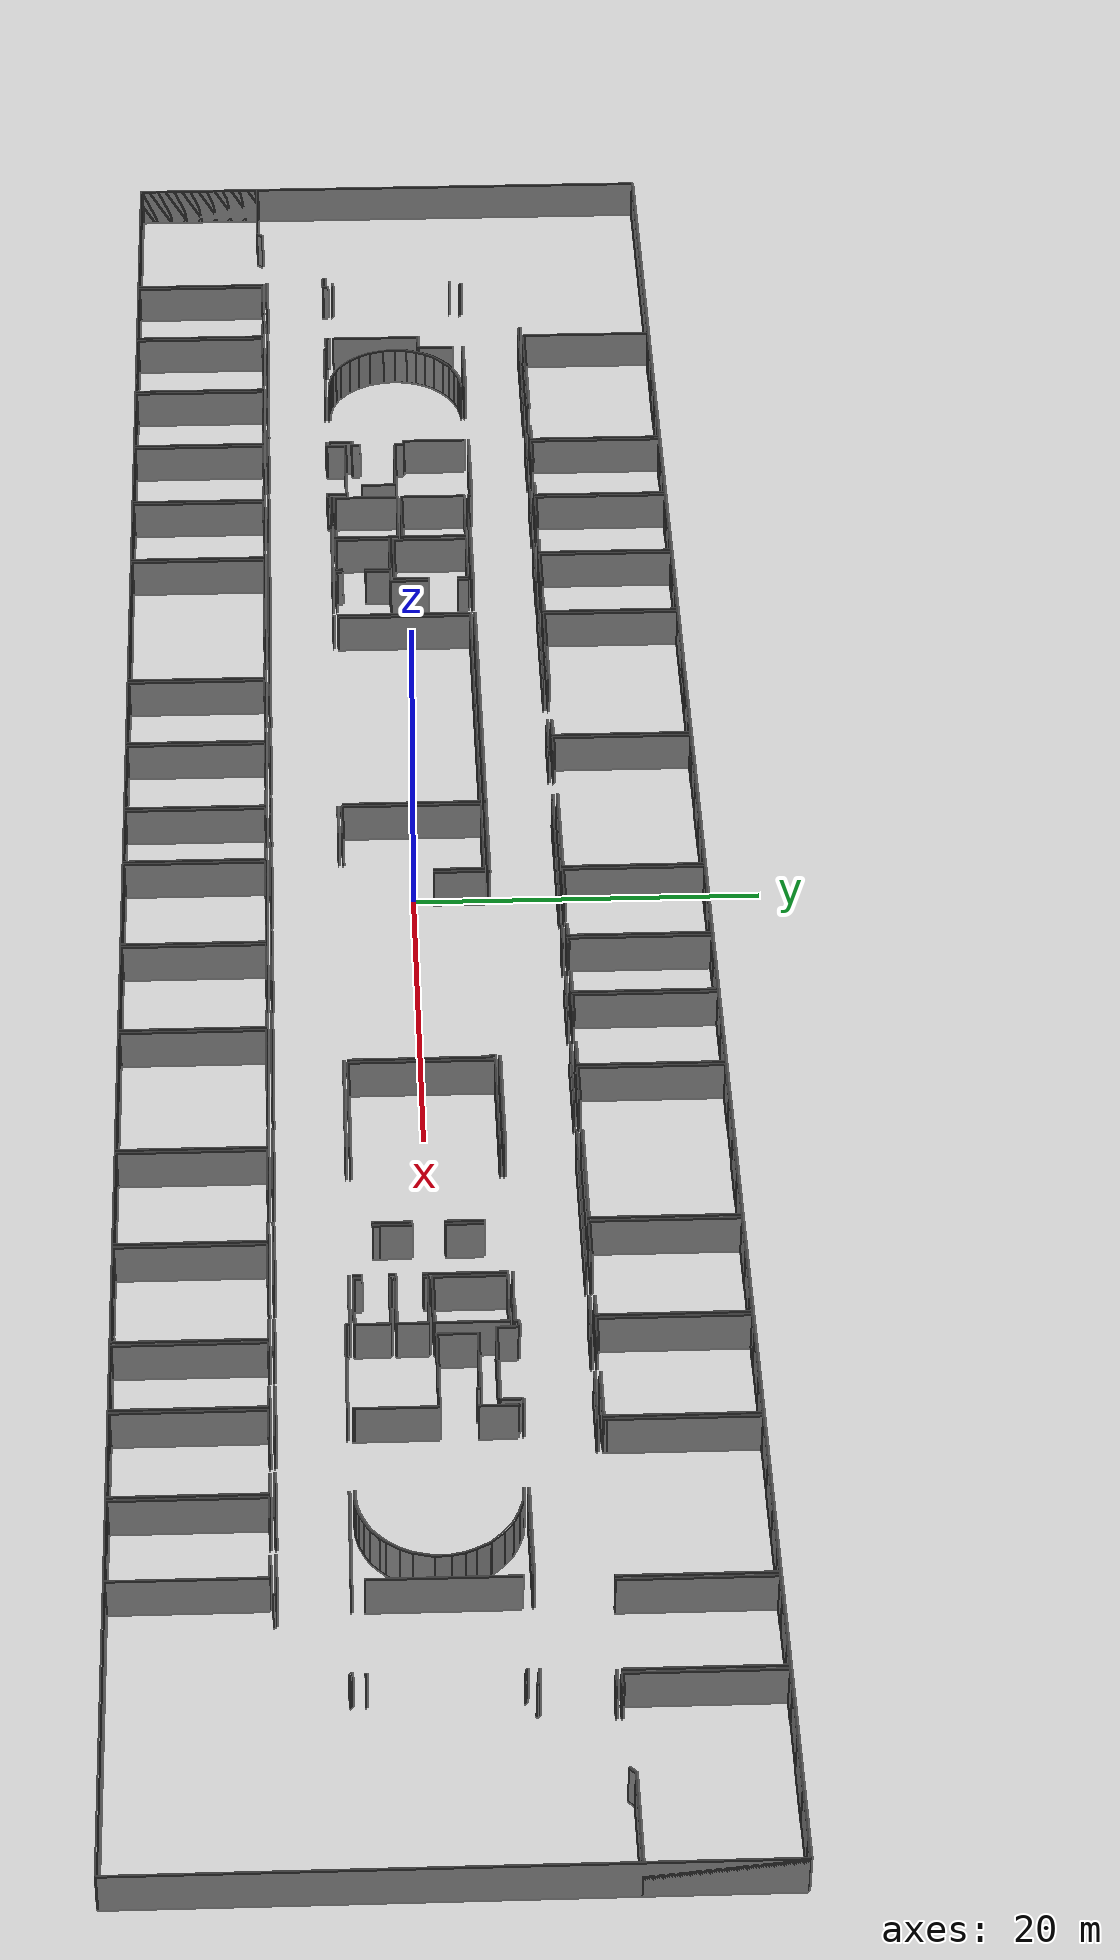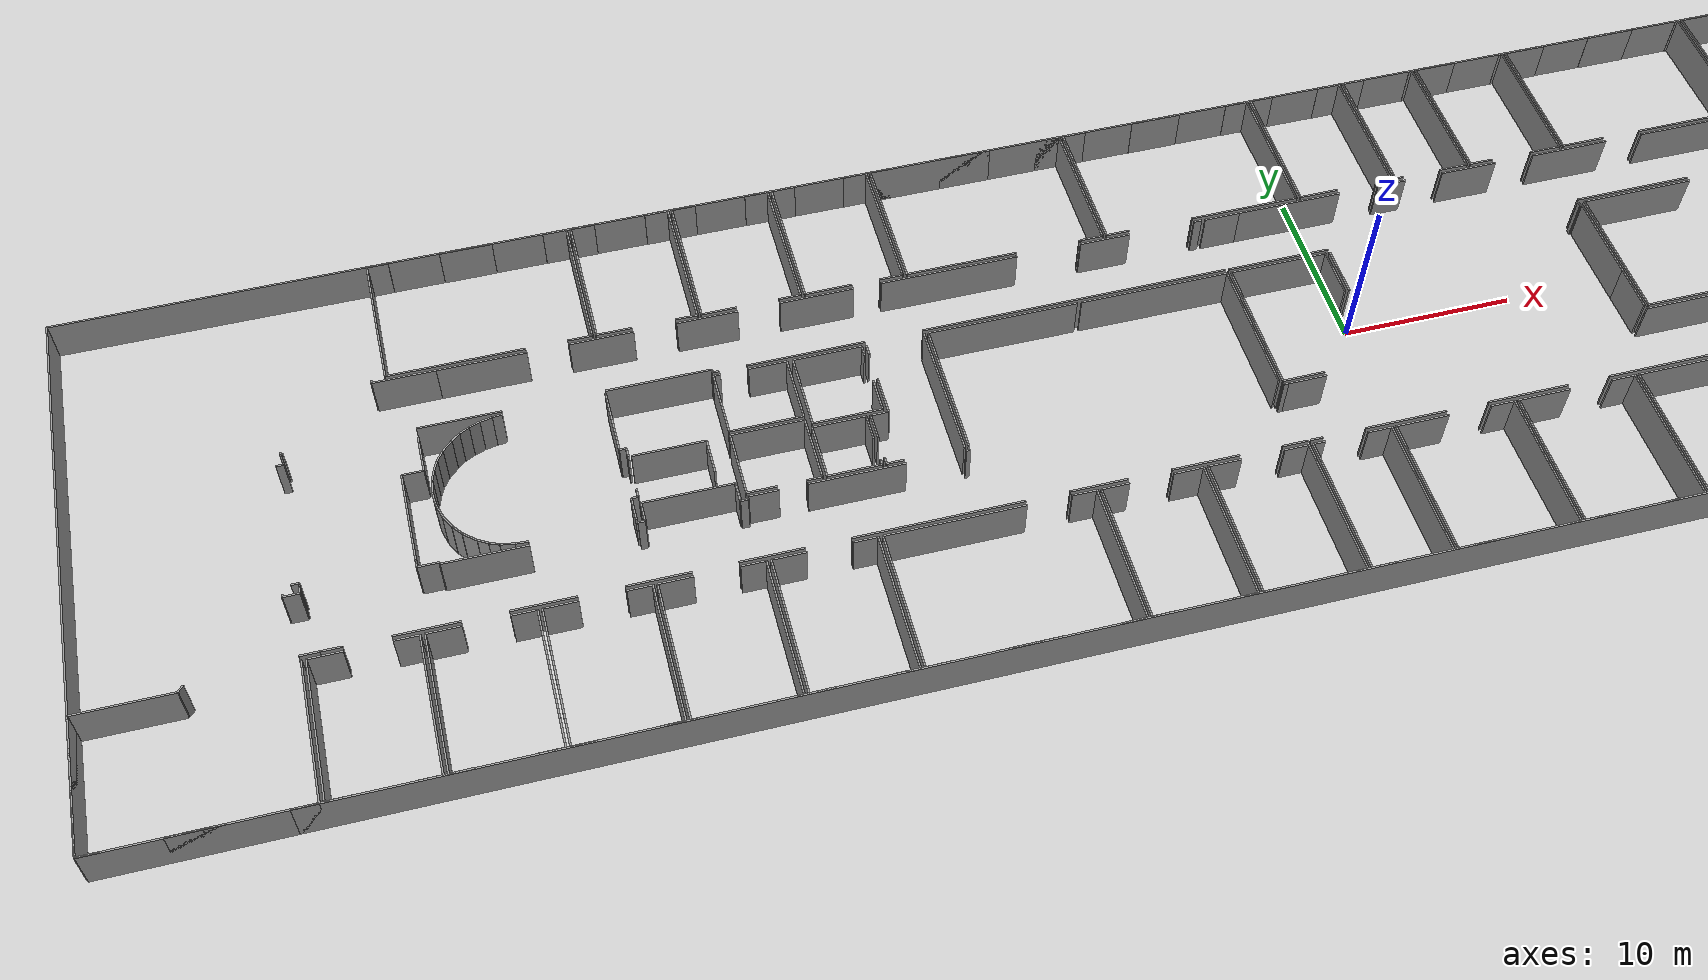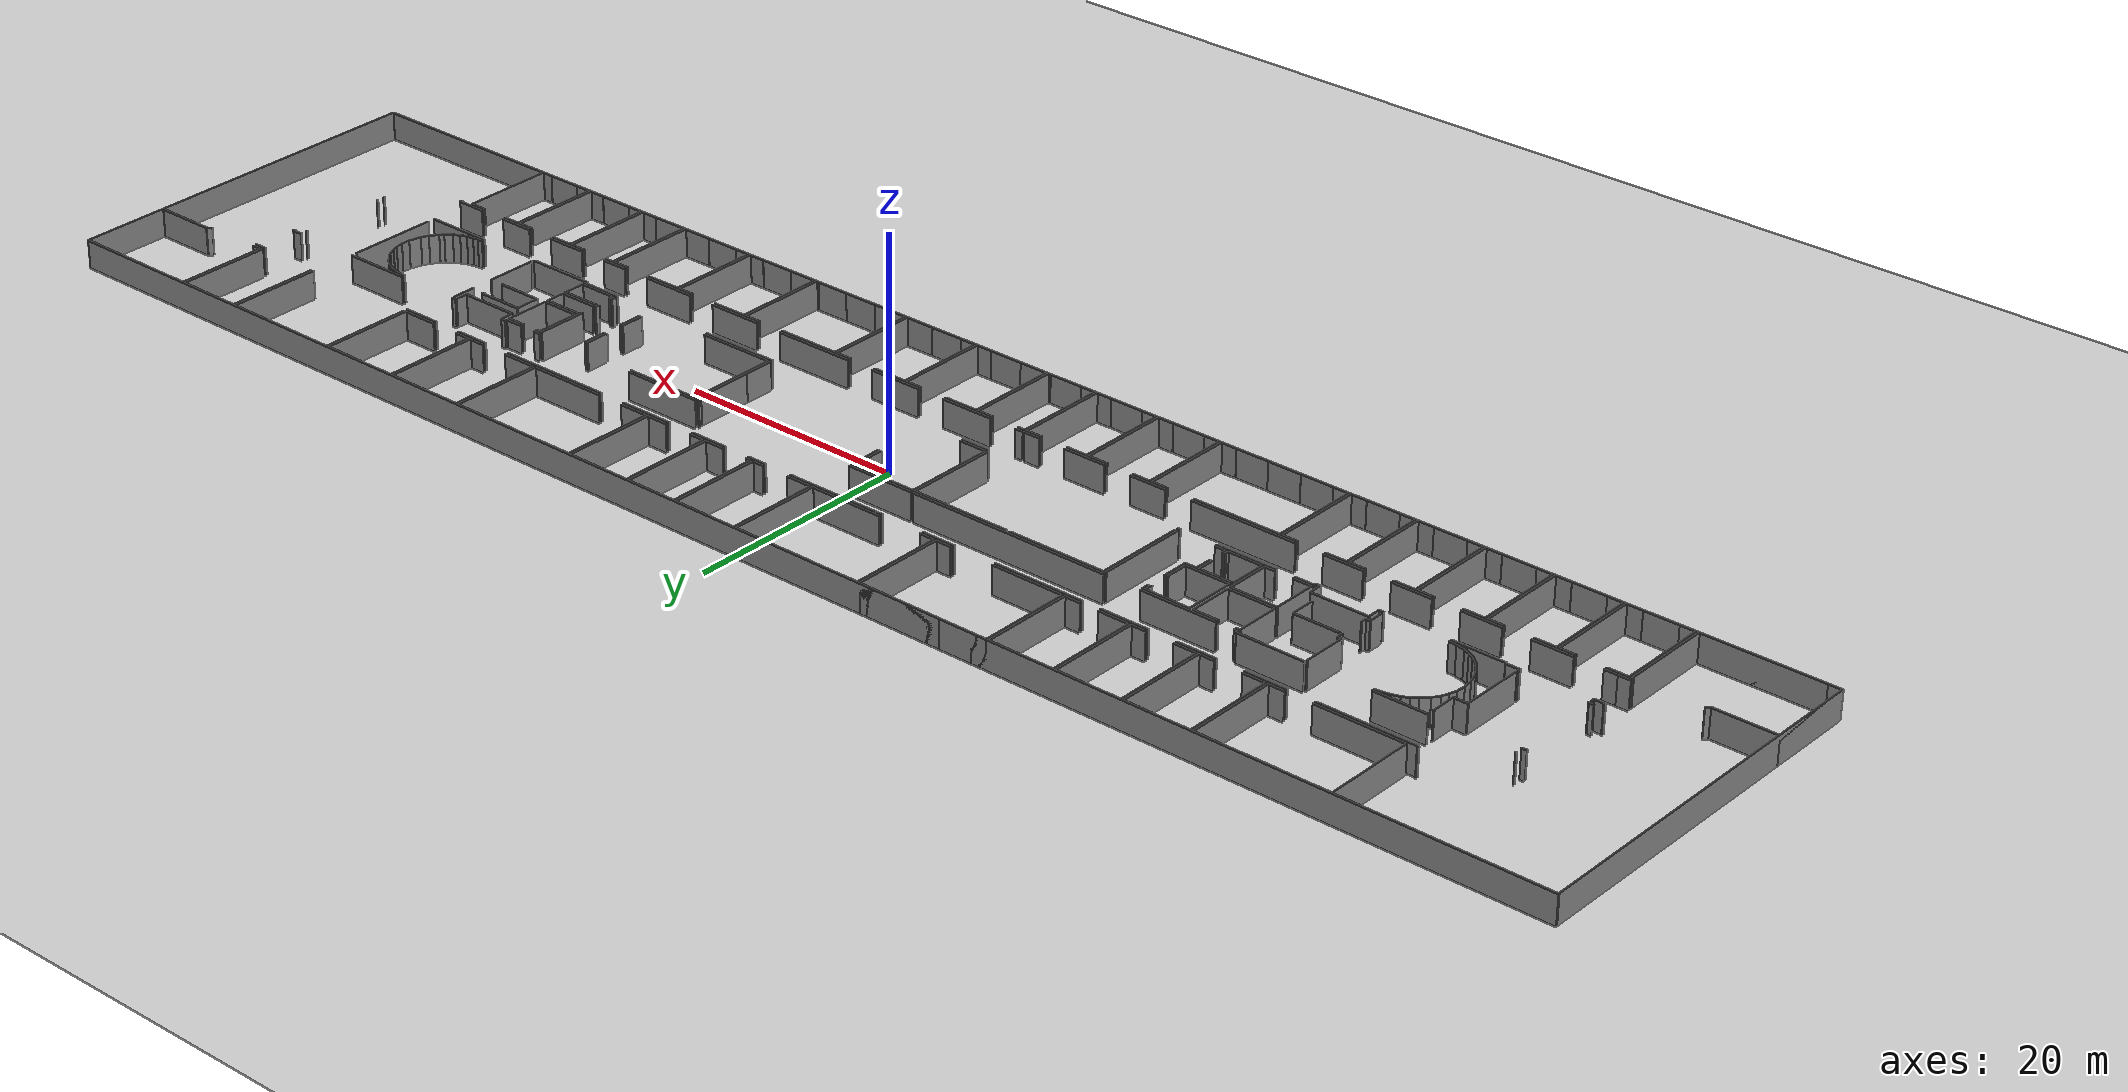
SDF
<sdf version="1.6">
  <world name="default">
    <light name="sun" type="directional">
      <cast_shadows>1</cast_shadows>
      <pose frame="">0 0 10 0 -0 0</pose>
      <diffuse>0.8 0.8 0.8 1</diffuse>
      <specular>0.1 0.1 0.1 1</specular>
      <attenuation>
        <range>1000</range>
        <constant>0.9</constant>
        <linear>0.01</linear>
        <quadratic>0.001</quadratic>
      </attenuation>
      <direction>-0.5 0.5 -1</direction>
    </light>
    <model name="ground_plane">
      <static>1</static>
      <link name="link">
        <collision name="collision">
          <geometry>
            <plane>
              <normal>0 0 1</normal>
              <size>100 100</size>
            </plane>
          </geometry>
          <surface>
            <friction>
              <ode>
                <mu>100</mu>
                <mu2>50</mu2>
              </ode>
              <torsional>
                <ode />
              </torsional>
            </friction>
            <contact>
              <ode />
            </contact>
            <bounce />
          </surface>
          <max_contacts>10</max_contacts>
        </collision>
        <visual name="visual">
          <cast_shadows>0</cast_shadows>
          <geometry>
            <plane>
              <normal>0 0 1</normal>
              <size>100 100</size>
            </plane>
          </geometry>
          <material>
            <script>
              <uri>file://media/materials/scripts/gazebo.material</uri>
              <name>Gazebo/Grey</name>
            </script>
          </material>
        </visual>
        <self_collide>0</self_collide>
        <kinematic>0</kinematic>
        <gravity>1</gravity>
      </link>
    </model>
    <gravity>0 0 -9.8</gravity>
    <magnetic_field>6e-06 2.3e-05 -4.2e-05</magnetic_field>
    <atmosphere type="adiabatic" />
    <physics default="0" name="default_physics" type="ode">
      <max_step_size>0.001</max_step_size>
      <real_time_factor>1</real_time_factor>
      <real_time_update_rate>1000</real_time_update_rate>
    </physics>
    <scene>
      <ambient>0.4 0.4 0.4 1</ambient>
      <background>0.7 0.7 0.7 1</background>
      <shadows>1</shadows>
    </scene>
    <spherical_coordinates>
      <surface_model>EARTH_WGS84</surface_model>
      <latitude_deg>0</latitude_deg>
      <longitude_deg>0</longitude_deg>
      <elevation>0</elevation>
      <heading_deg>0</heading_deg>
    </spherical_coordinates>
  <model name="50041185">
		<static>1</static>
		<link name="Wall_0">
			<collision name="Wall_0_Collision">
				<geometry>
					<box>
						<size>7.89638912543 0.1 2.5</size>
					</box>
				</geometry>
				<pose frame="">3.94819456272 0 1.25 0 0 0</pose>
			</collision>
			<visual name="Wall_0_Visual">
				<pose frame="">3.94819456272 0 1.25 0 0 0</pose>
				<geometry>
					<box>
						<size>7.89638912543 0.1 2.5</size>
					</box>
				</geometry>
				<material>
					<script>
						<uri>file://media/materials/scripts/gazebo.material</uri>
						<name>Gazebo/Grey</name>
					</script>
					<ambient>1 1 1 1</ambient>
				</material>
			</visual>
			<pose frame="">0.0 -33.5813876638 0 0 0 1.57079632679</pose>
		</link>
		<link name="Wall_1">
			<collision name="Wall_1_Collision">
				<geometry>
					<box>
						<size>5.39817486242 0.1 2.5</size>
					</box>
				</geometry>
				<pose frame="">2.69908743121 0 1.25 0 0 0</pose>
			</collision>
			<visual name="Wall_1_Visual">
				<pose frame="">2.69908743121 0 1.25 0 0 0</pose>
				<geometry>
					<box>
						<size>5.39817486242 0.1 2.5</size>
					</box>
				</geometry>
				<material>
					<script>
						<uri>file://media/materials/scripts/gazebo.material</uri>
						<name>Gazebo/Grey</name>
					</script>
					<ambient>1 1 1 1</ambient>
				</material>
			</visual>
			<pose frame="">0.0 -25.6849985384 0 0 0 0.0</pose>
		</link>
		<link name="Wall_2">
			<collision name="Wall_2_Collision">
				<geometry>
					<box>
						<size>0.445846377394 0.1 2.5</size>
					</box>
				</geometry>
				<pose frame="">0.222923188697 0 1.25 0 0 0</pose>
			</collision>
			<visual name="Wall_2_Visual">
				<pose frame="">0.222923188697 0 1.25 0 0 0</pose>
				<geometry>
					<box>
						<size>0.445846377394 0.1 2.5</size>
					</box>
				</geometry>
				<material>
					<script>
						<uri>file://media/materials/scripts/gazebo.material</uri>
						<name>Gazebo/Grey</name>
					</script>
					<ambient>1 1 1 1</ambient>
				</material>
			</visual>
			<pose frame="">5.39817486242 -25.6849985384 0 0 0 0.848533692958</pose>
		</link>
		<link name="Wall_3">
			<collision name="Wall_3_Collision">
				<geometry>
					<box>
						<size>0.0874439176909 0.1 2.5</size>
					</box>
				</geometry>
				<pose frame="">0.0437219588454 0 1.25 0 0 0</pose>
			</collision>
			<visual name="Wall_3_Visual">
				<pose frame="">0.0437219588454 0 1.25 0 0 0</pose>
				<geometry>
					<box>
						<size>0.0874439176909 0.1 2.5</size>
					</box>
				</geometry>
				<material>
					<script>
						<uri>file://media/materials/scripts/gazebo.material</uri>
						<name>Gazebo/Grey</name>
					</script>
					<ambient>1 1 1 1</ambient>
				</material>
			</visual>
			<pose frame="">11.4509970894 -25.3504747137 0 0 0 0.0</pose>
		</link>
		<link name="Wall_4">
			<collision name="Wall_4_Collision">
				<geometry>
					<box>
						<size>8.24171634108 0.1 2.5</size>
					</box>
				</geometry>
				<pose frame="">4.12085817054 0 1.25 0 0 0</pose>
			</collision>
			<visual name="Wall_4_Visual">
				<pose frame="">4.12085817054 0 1.25 0 0 0</pose>
				<geometry>
					<box>
						<size>8.24171634108 0.1 2.5</size>
					</box>
				</geometry>
				<material>
					<script>
						<uri>file://media/materials/scripts/gazebo.material</uri>
						<name>Gazebo/Grey</name>
					</script>
					<ambient>1 1 1 1</ambient>
				</material>
			</visual>
			<pose frame="">11.5384410071 -25.3504747137 0 0 0 -1.57079632679</pose>
		</link>
		<link name="Wall_5">
			<collision name="Wall_5_Collision">
				<geometry>
					<box>
						<size>1.38995157539 0.1 2.5</size>
					</box>
				</geometry>
				<pose frame="">0.694975787694 0 1.25 0 0 0</pose>
			</collision>
			<visual name="Wall_5_Visual">
				<pose frame="">0.694975787694 0 1.25 0 0 0</pose>
				<geometry>
					<box>
						<size>1.38995157539 0.1 2.5</size>
					</box>
				</geometry>
				<material>
					<script>
						<uri>file://media/materials/scripts/gazebo.material</uri>
						<name>Gazebo/Grey</name>
					</script>
					<ambient>1 1 1 1</ambient>
				</material>
			</visual>
			<pose frame="">11.5384410071 -33.5921910548 0 0 0 3.14159265359</pose>
		</link>
		<link name="Wall_6">
			<collision name="Wall_6_Collision">
				<geometry>
					<box>
						<size>3.01897583853 0.1 2.5</size>
					</box>
				</geometry>
				<pose frame="">1.50948791927 0 1.25 0 0 0</pose>
			</collision>
			<visual name="Wall_6_Visual">
				<pose frame="">1.50948791927 0 1.25 0 0 0</pose>
				<geometry>
					<box>
						<size>3.01897583853 0.1 2.5</size>
					</box>
				</geometry>
				<material>
					<script>
						<uri>file://media/materials/scripts/gazebo.material</uri>
						<name>Gazebo/Grey</name>
					</script>
					<ambient>1 1 1 1</ambient>
				</material>
			</visual>
			<pose frame="">7.1771756123 -33.5921910548 0 0 0 3.14159265359</pose>
		</link>
		<link name="Wall_7">
			<collision name="Wall_7_Collision">
				<geometry>
					<box>
						<size>1.15734779669 0.1 2.5</size>
					</box>
				</geometry>
				<pose frame="">0.578673898346 0 1.25 0 0 0</pose>
			</collision>
			<visual name="Wall_7_Visual">
				<pose frame="">0.578673898346 0 1.25 0 0 0</pose>
				<geometry>
					<box>
						<size>1.15734779669 0.1 2.5</size>
					</box>
				</geometry>
				<material>
					<script>
						<uri>file://media/materials/scripts/gazebo.material</uri>
						<name>Gazebo/Grey</name>
					</script>
					<ambient>1 1 1 1</ambient>
				</material>
			</visual>
			<pose frame="">1.15729737287 -33.5921910548 0 0 0 3.13225790744</pose>
		</link>
		<link name="Wall_8">
			<collision name="Wall_8_Collision">
				<geometry>
					<box>
						<size>8.22290573088 0.1 2.5</size>
					</box>
				</geometry>
				<pose frame="">4.11145286544 0 1.25 0 0 0</pose>
			</collision>
			<visual name="Wall_8_Visual">
				<pose frame="">4.11145286544 0 1.25 0 0 0</pose>
				<geometry>
					<box>
						<size>8.22290573088 0.1 2.5</size>
					</box>
				</geometry>
				<material>
					<script>
						<uri>file://media/materials/scripts/gazebo.material</uri>
						<name>Gazebo/Grey</name>
					</script>
					<ambient>1 1 1 1</ambient>
				</material>
			</visual>
			<pose frame="">11.7827247423 -33.578591492 0 0 0 1.57079632679</pose>
		</link>
		<link name="Wall_9">
			<collision name="Wall_9_Collision">
				<geometry>
					<box>
						<size>1.87279960345 0.1 2.5</size>
					</box>
				</geometry>
				<pose frame="">0.936399801726 0 1.25 0 0 0</pose>
			</collision>
			<visual name="Wall_9_Visual">
				<pose frame="">0.936399801726 0 1.25 0 0 0</pose>
				<geometry>
					<box>
						<size>1.87279960345 0.1 2.5</size>
					</box>
				</geometry>
				<material>
					<script>
						<uri>file://media/materials/scripts/gazebo.material</uri>
						<name>Gazebo/Grey</name>
					</script>
					<ambient>1 1 1 1</ambient>
				</material>
			</visual>
			<pose frame="">11.7827247423 -25.3556857611 0 0 0 0.0</pose>
		</link>
		<link name="Wall_10">
			<collision name="Wall_10_Collision">
				<geometry>
					<box>
						<size>1.36859899084 0.1 2.5</size>
					</box>
				</geometry>
				<pose frame="">0.684299495418 0 1.25 0 0 0</pose>
			</collision>
			<visual name="Wall_10_Visual">
				<pose frame="">0.684299495418 0 1.25 0 0 0</pose>
				<geometry>
					<box>
						<size>1.36859899084 0.1 2.5</size>
					</box>
				</geometry>
				<material>
					<script>
						<uri>file://media/materials/scripts/gazebo.material</uri>
						<name>Gazebo/Grey</name>
					</script>
					<ambient>1 1 1 1</ambient>
				</material>
			</visual>
			<pose frame="">16.1635633396 -25.3556857611 0 0 0 0.0</pose>
		</link>
		<link name="Wall_11">
			<collision name="Wall_11_Collision">
				<geometry>
					<box>
						<size>8.22900646932 0.1 2.5</size>
					</box>
				</geometry>
				<pose frame="">4.11450323466 0 1.25 0 0 0</pose>
			</collision>
			<visual name="Wall_11_Visual">
				<pose frame="">4.11450323466 0 1.25 0 0 0</pose>
				<geometry>
					<box>
						<size>8.22900646932 0.1 2.5</size>
					</box>
				</geometry>
				<material>
					<script>
						<uri>file://media/materials/scripts/gazebo.material</uri>
						<name>Gazebo/Grey</name>
					</script>
					<ambient>1 1 1 1</ambient>
				</material>
			</visual>
			<pose frame="">17.5321623305 -25.3556857611 0 0 0 -1.57079632679</pose>
		</link>
		<link name="Wall_12">
			<collision name="Wall_12_Collision">
				<geometry>
					<box>
						<size>1.36859899084 0.1 2.5</size>
					</box>
				</geometry>
				<pose frame="">0.684299495418 0 1.25 0 0 0</pose>
			</collision>
			<visual name="Wall_12_Visual">
				<pose frame="">0.684299495418 0 1.25 0 0 0</pose>
				<geometry>
					<box>
						<size>1.36859899084 0.1 2.5</size>
					</box>
				</geometry>
				<material>
					<script>
						<uri>file://media/materials/scripts/gazebo.material</uri>
						<name>Gazebo/Grey</name>
					</script>
					<ambient>1 1 1 1</ambient>
				</material>
			</visual>
			<pose frame="">17.5321623305 -33.5846922305 0 0 0 3.14159265359</pose>
		</link>
		<link name="Wall_13">
			<collision name="Wall_13_Collision">
				<geometry>
					<box>
						<size>1.35043765464 0.1 2.5</size>
					</box>
				</geometry>
				<pose frame="">0.675218827322 0 1.25 0 0 0</pose>
			</collision>
			<visual name="Wall_13_Visual">
				<pose frame="">0.675218827322 0 1.25 0 0 0</pose>
				<geometry>
					<box>
						<size>1.35043765464 0.1 2.5</size>
					</box>
				</geometry>
				<material>
					<script>
						<uri>file://media/materials/scripts/gazebo.material</uri>
						<name>Gazebo/Grey</name>
					</script>
					<ambient>1 1 1 1</ambient>
				</material>
			</visual>
			<pose frame="">13.1331486165 -33.5846922305 0 0 0 3.13707503726</pose>
		</link>
		<link name="Wall_14">
			<collision name="Wall_14_Collision">
				<geometry>
					<box>
						<size>8.23116714752 0.1 2.5</size>
					</box>
				</geometry>
				<pose frame="">4.11558357376 0 1.25 0 0 0</pose>
			</collision>
			<visual name="Wall_14_Visual">
				<pose frame="">4.11558357376 0 1.25 0 0 0</pose>
				<geometry>
					<box>
						<size>8.23116714752 0.1 2.5</size>
					</box>
				</geometry>
				<material>
					<script>
						<uri>file://media/materials/scripts/gazebo.material</uri>
						<name>Gazebo/Grey</name>
					</script>
					<ambient>1 1 1 1</ambient>
				</material>
			</visual>
			<pose frame="">17.7816571131 -33.5846922305 0 0 0 1.57079632679</pose>
		</link>
		<link name="Wall_15">
			<collision name="Wall_15_Collision">
				<geometry>
					<box>
						<size>1.89732965594 0.1 2.5</size>
					</box>
				</geometry>
				<pose frame="">0.948664827972 0 1.25 0 0 0</pose>
			</collision>
			<visual name="Wall_15_Visual">
				<pose frame="">0.948664827972 0 1.25 0 0 0</pose>
				<geometry>
					<box>
						<size>1.89732965594 0.1 2.5</size>
					</box>
				</geometry>
				<material>
					<script>
						<uri>file://media/materials/scripts/gazebo.material</uri>
						<name>Gazebo/Grey</name>
					</script>
					<ambient>1 1 1 1</ambient>
				</material>
			</visual>
			<pose frame="">17.7816571131 -25.3535250829 0 0 0 0.0</pose>
		</link>
		<link name="Wall_16">
			<collision name="Wall_16_Collision">
				<geometry>
					<box>
						<size>1.39058706898 0.1 2.5</size>
					</box>
				</geometry>
				<pose frame="">0.695293534488 0 1.25 0 0 0</pose>
			</collision>
			<visual name="Wall_16_Visual">
				<pose frame="">0.695293534488 0 1.25 0 0 0</pose>
				<geometry>
					<box>
						<size>1.39058706898 0.1 2.5</size>
					</box>
				</geometry>
				<material>
					<script>
						<uri>file://media/materials/scripts/gazebo.material</uri>
						<name>Gazebo/Grey</name>
					</script>
					<ambient>1 1 1 1</ambient>
				</material>
			</visual>
			<pose frame="">22.1651647835 -25.3535250829 0 0 0 0.0</pose>
		</link>
		<link name="Wall_17">
			<collision name="Wall_17_Collision">
				<geometry>
					<box>
						<size>8.22163474371 0.1 2.5</size>
					</box>
				</geometry>
				<pose frame="">4.11081737185 0 1.25 0 0 0</pose>
			</collision>
			<visual name="Wall_17_Visual">
				<pose frame="">4.11081737185 0 1.25 0 0 0</pose>
				<geometry>
					<box>
						<size>8.22163474371 0.1 2.5</size>
					</box>
				</geometry>
				<material>
					<script>
						<uri>file://media/materials/scripts/gazebo.material</uri>
						<name>Gazebo/Grey</name>
					</script>
					<ambient>1 1 1 1</ambient>
				</material>
			</visual>
			<pose frame="">23.5557518525 -25.3535250829 0 0 0 -1.57079632679</pose>
		</link>
		<link name="Wall_18">
			<collision name="Wall_18_Collision">
				<geometry>
					<box>
						<size>1.38753669975 0.1 2.5</size>
					</box>
				</geometry>
				<pose frame="">0.693768349877 0 1.25 0 0 0</pose>
			</collision>
			<visual name="Wall_18_Visual">
				<pose frame="">0.693768349877 0 1.25 0 0 0</pose>
				<geometry>
					<box>
						<size>1.38753669975 0.1 2.5</size>
					</box>
				</geometry>
				<material>
					<script>
						<uri>file://media/materials/scripts/gazebo.material</uri>
						<name>Gazebo/Grey</name>
					</script>
					<ambient>1 1 1 1</ambient>
				</material>
			</visual>
			<pose frame="">23.5557518525 -33.5751598266 0 0 0 3.14159265359</pose>
		</link>
		<link name="Wall_19">
			<collision name="Wall_19_Collision">
				<geometry>
					<box>
						<size>1.38210432789 0.1 2.5</size>
					</box>
				</geometry>
				<pose frame="">0.691052163944 0 1.25 0 0 0</pose>
			</collision>
			<visual name="Wall_19_Visual">
				<pose frame="">0.691052163944 0 1.25 0 0 0</pose>
				<geometry>
					<box>
						<size>1.38210432789 0.1 2.5</size>
					</box>
				</geometry>
				<material>
					<script>
						<uri>file://media/materials/scripts/gazebo.material</uri>
						<name>Gazebo/Grey</name>
					</script>
					<ambient>1 1 1 1</ambient>
				</material>
			</visual>
			<pose frame="">19.163728568 -33.5751598266 0 0 0 -3.13469557701</pose>
		</link>
		<link name="Wall_20">
			<collision name="Wall_20_Collision">
				<geometry>
					<box>
						<size>8.23383622059 0.1 2.5</size>
					</box>
				</geometry>
				<pose frame="">4.1169181103 0 1.25 0 0 0</pose>
			</collision>
			<visual name="Wall_20_Visual">
				<pose frame="">4.1169181103 0 1.25 0 0 0</pose>
				<geometry>
					<box>
						<size>8.23383622059 0.1 2.5</size>
					</box>
				</geometry>
				<material>
					<script>
						<uri>file://media/materials/scripts/gazebo.material</uri>
						<name>Gazebo/Grey</name>
					</script>
					<ambient>1 1 1 1</ambient>
				</material>
			</visual>
			<pose frame="">23.7919012697 -33.5831670458 0 0 0 1.57079632679</pose>
		</link>
		<link name="Wall_21">
			<collision name="Wall_21_Collision">
				<geometry>
					<box>
						<size>1.89288120083 0.1 2.5</size>
					</box>
				</geometry>
				<pose frame="">0.946440600414 0 1.25 0 0 0</pose>
			</collision>
			<visual name="Wall_21_Visual">
				<pose frame="">0.946440600414 0 1.25 0 0 0</pose>
				<geometry>
					<box>
						<size>1.89288120083 0.1 2.5</size>
					</box>
				</geometry>
				<material>
					<script>
						<uri>file://media/materials/scripts/gazebo.material</uri>
						<name>Gazebo/Grey</name>
					</script>
					<ambient>1 1 1 1</ambient>
				</material>
			</visual>
			<pose frame="">23.7919012697 -25.3493308253 0 0 0 0.0</pose>
		</link>
		<link name="Wall_22">
			<collision name="Wall_22_Collision">
				<geometry>
					<box>
						<size>1.37571651902 0.1 2.5</size>
					</box>
				</geometry>
				<pose frame="">0.68785825951 0 1.25 0 0 0</pose>
			</collision>
			<visual name="Wall_22_Visual">
				<pose frame="">0.68785825951 0 1.25 0 0 0</pose>
				<geometry>
					<box>
						<size>1.37571651902 0.1 2.5</size>
					</box>
				</geometry>
				<material>
					<script>
						<uri>file://media/materials/scripts/gazebo.material</uri>
						<name>Gazebo/Grey</name>
					</script>
					<ambient>1 1 1 1</ambient>
				</material>
			</visual>
			<pose frame="">28.1788406055 -25.3493308253 0 0 0 0.0</pose>
		</link>
		<link name="Wall_23">
			<collision name="Wall_23_Collision">
				<geometry>
					<box>
						<size>8.23040455522 0.1 2.5</size>
					</box>
				</geometry>
				<pose frame="">4.11520227761 0 1.25 0 0 0</pose>
			</collision>
			<visual name="Wall_23_Visual">
				<pose frame="">4.11520227761 0 1.25 0 0 0</pose>
				<geometry>
					<box>
						<size>8.23040455522 0.1 2.5</size>
					</box>
				</geometry>
				<material>
					<script>
						<uri>file://media/materials/scripts/gazebo.material</uri>
						<name>Gazebo/Grey</name>
					</script>
					<ambient>1 1 1 1</ambient>
				</material>
			</visual>
			<pose frame="">29.5545571245 -25.3493308253 0 0 0 -1.57079632679</pose>
		</link>
		<link name="Wall_24">
			<collision name="Wall_24_Collision">
				<geometry>
					<box>
						<size>1.38702830488 0.1 2.5</size>
					</box>
				</geometry>
				<pose frame="">0.693514152442 0 1.25 0 0 0</pose>
			</collision>
			<visual name="Wall_24_Visual">
				<pose frame="">0.693514152442 0 1.25 0 0 0</pose>
				<geometry>
					<box>
						<size>1.38702830488 0.1 2.5</size>
					</box>
				</geometry>
				<material>
					<script>
						<uri>file://media/materials/scripts/gazebo.material</uri>
						<name>Gazebo/Grey</name>
					</script>
					<ambient>1 1 1 1</ambient>
				</material>
			</visual>
			<pose frame="">29.5545571245 -33.5797353805 0 0 0 3.14159265359</pose>
		</link>
		<link name="Wall_25">
			<collision name="Wall_25_Collision">
				<geometry>
					<box>
						<size>1.39758171156 0.1 2.5</size>
					</box>
				</geometry>
				<pose frame="">0.698790855779 0 1.25 0 0 0</pose>
			</collision>
			<visual name="Wall_25_Visual">
				<pose frame="">0.698790855779 0 1.25 0 0 0</pose>
				<geometry>
					<box>
						<size>1.39758171156 0.1 2.5</size>
					</box>
				</geometry>
				<material>
					<script>
						<uri>file://media/materials/scripts/gazebo.material</uri>
						<name>Gazebo/Grey</name>
					</script>
					<ambient>1 1 1 1</ambient>
				</material>
			</visual>
			<pose frame="">25.1894787682 -33.5797353805 0 0 0 -3.13913722018</pose>
		</link>
		<link name="Wall_26">
			<collision name="Wall_26_Collision">
				<geometry>
					<box>
						<size>8.23307362829 0.1 2.5</size>
					</box>
				</geometry>
				<pose frame="">4.11653681414 0 1.25 0 0 0</pose>
			</collision>
			<visual name="Wall_26_Visual">
				<pose frame="">4.11653681414 0 1.25 0 0 0</pose>
				<geometry>
					<box>
						<size>8.23307362829 0.1 2.5</size>
					</box>
				</geometry>
				<material>
					<script>
						<uri>file://media/materials/scripts/gazebo.material</uri>
						<name>Gazebo/Grey</name>
					</script>
					<ambient>1 1 1 1</ambient>
				</material>
			</visual>
			<pose frame="">29.7912149366 -33.5806250715 0 0 0 1.57079632679</pose>
		</link>
		<link name="Wall_27">
			<collision name="Wall_27_Collision">
				<geometry>
					<box>
						<size>1.90050712388 0.1 2.5</size>
					</box>
				</geometry>
				<pose frame="">0.950253561942 0 1.25 0 0 0</pose>
			</collision>
			<visual name="Wall_27_Visual">
				<pose frame="">0.950253561942 0 1.25 0 0 0</pose>
				<geometry>
					<box>
						<size>1.90050712388 0.1 2.5</size>
					</box>
				</geometry>
				<material>
					<script>
						<uri>file://media/materials/scripts/gazebo.material</uri>
						<name>Gazebo/Grey</name>
					</script>
					<ambient>1 1 1 1</ambient>
				</material>
			</visual>
			<pose frame="">29.7912149366 -25.3475514432 0 0 0 0.0</pose>
		</link>
		<link name="Wall_28">
			<collision name="Wall_28_Collision">
				<geometry>
					<box>
						<size>1.38664700873 0.1 2.5</size>
					</box>
				</geometry>
				<pose frame="">0.693323504366 0 1.25 0 0 0</pose>
			</collision>
			<visual name="Wall_28_Visual">
				<pose frame="">0.693323504366 0 1.25 0 0 0</pose>
				<geometry>
					<box>
						<size>1.38664700873 0.1 2.5</size>
					</box>
				</geometry>
				<material>
					<script>
						<uri>file://media/materials/scripts/gazebo.material</uri>
						<name>Gazebo/Grey</name>
					</script>
					<ambient>1 1 1 1</ambient>
				</material>
			</visual>
			<pose frame="">34.1704012507 -25.3475514432 0 0 0 0.0</pose>
		</link>
		<link name="Wall_29">
			<collision name="Wall_29_Collision">
				<geometry>
					<box>
						<size>8.24082665006 0.1 2.5</size>
					</box>
				</geometry>
				<pose frame="">4.12041332503 0 1.25 0 0 0</pose>
			</collision>
			<visual name="Wall_29_Visual">
				<pose frame="">4.12041332503 0 1.25 0 0 0</pose>
				<geometry>
					<box>
						<size>8.24082665006 0.1 2.5</size>
					</box>
				</geometry>
				<material>
					<script>
						<uri>file://media/materials/scripts/gazebo.material</uri>
						<name>Gazebo/Grey</name>
					</script>
					<ambient>1 1 1 1</ambient>
				</material>
			</visual>
			<pose frame="">35.5570482594 -25.3475514432 0 0 0 -1.57079632679</pose>
		</link>
		<link name="Wall_30">
			<collision name="Wall_30_Collision">
				<geometry>
					<box>
						<size>1.3957981164 0.1 2.5</size>
					</box>
				</geometry>
				<pose frame="">0.697899058199 0 1.25 0 0 0</pose>
			</collision>
			<visual name="Wall_30_Visual">
				<pose frame="">0.697899058199 0 1.25 0 0 0</pose>
				<geometry>
					<box>
						<size>1.3957981164 0.1 2.5</size>
					</box>
				</geometry>
				<material>
					<script>
						<uri>file://media/materials/scripts/gazebo.material</uri>
						<name>Gazebo/Grey</name>
					</script>
					<ambient>1 1 1 1</ambient>
				</material>
			</visual>
			<pose frame="">35.5570482594 -33.5883780933 0 0 0 3.14159265359</pose>
		</link>
		<link name="Wall_31">
			<collision name="Wall_31_Collision">
				<geometry>
					<box>
						<size>1.40268287387 0.1 2.5</size>
					</box>
				</geometry>
				<pose frame="">0.701341436936 0 1.25 0 0 0</pose>
			</collision>
			<visual name="Wall_31_Visual">
				<pose frame="">0.701341436936 0 1.25 0 0 0</pose>
				<geometry>
					<box>
						<size>1.40268287387 0.1 2.5</size>
					</box>
				</geometry>
				<material>
					<script>
						<uri>file://media/materials/scripts/gazebo.material</uri>
						<name>Gazebo/Grey</name>
					</script>
					<ambient>1 1 1 1</ambient>
				</material>
			</visual>
			<pose frame="">31.1938763838 -33.5883780933 0 0 0 3.13606534489</pose>
		</link>
		<link name="Wall_32">
			<collision name="Wall_32_Collision">
				<geometry>
					<box>
						<size>8.23980986032 0.1 2.5</size>
					</box>
				</geometry>
				<pose frame="">4.11990493016 0 1.25 0 0 0</pose>
			</collision>
			<visual name="Wall_32_Visual">
				<pose frame="">4.11990493016 0 1.25 0 0 0</pose>
				<geometry>
					<box>
						<size>8.23980986032 0.1 2.5</size>
					</box>
				</geometry>
				<material>
					<script>
						<uri>file://media/materials/scripts/gazebo.material</uri>
						<name>Gazebo/Grey</name>
					</script>
					<ambient>1 1 1 1</ambient>
				</material>
			</visual>
			<pose frame="">35.8050178574 -33.5869800074 0 0 0 1.57079632679</pose>
		</link>
		<link name="Wall_33">
			<collision name="Wall_33_Collision">
				<geometry>
					<box>
						<size>1.90775175078 0.1 2.5</size>
					</box>
				</geometry>
				<pose frame="">0.953875875392 0 1.25 0 0 0</pose>
			</collision>
			<visual name="Wall_33_Visual">
				<pose frame="">0.953875875392 0 1.25 0 0 0</pose>
				<geometry>
					<box>
						<size>1.90775175078 0.1 2.5</size>
					</box>
				</geometry>
				<material>
					<script>
						<uri>file://media/materials/scripts/gazebo.material</uri>
						<name>Gazebo/Grey</name>
					</script>
					<ambient>1 1 1 1</ambient>
				</material>
			</visual>
			<pose frame="">35.8050178574 -25.3471701471 0 0 0 0.0</pose>
		</link>
		<link name="Wall_34">
			<collision name="Wall_34_Collision">
				<geometry>
					<box>
						<size>1.36745510238 0.1 2.5</size>
					</box>
				</geometry>
				<pose frame="">0.683727551189 0 1.25 0 0 0</pose>
			</collision>
			<visual name="Wall_34_Visual">
				<pose frame="">0.683727551189 0 1.25 0 0 0</pose>
				<geometry>
					<box>
						<size>1.36745510238 0.1 2.5</size>
					</box>
				</geometry>
				<material>
					<script>
						<uri>file://media/materials/scripts/gazebo.material</uri>
						<name>Gazebo/Grey</name>
					</script>
					<ambient>1 1 1 1</ambient>
				</material>
			</visual>
			<pose frame="">40.1909404034 -25.3471701471 0 0 0 0.0</pose>
		</link>
		<link name="Wall_35">
			<collision name="Wall_35_Collision">
				<geometry>
					<box>
						<size>8.23002325907 0.1 2.5</size>
					</box>
				</geometry>
				<pose frame="">4.11501162953 0 1.25 0 0 0</pose>
			</collision>
			<visual name="Wall_35_Visual">
				<pose frame="">4.11501162953 0 1.25 0 0 0</pose>
				<geometry>
					<box>
						<size>8.23002325907 0.1 2.5</size>
					</box>
				</geometry>
				<material>
					<script>
						<uri>file://media/materials/scripts/gazebo.material</uri>
						<name>Gazebo/Grey</name>
					</script>
					<ambient>1 1 1 1</ambient>
				</material>
			</visual>
			<pose frame="">41.5583955058 -25.3471701471 0 0 0 -1.57079632679</pose>
		</link>
		<link name="Wall_36">
			<collision name="Wall_36_Collision">
				<geometry>
					<box>
						<size>1.38690120617 0.1 2.5</size>
					</box>
				</geometry>
				<pose frame="">0.693450603083 0 1.25 0 0 0</pose>
			</collision>
			<visual name="Wall_36_Visual">
				<pose frame="">0.693450603083 0 1.25 0 0 0</pose>
				<geometry>
					<box>
						<size>1.38690120617 0.1 2.5</size>
					</box>
				</geometry>
				<material>
					<script>
						<uri>file://media/materials/scripts/gazebo.material</uri>
						<name>Gazebo/Grey</name>
					</script>
					<ambient>1 1 1 1</ambient>
				</material>
			</visual>
			<pose frame="">41.5583955058 -33.5771934061 0 0 0 3.14159265359</pose>
		</link>
		<link name="Wall_37">
			<collision name="Wall_37_Collision">
				<geometry>
					<box>
						<size>1.37905581189 0.1 2.5</size>
					</box>
				</geometry>
				<pose frame="">0.689527905945 0 1.25 0 0 0</pose>
			</collision>
			<visual name="Wall_37_Visual">
				<pose frame="">0.689527905945 0 1.25 0 0 0</pose>
				<geometry>
					<box>
						<size>1.37905581189 0.1 2.5</size>
					</box>
				</geometry>
				<material>
					<script>
						<uri>file://media/materials/scripts/gazebo.material</uri>
						<name>Gazebo/Grey</name>
					</script>
					<ambient>1 1 1 1</ambient>
				</material>
			</visual>
			<pose frame="">37.184038943 -33.5771934061 0 0 0 -3.13449599853</pose>
		</link>
		<link name="Wall_38">
			<collision name="Wall_38_Collision">
				<geometry>
					<box>
						<size>8.23510720777 0.1 2.5</size>
					</box>
				</geometry>
				<pose frame="">4.11755360388 0 1.25 0 0 0</pose>
			</collision>
			<visual name="Wall_38_Visual">
				<pose frame="">4.11755360388 0 1.25 0 0 0</pose>
				<geometry>
					<box>
						<size>8.23510720777 0.1 2.5</size>
					</box>
				</geometry>
				<material>
					<script>
						<uri>file://media/materials/scripts/gazebo.material</uri>
						<name>Gazebo/Grey</name>
					</script>
					<ambient>1 1 1 1</ambient>
				</material>
			</visual>
			<pose frame="">41.8078902884 -33.582658651 0 0 0 1.57079632679</pose>
		</link>
		<link name="Wall_39">
			<collision name="Wall_39_Collision">
				<geometry>
					<box>
						<size>7.88698382033 0.1 2.5</size>
					</box>
				</geometry>
				<pose frame="">3.94349191017 0 1.25 0 0 0</pose>
			</collision>
			<visual name="Wall_39_Visual">
				<pose frame="">3.94349191017 0 1.25 0 0 0</pose>
				<geometry>
					<box>
						<size>7.88698382033 0.1 2.5</size>
					</box>
				</geometry>
				<material>
					<script>
						<uri>file://media/materials/scripts/gazebo.material</uri>
						<name>Gazebo/Grey</name>
					</script>
					<ambient>1 1 1 1</ambient>
				</material>
			</visual>
			<pose frame="">41.8078902884 -25.3475514432 0 0 0 0.0</pose>
		</link>
		<link name="Wall_40">
			<collision name="Wall_40_Collision">
				<geometry>
					<box>
						<size>1.39211225359 0.1 2.5</size>
					</box>
				</geometry>
				<pose frame="">0.696056126794 0 1.25 0 0 0</pose>
			</collision>
			<visual name="Wall_40_Visual">
				<pose frame="">0.696056126794 0 1.25 0 0 0</pose>
				<geometry>
					<box>
						<size>1.39211225359 0.1 2.5</size>
					</box>
				</geometry>
				<material>
					<script>
						<uri>file://media/materials/scripts/gazebo.material</uri>
						<name>Gazebo/Grey</name>
					</script>
					<ambient>1 1 1 1</ambient>
				</material>
			</visual>
			<pose frame="">52.1875341578 -25.3475514432 0 0 0 0.0</pose>
		</link>
		<link name="Wall_41">
			<collision name="Wall_41_Collision">
				<geometry>
					<box>
						<size>8.23053165394 0.1 2.5</size>
					</box>
				</geometry>
				<pose frame="">4.11526582697 0 1.25 0 0 0</pose>
			</collision>
			<visual name="Wall_41_Visual">
				<pose frame="">4.11526582697 0 1.25 0 0 0</pose>
				<geometry>
					<box>
						<size>8.23053165394 0.1 2.5</size>
					</box>
				</geometry>
				<material>
					<script>
						<uri>file://media/materials/scripts/gazebo.material</uri>
						<name>Gazebo/Grey</name>
					</script>
					<ambient>1 1 1 1</ambient>
				</material>
			</visual>
			<pose frame="">53.5796464114 -25.3475514432 0 0 0 -1.57079632679</pose>
		</link>
		<link name="Wall_42">
			<collision name="Wall_42_Collision">
				<geometry>
					<box>
						<size>1.38728250232 0.1 2.5</size>
					</box>
				</geometry>
				<pose frame="">0.69364125116 0 1.25 0 0 0</pose>
			</collision>
			<visual name="Wall_42_Visual">
				<pose frame="">0.69364125116 0 1.25 0 0 0</pose>
				<geometry>
					<box>
						<size>1.38728250232 0.1 2.5</size>
					</box>
				</geometry>
				<material>
					<script>
						<uri>file://media/materials/scripts/gazebo.material</uri>
						<name>Gazebo/Grey</name>
					</script>
					<ambient>1 1 1 1</ambient>
				</material>
			</visual>
			<pose frame="">53.5796464114 -33.5780830971 0 0 0 3.14159265359</pose>
		</link>
		<link name="Wall_43">
			<collision name="Wall_43_Collision">
				<geometry>
					<box>
						<size>3.01681516034 0.1 2.5</size>
					</box>
				</geometry>
				<pose frame="">1.50840758017 0 1.25 0 0 0</pose>
			</collision>
			<visual name="Wall_43_Visual">
				<pose frame="">1.50840758017 0 1.25 0 0 0</pose>
				<geometry>
					<box>
						<size>3.01681516034 0.1 2.5</size>
					</box>
				</geometry>
				<material>
					<script>
						<uri>file://media/materials/scripts/gazebo.material</uri>
						<name>Gazebo/Grey</name>
					</script>
					<ambient>1 1 1 1</ambient>
				</material>
			</visual>
			<pose frame="">49.2044001576 -33.5780830971 0 0 0 3.14159265359</pose>
		</link>
		<link name="Wall_44">
			<collision name="Wall_44_Collision">
				<geometry>
					<box>
						<size>1.3897049104 0.1 2.5</size>
					</box>
				</geometry>
				<pose frame="">0.694852455199 0 1.25 0 0 0</pose>
			</collision>
			<visual name="Wall_44_Visual">
				<pose frame="">0.694852455199 0 1.25 0 0 0</pose>
				<geometry>
					<box>
						<size>1.3897049104 0.1 2.5</size>
					</box>
				</geometry>
				<material>
					<script>
						<uri>file://media/materials/scripts/gazebo.material</uri>
						<name>Gazebo/Grey</name>
					</script>
					<ambient>1 1 1 1</ambient>
				</material>
			</visual>
			<pose frame="">43.1975876663 -33.5780830971 0 0 0 -3.13830018332</pose>
		</link>
		<link name="Wall_45">
			<collision name="Wall_45_Collision">
				<geometry>
					<box>
						<size>8.23015035778 0.1 2.5</size>
					</box>
				</geometry>
				<pose frame="">4.11507517889 0 1.25 0 0 0</pose>
			</collision>
			<visual name="Wall_45_Visual">
				<pose frame="">4.11507517889 0 1.25 0 0 0</pose>
				<geometry>
					<box>
						<size>8.23015035778 0.1 2.5</size>
					</box>
				</geometry>
				<material>
					<script>
						<uri>file://media/materials/scripts/gazebo.material</uri>
						<name>Gazebo/Grey</name>
					</script>
					<ambient>1 1 1 1</ambient>
				</material>
			</visual>
			<pose frame="">53.8140164466 -33.5804979728 0 0 0 1.57079632679</pose>
		</link>
		<link name="Wall_46">
			<collision name="Wall_46_Collision">
				<geometry>
					<box>
						<size>1.5882255748 0.1 2.5</size>
					</box>
				</geometry>
				<pose frame="">0.794112787402 0 1.25 0 0 0</pose>
			</collision>
			<visual name="Wall_46_Visual">
				<pose frame="">0.794112787402 0 1.25 0 0 0</pose>
				<geometry>
					<box>
						<size>1.5882255748 0.1 2.5</size>
					</box>
				</geometry>
				<material>
					<script>
						<uri>file://media/materials/scripts/gazebo.material</uri>
						<name>Gazebo/Grey</name>
					</script>
					<ambient>1 1 1 1</ambient>
				</material>
			</visual>
			<pose frame="">53.8140164466 -25.350347615 0 0 0 0.0</pose>
		</link>
		<link name="Wall_47">
			<collision name="Wall_47_Collision">
				<geometry>
					<box>
						<size>1.69816596551 0.1 2.5</size>
					</box>
				</geometry>
				<pose frame="">0.849082982753 0 1.25 0 0 0</pose>
			</collision>
			<visual name="Wall_47_Visual">
				<pose frame="">0.849082982753 0 1.25 0 0 0</pose>
				<geometry>
					<box>
						<size>1.69816596551 0.1 2.5</size>
					</box>
				</geometry>
				<material>
					<script>
						<uri>file://media/materials/scripts/gazebo.material</uri>
						<name>Gazebo/Grey</name>
					</script>
					<ambient>1 1 1 1</ambient>
				</material>
			</visual>
			<pose frame="">57.8825734948 -25.350347615 0 0 0 0.0</pose>
		</link>
		<link name="Wall_48">
			<collision name="Wall_48_Collision">
				<geometry>
					<box>
						<size>8.22976906163 0.1 2.5</size>
					</box>
				</geometry>
				<pose frame="">4.11488453082 0 1.25 0 0 0</pose>
			</collision>
			<visual name="Wall_48_Visual">
				<pose frame="">4.11488453082 0 1.25 0 0 0</pose>
				<geometry>
					<box>
						<size>8.22976906163 0.1 2.5</size>
					</box>
				</geometry>
				<material>
					<script>
						<uri>file://media/materials/scripts/gazebo.material</uri>
						<name>Gazebo/Grey</name>
					</script>
					<ambient>1 1 1 1</ambient>
				</material>
			</visual>
			<pose frame="">59.5807394603 -25.350347615 0 0 0 -1.57079632679</pose>
		</link>
		<link name="Wall_49">
			<collision name="Wall_49_Collision">
				<geometry>
					<box>
						<size>1.38067336901 0.1 2.5</size>
					</box>
				</geometry>
				<pose frame="">0.690336684503 0 1.25 0 0 0</pose>
			</collision>
			<visual name="Wall_49_Visual">
				<pose frame="">0.690336684503 0 1.25 0 0 0</pose>
				<geometry>
					<box>
						<size>1.38067336901 0.1 2.5</size>
					</box>
				</geometry>
				<material>
					<script>
						<uri>file://media/materials/scripts/gazebo.material</uri>
						<name>Gazebo/Grey</name>
					</script>
					<ambient>1 1 1 1</ambient>
				</material>
			</visual>
			<pose frame="">59.5807394603 -33.5801166766 0 0 0 3.14159265359</pose>
		</link>
		<link name="Wall_50">
			<collision name="Wall_50_Collision">
				<geometry>
					<box>
						<size>1.39757755046 0.1 2.5</size>
					</box>
				</geometry>
				<pose frame="">0.698788775228 0 1.25 0 0 0</pose>
			</collision>
			<visual name="Wall_50_Visual">
				<pose frame="">0.698788775228 0 1.25 0 0 0</pose>
				<geometry>
					<box>
						<size>1.39757755046 0.1 2.5</size>
					</box>
				</geometry>
				<material>
					<script>
						<uri>file://media/materials/scripts/gazebo.material</uri>
						<name>Gazebo/Grey</name>
					</script>
					<ambient>1 1 1 1</ambient>
				</material>
			</visual>
			<pose frame="">55.211593945 -33.5801166766 0 0 0 -3.14131982711</pose>
		</link>
		<link name="Wall_51">
			<collision name="Wall_51_Collision">
				<geometry>
					<box>
						<size>8.2353614052 0.1 2.5</size>
					</box>
				</geometry>
				<pose frame="">4.1176807026 0 1.25 0 0 0</pose>
			</collision>
			<visual name="Wall_51_Visual">
				<pose frame="">4.1176807026 0 1.25 0 0 0</pose>
				<geometry>
					<box>
						<size>8.2353614052 0.1 2.5</size>
					</box>
				</geometry>
				<material>
					<script>
						<uri>file://media/materials/scripts/gazebo.material</uri>
						<name>Gazebo/Grey</name>
					</script>
					<ambient>1 1 1 1</ambient>
				</material>
			</visual>
			<pose frame="">59.8299800455 -33.5846922305 0 0 0 1.57079632679</pose>
		</link>
		<link name="Wall_52">
			<collision name="Wall_52_Collision">
				<geometry>
					<box>
						<size>1.89110181878 0.1 2.5</size>
					</box>
				</geometry>
				<pose frame="">0.945550909391 0 1.25 0 0 0</pose>
			</collision>
			<visual name="Wall_52_Visual">
				<pose frame="">0.945550909391 0 1.25 0 0 0</pose>
				<geometry>
					<box>
						<size>1.89110181878 0.1 2.5</size>
					</box>
				</geometry>
				<material>
					<script>
						<uri>file://media/materials/scripts/gazebo.material</uri>
						<name>Gazebo/Grey</name>
					</script>
					<ambient>1 1 1 1</ambient>
				</material>
			</visual>
			<pose frame="">59.8299800455 -25.3493308253 0 0 0 0.0</pose>
		</link>
		<link name="Wall_53">
			<collision name="Wall_53_Collision">
				<geometry>
					<box>
						<size>1.39910268305 0.1 2.5</size>
					</box>
				</geometry>
				<pose frame="">0.699551341527 0 1.25 0 0 0</pose>
			</collision>
			<visual name="Wall_53_Visual">
				<pose frame="">0.699551341527 0 1.25 0 0 0</pose>
				<geometry>
					<box>
						<size>1.39910268305 0.1 2.5</size>
					</box>
				</geometry>
				<material>
					<script>
						<uri>file://media/materials/scripts/gazebo.material</uri>
						<name>Gazebo/Grey</name>
					</script>
					<ambient>1 1 1 1</ambient>
				</material>
			</visual>
			<pose frame="">64.1889576634 -25.3493308253 0 0 0 0.0</pose>
		</link>
		<link name="Wall_54">
			<collision name="Wall_54_Collision">
				<geometry>
					<box>
						<size>8.23332782572 0.1 2.5</size>
					</box>
				</geometry>
				<pose frame="">4.11666391286 0 1.25 0 0 0</pose>
			</collision>
			<visual name="Wall_54_Visual">
				<pose frame="">4.11666391286 0 1.25 0 0 0</pose>
				<geometry>
					<box>
						<size>8.23332782572 0.1 2.5</size>
					</box>
				</geometry>
				<material>
					<script>
						<uri>file://media/materials/scripts/gazebo.material</uri>
						<name>Gazebo/Grey</name>
					</script>
					<ambient>1 1 1 1</ambient>
				</material>
			</visual>
			<pose frame="">65.5880603465 -25.3493308253 0 0 0 -1.57079632679</pose>
		</link>
		<link name="Wall_55">
			<collision name="Wall_55_Collision">
				<geometry>
					<box>
						<size>1.38410503438 0.1 2.5</size>
					</box>
				</geometry>
				<pose frame="">0.69205251719 0 1.25 0 0 0</pose>
			</collision>
			<visual name="Wall_55_Visual">
				<pose frame="">0.69205251719 0 1.25 0 0 0</pose>
				<geometry>
					<box>
						<size>1.38410503438 0.1 2.5</size>
					</box>
				</geometry>
				<material>
					<script>
						<uri>file://media/materials/scripts/gazebo.material</uri>
						<name>Gazebo/Grey</name>
					</script>
					<ambient>1 1 1 1</ambient>
				</material>
			</visual>
			<pose frame="">65.5880603465 -33.582658651 0 0 0 3.14159265359</pose>
		</link>
		<link name="Wall_56">
			<collision name="Wall_56_Collision">
				<geometry>
					<box>
						<size>1.34445177247 0.1 2.5</size>
					</box>
				</geometry>
				<pose frame="">0.672225886233 0 1.25 0 0 0</pose>
			</collision>
			<visual name="Wall_56_Visual">
				<pose frame="">0.672225886233 0 1.25 0 0 0</pose>
				<geometry>
					<box>
						<size>1.34445177247 0.1 2.5</size>
					</box>
				</geometry>
				<material>
					<script>
						<uri>file://media/materials/scripts/gazebo.material</uri>
						<name>Gazebo/Grey</name>
					</script>
					<ambient>1 1 1 1</ambient>
				</material>
			</visual>
			<pose frame="">61.17443028 -33.582658651 0 0 0 -3.14008008148</pose>
		</link>
		<link name="Wall_57">
			<collision name="Wall_57_Collision">
				<geometry>
					<box>
						<size>8.24222473595 0.1 2.5</size>
					</box>
				</geometry>
				<pose frame="">4.12111236798 0 1.25 0 0 0</pose>
			</collision>
			<visual name="Wall_57_Visual">
				<pose frame="">4.12111236798 0 1.25 0 0 0</pose>
				<geometry>
					<box>
						<size>8.24222473595 0.1 2.5</size>
					</box>
				</geometry>
				<material>
					<script>
						<uri>file://media/materials/scripts/gazebo.material</uri>
						<name>Gazebo/Grey</name>
					</script>
					<ambient>1 1 1 1</ambient>
				</material>
			</visual>
			<pose frame="">65.8242097637 -33.5905387715 0 0 0 1.57079632679</pose>
		</link>
		<link name="Wall_58">
			<collision name="Wall_58_Collision">
				<geometry>
					<box>
						<size>0.687985358228 0.1 2.5</size>
					</box>
				</geometry>
				<pose frame="">0.343992679114 0 1.25 0 0 0</pose>
			</collision>
			<visual name="Wall_58_Visual">
				<pose frame="">0.343992679114 0 1.25 0 0 0</pose>
				<geometry>
					<box>
						<size>0.687985358228 0.1 2.5</size>
					</box>
				</geometry>
				<material>
					<script>
						<uri>file://media/materials/scripts/gazebo.material</uri>
						<name>Gazebo/Grey</name>
					</script>
					<ambient>1 1 1 1</ambient>
				</material>
			</visual>
			<pose frame="">65.8242097637 -25.3483140355 0 0 0 0.0</pose>
		</link>
		<link name="Wall_59">
			<collision name="Wall_59_Collision">
				<geometry>
					<box>
						<size>1.38321534336 0.1 2.5</size>
					</box>
				</geometry>
				<pose frame="">0.691607671679 0 1.25 0 0 0</pose>
			</collision>
			<visual name="Wall_59_Visual">
				<pose frame="">0.691607671679 0 1.25 0 0 0</pose>
				<geometry>
					<box>
						<size>1.38321534336 0.1 2.5</size>
					</box>
				</geometry>
				<material>
					<script>
						<uri>file://media/materials/scripts/gazebo.material</uri>
						<name>Gazebo/Grey</name>
					</script>
					<ambient>1 1 1 1</ambient>
				</material>
			</visual>
			<pose frame="">69.0018048018 -25.3483140355 0 0 0 0.0</pose>
		</link>
		<link name="Wall_60">
			<collision name="Wall_60_Collision">
				<geometry>
					<box>
						<size>8.23866597186 0.1 2.5</size>
					</box>
				</geometry>
				<pose frame="">4.11933298593 0 1.25 0 0 0</pose>
			</collision>
			<visual name="Wall_60_Visual">
				<pose frame="">4.11933298593 0 1.25 0 0 0</pose>
				<geometry>
					<box>
						<size>8.23866597186 0.1 2.5</size>
					</box>
				</geometry>
				<material>
					<script>
						<uri>file://media/materials/scripts/gazebo.material</uri>
						<name>Gazebo/Grey</name>
					</script>
					<ambient>1 1 1 1</ambient>
				</material>
			</visual>
			<pose frame="">70.3850201451 -25.3483140355 0 0 0 -1.57079632679</pose>
		</link>
		<link name="Wall_61">
			<collision name="Wall_61_Collision">
				<geometry>
					<box>
						<size>0.181496968696 0.1 2.5</size>
					</box>
				</geometry>
				<pose frame="">0.0907484843478 0 1.25 0 0 0</pose>
			</collision>
			<visual name="Wall_61_Visual">
				<pose frame="">0.0907484843478 0 1.25 0 0 0</pose>
				<geometry>
					<box>
						<size>0.181496968696 0.1 2.5</size>
					</box>
				</geometry>
				<material>
					<script>
						<uri>file://media/materials/scripts/gazebo.material</uri>
						<name>Gazebo/Grey</name>
					</script>
					<ambient>1 1 1 1</ambient>
				</material>
			</visual>
			<pose frame="">70.3850201451 -33.5869800074 0 0 0 3.14159265359</pose>
		</link>
		<link name="Wall_62">
			<collision name="Wall_62_Collision">
				<geometry>
					<box>
						<size>1.39465876841 0.1 2.5</size>
					</box>
				</geometry>
				<pose frame="">0.697329384206 0 1.25 0 0 0</pose>
			</collision>
			<visual name="Wall_62_Visual">
				<pose frame="">0.697329384206 0 1.25 0 0 0</pose>
				<geometry>
					<box>
						<size>1.39465876841 0.1 2.5</size>
					</box>
				</geometry>
				<material>
					<script>
						<uri>file://media/materials/scripts/gazebo.material</uri>
						<name>Gazebo/Grey</name>
					</script>
					<ambient>1 1 1 1</ambient>
				</material>
			</visual>
			<pose frame="">67.2188639917 -33.5869800074 0 0 0 -3.13904094128</pose>
		</link>
		<link name="Wall_63">
			<collision name="Wall_63_Collision">
				<geometry>
					<box>
						<size>8.23663239238 0.1 2.5</size>
					</box>
				</geometry>
				<pose frame="">4.11831619619 0 1.25 0 0 0</pose>
			</collision>
			<visual name="Wall_63_Visual">
				<pose frame="">4.11831619619 0 1.25 0 0 0</pose>
				<geometry>
					<box>
						<size>8.23663239238 0.1 2.5</size>
					</box>
				</geometry>
				<material>
					<script>
						<uri>file://media/materials/scripts/gazebo.material</uri>
						<name>Gazebo/Grey</name>
					</script>
					<ambient>1 1 1 1</ambient>
				</material>
			</visual>
			<pose frame="">70.6310832624 -33.5869800074 0 0 0 1.57079632679</pose>
		</link>
		<link name="Wall_64">
			<collision name="Wall_64_Collision">
				<geometry>
					<box>
						<size>3.09637895754 0.1 2.5</size>
					</box>
				</geometry>
				<pose frame="">1.54818947877 0 1.25 0 0 0</pose>
			</collision>
			<visual name="Wall_64_Visual">
				<pose frame="">1.54818947877 0 1.25 0 0 0</pose>
				<geometry>
					<box>
						<size>3.09637895754 0.1 2.5</size>
					</box>
				</geometry>
				<material>
					<script>
						<uri>file://media/materials/scripts/gazebo.material</uri>
						<name>Gazebo/Grey</name>
					</script>
					<ambient>1 1 1 1</ambient>
				</material>
			</visual>
			<pose frame="">70.6310832624 -25.350347615 0 0 0 0.0</pose>
		</link>
		<link name="Wall_65">
			<collision name="Wall_65_Collision">
				<geometry>
					<box>
						<size>1.38766379847 0.1 2.5</size>
					</box>
				</geometry>
				<pose frame="">0.693831899236 0 1.25 0 0 0</pose>
			</collision>
			<visual name="Wall_65_Visual">
				<pose frame="">0.693831899236 0 1.25 0 0 0</pose>
				<geometry>
					<box>
						<size>1.38766379847 0.1 2.5</size>
					</box>
				</geometry>
				<material>
					<script>
						<uri>file://media/materials/scripts/gazebo.material</uri>
						<name>Gazebo/Grey</name>
					</script>
					<ambient>1 1 1 1</ambient>
				</material>
			</visual>
			<pose frame="">76.2188512818 -25.350347615 0 0 0 0.0</pose>
		</link>
		<link name="Wall_66">
			<collision name="Wall_66_Collision">
				<geometry>
					<box>
						<size>8.2375220834 0.1 2.5</size>
					</box>
				</geometry>
				<pose frame="">4.1187610417 0 1.25 0 0 0</pose>
			</collision>
			<visual name="Wall_66_Visual">
				<pose frame="">4.1187610417 0 1.25 0 0 0</pose>
				<geometry>
					<box>
						<size>8.2375220834 0.1 2.5</size>
					</box>
				</geometry>
				<material>
					<script>
						<uri>file://media/materials/scripts/gazebo.material</uri>
						<name>Gazebo/Grey</name>
					</script>
					<ambient>1 1 1 1</ambient>
				</material>
			</visual>
			<pose frame="">77.6065150803 -25.350347615 0 0 0 -1.57079632679</pose>
		</link>
		<link name="Wall_67">
			<collision name="Wall_67_Collision">
				<geometry>
					<box>
						<size>1.39605231383 0.1 2.5</size>
					</box>
				</geometry>
				<pose frame="">0.698026156916 0 1.25 0 0 0</pose>
			</collision>
			<visual name="Wall_67_Visual">
				<pose frame="">0.698026156916 0 1.25 0 0 0</pose>
				<geometry>
					<box>
						<size>1.39605231383 0.1 2.5</size>
					</box>
				</geometry>
				<material>
					<script>
						<uri>file://media/materials/scripts/gazebo.material</uri>
						<name>Gazebo/Grey</name>
					</script>
					<ambient>1 1 1 1</ambient>
				</material>
			</visual>
			<pose frame="">77.6065150803 -33.5878696984 0 0 0 3.14159265359</pose>
		</link>
		<link name="Wall_68">
			<collision name="Wall_68_Collision">
				<geometry>
					<box>
						<size>2.58785714146 0.1 2.5</size>
					</box>
				</geometry>
				<pose frame="">1.29392857073 0 1.25 0 0 0</pose>
			</collision>
			<visual name="Wall_68_Visual">
				<pose frame="">1.29392857073 0 1.25 0 0 0</pose>
				<geometry>
					<box>
						<size>2.58785714146 0.1 2.5</size>
					</box>
				</geometry>
				<material>
					<script>
						<uri>file://media/materials/scripts/gazebo.material</uri>
						<name>Gazebo/Grey</name>
					</script>
					<ambient>1 1 1 1</ambient>
				</material>
			</visual>
			<pose frame="">73.2189402509 -33.5878696984 0 0 0 3.14124885909</pose>
		</link>
		<link name="Wall_69">
			<collision name="Wall_69_Collision">
				<geometry>
					<box>
						<size>8.23663239238 0.1 2.5</size>
					</box>
				</geometry>
				<pose frame="">4.11831619619 0 1.25 0 0 0</pose>
			</collision>
			<visual name="Wall_69_Visual">
				<pose frame="">4.11831619619 0 1.25 0 0 0</pose>
				<geometry>
					<box>
						<size>8.23663239238 0.1 2.5</size>
					</box>
				</geometry>
				<material>
					<script>
						<uri>file://media/materials/scripts/gazebo.material</uri>
						<name>Gazebo/Grey</name>
					</script>
					<ambient>1 1 1 1</ambient>
				</material>
			</visual>
			<pose frame="">77.8359282655 -33.5869800074 0 0 0 1.57079632679</pose>
		</link>
		<link name="Wall_70">
			<collision name="Wall_70_Collision">
				<geometry>
					<box>
						<size>3.08735494859 0.1 2.5</size>
					</box>
				</geometry>
				<pose frame="">1.54367747429 0 1.25 0 0 0</pose>
			</collision>
			<visual name="Wall_70_Visual">
				<pose frame="">1.54367747429 0 1.25 0 0 0</pose>
				<geometry>
					<box>
						<size>3.08735494859 0.1 2.5</size>
					</box>
				</geometry>
				<material>
					<script>
						<uri>file://media/materials/scripts/gazebo.material</uri>
						<name>Gazebo/Grey</name>
					</script>
					<ambient>1 1 1 1</ambient>
				</material>
			</visual>
			<pose frame="">77.8359282655 -25.350347615 0 0 0 0.0</pose>
		</link>
		<link name="Wall_71">
			<collision name="Wall_71_Collision">
				<geometry>
					<box>
						<size>1.38181725746 0.1 2.5</size>
					</box>
				</geometry>
				<pose frame="">0.690908628732 0 1.25 0 0 0</pose>
			</collision>
			<visual name="Wall_71_Visual">
				<pose frame="">0.690908628732 0 1.25 0 0 0</pose>
				<geometry>
					<box>
						<size>1.38181725746 0.1 2.5</size>
					</box>
				</geometry>
				<material>
					<script>
						<uri>file://media/materials/scripts/gazebo.material</uri>
						<name>Gazebo/Grey</name>
					</script>
					<ambient>1 1 1 1</ambient>
				</material>
			</visual>
			<pose frame="">83.4174684477 -25.350347615 0 0 0 0.0</pose>
		</link>
		<link name="Wall_72">
			<collision name="Wall_72_Collision">
				<geometry>
					<box>
						<size>8.23116714752 0.1 2.5</size>
					</box>
				</geometry>
				<pose frame="">4.11558357376 0 1.25 0 0 0</pose>
			</collision>
			<visual name="Wall_72_Visual">
				<pose frame="">4.11558357376 0 1.25 0 0 0</pose>
				<geometry>
					<box>
						<size>8.23116714752 0.1 2.5</size>
					</box>
				</geometry>
				<material>
					<script>
						<uri>file://media/materials/scripts/gazebo.material</uri>
						<name>Gazebo/Grey</name>
					</script>
					<ambient>1 1 1 1</ambient>
				</material>
			</visual>
			<pose frame="">84.7992857052 -25.350347615 0 0 0 -1.57079632679</pose>
		</link>
		<link name="Wall_73">
			<collision name="Wall_73_Collision">
				<geometry>
					<box>
						<size>2.57845168342 0.1 2.5</size>
					</box>
				</geometry>
				<pose frame="">1.28922584171 0 1.25 0 0 0</pose>
			</collision>
			<visual name="Wall_73_Visual">
				<pose frame="">1.28922584171 0 1.25 0 0 0</pose>
				<geometry>
					<box>
						<size>2.57845168342 0.1 2.5</size>
					</box>
				</geometry>
				<material>
					<script>
						<uri>file://media/materials/scripts/gazebo.material</uri>
						<name>Gazebo/Grey</name>
					</script>
					<ambient>1 1 1 1</ambient>
				</material>
			</visual>
			<pose frame="">84.7992857052 -33.5815147625 0 0 0 3.14159265359</pose>
		</link>
		<link name="Wall_74">
			<collision name="Wall_74_Collision">
				<geometry>
					<box>
						<size>1.39352105658 0.1 2.5</size>
					</box>
				</geometry>
				<pose frame="">0.696760528292 0 1.25 0 0 0</pose>
			</collision>
			<visual name="Wall_74_Visual">
				<pose frame="">0.696760528292 0 1.25 0 0 0</pose>
				<geometry>
					<box>
						<size>1.39352105658 0.1 2.5</size>
					</box>
				</geometry>
				<material>
					<script>
						<uri>file://media/materials/scripts/gazebo.material</uri>
						<name>Gazebo/Grey</name>
					</script>
					<ambient>1 1 1 1</ambient>
				</material>
			</visual>
			<pose frame="">79.229438605 -33.5815147625 0 0 0 -3.13767074739</pose>
		</link>
		<link name="Wall_75">
			<collision name="Wall_75_Collision">
				<geometry>
					<box>
						<size>8.23726788597 0.1 2.5</size>
					</box>
				</geometry>
				<pose frame="">4.11863394298 0 1.25 0 0 0</pose>
			</collision>
			<visual name="Wall_75_Visual">
				<pose frame="">4.11863394298 0 1.25 0 0 0</pose>
				<geometry>
					<box>
						<size>8.23726788597 0.1 2.5</size>
					</box>
				</geometry>
				<material>
					<script>
						<uri>file://media/materials/scripts/gazebo.material</uri>
						<name>Gazebo/Grey</name>
					</script>
					<ambient>1 1 1 1</ambient>
				</material>
			</visual>
			<pose frame="">85.0339099378 -33.5886322907 0 0 0 1.57079632679</pose>
		</link>
		<link name="Wall_76">
			<collision name="Wall_76_Collision">
				<geometry>
					<box>
						<size>5.50833132094 0.1 2.5</size>
					</box>
				</geometry>
				<pose frame="">2.75416566047 0 1.25 0 0 0</pose>
			</collision>
			<visual name="Wall_76_Visual">
				<pose frame="">2.75416566047 0 1.25 0 0 0</pose>
				<geometry>
					<box>
						<size>5.50833132094 0.1 2.5</size>
					</box>
				</geometry>
				<material>
					<script>
						<uri>file://media/materials/scripts/gazebo.material</uri>
						<name>Gazebo/Grey</name>
					</script>
					<ambient>1 1 1 1</ambient>
				</material>
			</visual>
			<pose frame="">85.0339099378 -25.3513644047 0 0 0 0.0</pose>
		</link>
		<link name="Wall_77">
			<collision name="Wall_77_Collision">
				<geometry>
					<box>
						<size>1.38219855362 0.1 2.5</size>
					</box>
				</geometry>
				<pose frame="">0.691099276808 0 1.25 0 0 0</pose>
			</collision>
			<visual name="Wall_77_Visual">
				<pose frame="">0.691099276808 0 1.25 0 0 0</pose>
				<geometry>
					<box>
						<size>1.38219855362 0.1 2.5</size>
					</box>
				</geometry>
				<material>
					<script>
						<uri>file://media/materials/scripts/gazebo.material</uri>
						<name>Gazebo/Grey</name>
					</script>
					<ambient>1 1 1 1</ambient>
				</material>
			</visual>
			<pose frame="">93.025368904 -25.3513644047 0 0 0 0.0</pose>
		</link>
		<link name="Wall_78">
			<collision name="Wall_78_Collision">
				<geometry>
					<box>
						<size>8.23129424624 0.1 2.5</size>
					</box>
				</geometry>
				<pose frame="">4.11564712312 0 1.25 0 0 0</pose>
			</collision>
			<visual name="Wall_78_Visual">
				<pose frame="">4.11564712312 0 1.25 0 0 0</pose>
				<geometry>
					<box>
						<size>8.23129424624 0.1 2.5</size>
					</box>
				</geometry>
				<material>
					<script>
						<uri>file://media/materials/scripts/gazebo.material</uri>
						<name>Gazebo/Grey</name>
					</script>
					<ambient>1 1 1 1</ambient>
				</material>
			</visual>
			<pose frame="">94.4075674576 -25.3513644047 0 0 0 -1.57079632679</pose>
		</link>
		<link name="Wall_79">
			<collision name="Wall_79_Collision">
				<geometry>
					<box>
						<size>0.18543702894 0.1 2.5</size>
					</box>
				</geometry>
				<pose frame="">0.0927185144702 0 1.25 0 0 0</pose>
			</collision>
			<visual name="Wall_79_Visual">
				<pose frame="">0.0927185144702 0 1.25 0 0 0</pose>
				<geometry>
					<box>
						<size>0.18543702894 0.1 2.5</size>
					</box>
				</geometry>
				<material>
					<script>
						<uri>file://media/materials/scripts/gazebo.material</uri>
						<name>Gazebo/Grey</name>
					</script>
					<ambient>1 1 1 1</ambient>
				</material>
			</visual>
			<pose frame="">94.4075674576 -33.582658651 0 0 0 3.14159265359</pose>
		</link>
		<link name="Wall_80">
			<collision name="Wall_80_Collision">
				<geometry>
					<box>
						<size>3.03473607951 0.1 2.5</size>
					</box>
				</geometry>
				<pose frame="">1.51736803976 0 1.25 0 0 0</pose>
			</collision>
			<visual name="Wall_80_Visual">
				<pose frame="">1.51736803976 0 1.25 0 0 0</pose>
				<geometry>
					<box>
						<size>3.03473607951 0.1 2.5</size>
					</box>
				</geometry>
				<material>
					<script>
						<uri>file://media/materials/scripts/gazebo.material</uri>
						<name>Gazebo/Grey</name>
					</script>
					<ambient>1 1 1 1</ambient>
				</material>
			</visual>
			<pose frame="">91.2561547554 -33.582658651 0 0 0 3.14159265359</pose>
		</link>
		<link name="Wall_81">
			<collision name="Wall_81_Collision">
				<geometry>
					<box>
						<size>0.206113604187 0.1 2.5</size>
					</box>
				</geometry>
				<pose frame="">0.103056802093 0 1.25 0 0 0</pose>
			</collision>
			<visual name="Wall_81_Visual">
				<pose frame="">0.103056802093 0 1.25 0 0 0</pose>
				<geometry>
					<box>
						<size>0.206113604187 0.1 2.5</size>
					</box>
				</geometry>
				<material>
					<script>
						<uri>file://media/materials/scripts/gazebo.material</uri>
						<name>Gazebo/Grey</name>
					</script>
					<ambient>1 1 1 1</ambient>
				</material>
			</visual>
			<pose frame="">85.239936959 -33.582658651 0 0 0 -3.11260632662</pose>
		</link>
		<link name="Wall_82">
			<collision name="Wall_82_Collision">
				<geometry>
					<box>
						<size>8.23409041803 0.1 2.5</size>
					</box>
				</geometry>
				<pose frame="">4.11704520901 0 1.25 0 0 0</pose>
			</collision>
			<visual name="Wall_82_Visual">
				<pose frame="">4.11704520901 0 1.25 0 0 0</pose>
				<geometry>
					<box>
						<size>8.23409041803 0.1 2.5</size>
					</box>
				</geometry>
				<material>
					<script>
						<uri>file://media/materials/scripts/gazebo.material</uri>
						<name>Gazebo/Grey</name>
					</script>
					<ambient>1 1 1 1</ambient>
				</material>
			</visual>
			<pose frame="">94.6537576736 -33.5854548228 0 0 0 1.57079632679</pose>
		</link>
		<link name="Wall_83">
			<collision name="Wall_83_Collision">
				<geometry>
					<box>
						<size>3.13272919076 0.1 2.5</size>
					</box>
				</geometry>
				<pose frame="">1.56636459538 0 1.25 0 0 0</pose>
			</collision>
			<visual name="Wall_83_Visual">
				<pose frame="">1.56636459538 0 1.25 0 0 0</pose>
				<geometry>
					<box>
						<size>3.13272919076 0.1 2.5</size>
					</box>
				</geometry>
				<material>
					<script>
						<uri>file://media/materials/scripts/gazebo.material</uri>
						<name>Gazebo/Grey</name>
					</script>
					<ambient>1 1 1 1</ambient>
				</material>
			</visual>
			<pose frame="">94.6537576736 -25.3513644047 0 0 0 0.0</pose>
		</link>
		<link name="Wall_84">
			<collision name="Wall_84_Collision">
				<geometry>
					<box>
						<size>1.37012417545 0.1 2.5</size>
					</box>
				</geometry>
				<pose frame="">0.685062087724 0 1.25 0 0 0</pose>
			</collision>
			<visual name="Wall_84_Visual">
				<pose frame="">0.685062087724 0 1.25 0 0 0</pose>
				<geometry>
					<box>
						<size>1.37012417545 0.1 2.5</size>
					</box>
				</geometry>
				<material>
					<script>
						<uri>file://media/materials/scripts/gazebo.material</uri>
						<name>Gazebo/Grey</name>
					</script>
					<ambient>1 1 1 1</ambient>
				</material>
			</visual>
			<pose frame="">100.242669581 -25.3513644047 0 0 0 0.0</pose>
		</link>
		<link name="Wall_85">
			<collision name="Wall_85_Collision">
				<geometry>
					<box>
						<size>8.23218393726 0.1 2.5</size>
					</box>
				</geometry>
				<pose frame="">4.11609196863 0 1.25 0 0 0</pose>
			</collision>
			<visual name="Wall_85_Visual">
				<pose frame="">4.11609196863 0 1.25 0 0 0</pose>
				<geometry>
					<box>
						<size>8.23218393726 0.1 2.5</size>
					</box>
				</geometry>
				<material>
					<script>
						<uri>file://media/materials/scripts/gazebo.material</uri>
						<name>Gazebo/Grey</name>
					</script>
					<ambient>1 1 1 1</ambient>
				</material>
			</visual>
			<pose frame="">101.612793757 -25.3513644047 0 0 0 -1.57079632679</pose>
		</link>
		<link name="Wall_86">
			<collision name="Wall_86_Collision">
				<geometry>
					<box>
						<size>1.38130886259 0.1 2.5</size>
					</box>
				</geometry>
				<pose frame="">0.690654431297 0 1.25 0 0 0</pose>
			</collision>
			<visual name="Wall_86_Visual">
				<pose frame="">0.690654431297 0 1.25 0 0 0</pose>
				<geometry>
					<box>
						<size>1.38130886259 0.1 2.5</size>
					</box>
				</geometry>
				<material>
					<script>
						<uri>file://media/materials/scripts/gazebo.material</uri>
						<name>Gazebo/Grey</name>
					</script>
					<ambient>1 1 1 1</ambient>
				</material>
			</visual>
			<pose frame="">101.612793757 -33.583548342 0 0 0 3.14159265359</pose>
		</link>
		<link name="Wall_87">
			<collision name="Wall_87_Collision">
				<geometry>
					<box>
						<size>2.59624620387 0.1 2.5</size>
					</box>
				</geometry>
				<pose frame="">1.29812310193 0 1.25 0 0 0</pose>
			</collision>
			<visual name="Wall_87_Visual">
				<pose frame="">1.29812310193 0 1.25 0 0 0</pose>
				<geometry>
					<box>
						<size>2.59624620387 0.1 2.5</size>
					</box>
				</geometry>
				<material>
					<script>
						<uri>file://media/materials/scripts/gazebo.material</uri>
						<name>Gazebo/Grey</name>
					</script>
					<ambient>1 1 1 1</ambient>
				</material>
			</visual>
			<pose frame="">97.2500031775 -33.583548342 0 0 0 -3.1408583315</pose>
		</link>
		<link name="Wall_88">
			<collision name="Wall_88_Collision">
				<geometry>
					<box>
						<size>8.23447171418 0.1 2.5</size>
					</box>
				</geometry>
				<pose frame="">4.11723585709 0 1.25 0 0 0</pose>
			</collision>
			<visual name="Wall_88_Visual">
				<pose frame="">4.11723585709 0 1.25 0 0 0</pose>
				<geometry>
					<box>
						<size>8.23447171418 0.1 2.5</size>
					</box>
				</geometry>
				<material>
					<script>
						<uri>file://media/materials/scripts/gazebo.material</uri>
						<name>Gazebo/Grey</name>
					</script>
					<ambient>1 1 1 1</ambient>
				</material>
			</visual>
			<pose frame="">101.860636256 -33.5913013638 0 0 0 1.57079632679</pose>
		</link>
		<link name="Wall_89">
			<collision name="Wall_89_Collision">
				<geometry>
					<box>
						<size>3.10489457161 0.1 2.5</size>
					</box>
				</geometry>
				<pose frame="">1.55244728581 0 1.25 0 0 0</pose>
			</collision>
			<visual name="Wall_89_Visual">
				<pose frame="">1.55244728581 0 1.25 0 0 0</pose>
				<geometry>
					<box>
						<size>3.10489457161 0.1 2.5</size>
					</box>
				</geometry>
				<material>
					<script>
						<uri>file://media/materials/scripts/gazebo.material</uri>
						<name>Gazebo/Grey</name>
					</script>
					<ambient>1 1 1 1</ambient>
				</material>
			</visual>
			<pose frame="">101.860636256 -25.3568296496 0 0 0 0.0</pose>
		</link>
		<link name="Wall_90">
			<collision name="Wall_90_Collision">
				<geometry>
					<box>
						<size>1.38219855362 0.1 2.5</size>
					</box>
				</geometry>
				<pose frame="">0.691099276808 0 1.25 0 0 0</pose>
			</collision>
			<visual name="Wall_90_Visual">
				<pose frame="">0.691099276808 0 1.25 0 0 0</pose>
				<geometry>
					<box>
						<size>1.38219855362 0.1 2.5</size>
					</box>
				</geometry>
				<material>
					<script>
						<uri>file://media/materials/scripts/gazebo.material</uri>
						<name>Gazebo/Grey</name>
					</script>
					<ambient>1 1 1 1</ambient>
				</material>
			</visual>
			<pose frame="">107.435694404 -25.3568296496 0 0 0 0.0</pose>
		</link>
		<link name="Wall_91">
			<collision name="Wall_91_Collision">
				<geometry>
					<box>
						<size>8.22354122447 0.1 2.5</size>
					</box>
				</geometry>
				<pose frame="">4.11177061223 0 1.25 0 0 0</pose>
			</collision>
			<visual name="Wall_91_Visual">
				<pose frame="">4.11177061223 0 1.25 0 0 0</pose>
				<geometry>
					<box>
						<size>8.22354122447 0.1 2.5</size>
					</box>
				</geometry>
				<material>
					<script>
						<uri>file://media/materials/scripts/gazebo.material</uri>
						<name>Gazebo/Grey</name>
					</script>
					<ambient>1 1 1 1</ambient>
				</material>
			</visual>
			<pose frame="">108.817892957 -25.3568296496 0 0 0 -1.57079632679</pose>
		</link>
		<link name="Wall_92">
			<collision name="Wall_92_Collision">
				<geometry>
					<box>
						<size>2.5797226706 0.1 2.5</size>
					</box>
				</geometry>
				<pose frame="">1.2898613353 0 1.25 0 0 0</pose>
			</collision>
			<visual name="Wall_92_Visual">
				<pose frame="">1.2898613353 0 1.25 0 0 0</pose>
				<geometry>
					<box>
						<size>2.5797226706 0.1 2.5</size>
					</box>
				</geometry>
				<material>
					<script>
						<uri>file://media/materials/scripts/gazebo.material</uri>
						<name>Gazebo/Grey</name>
					</script>
					<ambient>1 1 1 1</ambient>
				</material>
			</visual>
			<pose frame="">108.817892957 -33.5803708741 0 0 0 3.14159265359</pose>
		</link>
		<link name="Wall_93">
			<collision name="Wall_93_Collision">
				<geometry>
					<box>
						<size>1.40283113025 0.1 2.5</size>
					</box>
				</geometry>
				<pose frame="">0.701415565127 0 1.25 0 0 0</pose>
			</collision>
			<visual name="Wall_93_Visual">
				<pose frame="">0.701415565127 0 1.25 0 0 0</pose>
				<geometry>
					<box>
						<size>1.40283113025 0.1 2.5</size>
					</box>
				</geometry>
				<material>
					<script>
						<uri>file://media/materials/scripts/gazebo.material</uri>
						<name>Gazebo/Grey</name>
					</script>
					<ambient>1 1 1 1</ambient>
				</material>
			</visual>
			<pose frame="">103.263424802 -33.5803708741 0 0 0 -3.13380083882</pose>
		</link>
		<link name="Wall_94">
			<collision name="Wall_94_Collision">
				<geometry>
					<box>
						<size>8.23307362829 0.1 2.5</size>
					</box>
				</geometry>
				<pose frame="">4.11653681414 0 1.25 0 0 0</pose>
			</collision>
			<visual name="Wall_94_Visual">
				<pose frame="">4.11653681414 0 1.25 0 0 0</pose>
				<geometry>
					<box>
						<size>8.23307362829 0.1 2.5</size>
					</box>
				</geometry>
				<material>
					<script>
						<uri>file://media/materials/scripts/gazebo.material</uri>
						<name>Gazebo/Grey</name>
					</script>
					<ambient>1 1 1 1</ambient>
				</material>
			</visual>
			<pose frame="">109.065862555 -33.5834212433 0 0 0 1.57079632679</pose>
		</link>
		<link name="Wall_95">
			<collision name="Wall_95_Collision">
				<geometry>
					<box>
						<size>0.697771959481 0.1 2.5</size>
					</box>
				</geometry>
				<pose frame="">0.34888597974 0 1.25 0 0 0</pose>
			</collision>
			<visual name="Wall_95_Visual">
				<pose frame="">0.34888597974 0 1.25 0 0 0</pose>
				<geometry>
					<box>
						<size>0.697771959481 0.1 2.5</size>
					</box>
				</geometry>
				<material>
					<script>
						<uri>file://media/materials/scripts/gazebo.material</uri>
						<name>Gazebo/Grey</name>
					</script>
					<ambient>1 1 1 1</ambient>
				</material>
			</visual>
			<pose frame="">109.065862555 -25.350347615 0 0 0 0.0</pose>
		</link>
		<link name="Wall_96">
			<collision name="Wall_96_Collision">
				<geometry>
					<box>
						<size>1.3944000305 0.1 2.5</size>
					</box>
				</geometry>
				<pose frame="">0.697200015252 0 1.25 0 0 0</pose>
			</collision>
			<visual name="Wall_96_Visual">
				<pose frame="">0.697200015252 0 1.25 0 0 0</pose>
				<geometry>
					<box>
						<size>1.3944000305 0.1 2.5</size>
					</box>
				</geometry>
				<material>
					<script>
						<uri>file://media/materials/scripts/gazebo.material</uri>
						<name>Gazebo/Grey</name>
					</script>
					<ambient>1 1 1 1</ambient>
				</material>
			</visual>
			<pose frame="">112.24078852 -25.350347615 0 0 0 0.0</pose>
		</link>
		<link name="Wall_97">
			<collision name="Wall_97_Collision">
				<geometry>
					<box>
						<size>8.23396331931 0.1 2.5</size>
					</box>
				</geometry>
				<pose frame="">4.11698165966 0 1.25 0 0 0</pose>
			</collision>
			<visual name="Wall_97_Visual">
				<pose frame="">4.11698165966 0 1.25 0 0 0</pose>
				<geometry>
					<box>
						<size>8.23396331931 0.1 2.5</size>
					</box>
				</geometry>
				<material>
					<script>
						<uri>file://media/materials/scripts/gazebo.material</uri>
						<name>Gazebo/Grey</name>
					</script>
					<ambient>1 1 1 1</ambient>
				</material>
			</visual>
			<pose frame="">113.635188551 -25.350347615 0 0 0 -1.57079632679</pose>
		</link>
		<link name="Wall_98">
			<collision name="Wall_98_Collision">
				<geometry>
					<box>
						<size>1.3885534895 0.1 2.5</size>
					</box>
				</geometry>
				<pose frame="">0.694276744748 0 1.25 0 0 0</pose>
			</collision>
			<visual name="Wall_98_Visual">
				<pose frame="">0.694276744748 0 1.25 0 0 0</pose>
				<geometry>
					<box>
						<size>1.3885534895 0.1 2.5</size>
					</box>
				</geometry>
				<material>
					<script>
						<uri>file://media/materials/scripts/gazebo.material</uri>
						<name>Gazebo/Grey</name>
					</script>
					<ambient>1 1 1 1</ambient>
				</material>
			</visual>
			<pose frame="">113.635188551 -33.5843109343 0 0 0 3.14159265359</pose>
		</link>
		<link name="Wall_99">
			<collision name="Wall_99_Collision">
				<geometry>
					<box>
						<size>0.169679120468 0.1 2.5</size>
					</box>
				</geometry>
				<pose frame="">0.0848395602342 0 1.25 0 0 0</pose>
			</collision>
			<visual name="Wall_99_Visual">
				<pose frame="">0.0848395602342 0 1.25 0 0 0</pose>
				<geometry>
					<box>
						<size>0.169679120468 0.1 2.5</size>
					</box>
				</geometry>
				<material>
					<script>
						<uri>file://media/materials/scripts/gazebo.material</uri>
						<name>Gazebo/Grey</name>
					</script>
					<ambient>1 1 1 1</ambient>
				</material>
			</visual>
			<pose frame="">109.235539343 -33.5843109343 0 0 0 3.13634925595</pose>
		</link>
		<link name="Wall_100">
			<collision name="Wall_100_Collision">
				<geometry>
					<box>
						<size>8.24019115647 0.1 2.5</size>
					</box>
				</geometry>
				<pose frame="">4.12009557824 0 1.25 0 0 0</pose>
			</collision>
			<visual name="Wall_100_Visual">
				<pose frame="">4.12009557824 0 1.25 0 0 0</pose>
				<geometry>
					<box>
						<size>8.24019115647 0.1 2.5</size>
					</box>
				</geometry>
				<material>
					<script>
						<uri>file://media/materials/scripts/gazebo.material</uri>
						<name>Gazebo/Grey</name>
					</script>
					<ambient>1 1 1 1</ambient>
				</material>
			</visual>
			<pose frame="">113.866762414 -33.5888864881 0 0 0 1.57079632679</pose>
		</link>
		<link name="Wall_101">
			<collision name="Wall_101_Collision">
				<geometry>
					<box>
						<size>1.90648076361 0.1 2.5</size>
					</box>
				</geometry>
				<pose frame="">0.953240381805 0 1.25 0 0 0</pose>
			</collision>
			<visual name="Wall_101_Visual">
				<pose frame="">0.953240381805 0 1.25 0 0 0</pose>
				<geometry>
					<box>
						<size>1.90648076361 0.1 2.5</size>
					</box>
				</geometry>
				<material>
					<script>
						<uri>file://media/materials/scripts/gazebo.material</uri>
						<name>Gazebo/Grey</name>
					</script>
					<ambient>1 1 1 1</ambient>
				</material>
			</visual>
			<pose frame="">113.866762414 -25.3486953317 0 0 0 0.0</pose>
		</link>
		<link name="Wall_102">
			<collision name="Wall_102_Collision">
				<geometry>
					<box>
						<size>1.38029207285 0.1 2.5</size>
					</box>
				</geometry>
				<pose frame="">0.690146036426 0 1.25 0 0 0</pose>
			</collision>
			<visual name="Wall_102_Visual">
				<pose frame="">0.690146036426 0 1.25 0 0 0</pose>
				<geometry>
					<box>
						<size>1.38029207285 0.1 2.5</size>
					</box>
				</geometry>
				<material>
					<script>
						<uri>file://media/materials/scripts/gazebo.material</uri>
						<name>Gazebo/Grey</name>
					</script>
					<ambient>1 1 1 1</ambient>
				</material>
			</visual>
			<pose frame="">118.250397183 -25.3486953317 0 0 0 0.0</pose>
		</link>
		<link name="Wall_103">
			<collision name="Wall_103_Collision">
				<geometry>
					<box>
						<size>8.23078585137 0.1 2.5</size>
					</box>
				</geometry>
				<pose frame="">4.11539292569 0 1.25 0 0 0</pose>
			</collision>
			<visual name="Wall_103_Visual">
				<pose frame="">4.11539292569 0 1.25 0 0 0</pose>
				<geometry>
					<box>
						<size>8.23078585137 0.1 2.5</size>
					</box>
				</geometry>
				<material>
					<script>
						<uri>file://media/materials/scripts/gazebo.material</uri>
						<name>Gazebo/Grey</name>
					</script>
					<ambient>1 1 1 1</ambient>
				</material>
			</visual>
			<pose frame="">119.630689256 -25.3486953317 0 0 0 -1.57079632679</pose>
		</link>
		<link name="Wall_104">
			<collision name="Wall_104_Collision">
				<geometry>
					<box>
						<size>1.3828340472 0.1 2.5</size>
					</box>
				</geometry>
				<pose frame="">0.691417023602 0 1.25 0 0 0</pose>
			</collision>
			<visual name="Wall_104_Visual">
				<pose frame="">0.691417023602 0 1.25 0 0 0</pose>
				<geometry>
					<box>
						<size>1.3828340472 0.1 2.5</size>
					</box>
				</geometry>
				<material>
					<script>
						<uri>file://media/materials/scripts/gazebo.material</uri>
						<name>Gazebo/Grey</name>
					</script>
					<ambient>1 1 1 1</ambient>
				</material>
			</visual>
			<pose frame="">119.630689256 -33.579481183 0 0 0 3.14159265359</pose>
		</link>
		<link name="Wall_105">
			<collision name="Wall_105_Collision">
				<geometry>
					<box>
						<size>1.4120980747 0.1 2.5</size>
					</box>
				</geometry>
				<pose frame="">0.706049037349 0 1.25 0 0 0</pose>
			</collision>
			<visual name="Wall_105_Visual">
				<pose frame="">0.706049037349 0 1.25 0 0 0</pose>
				<geometry>
					<box>
						<size>1.4120980747 0.1 2.5</size>
					</box>
				</geometry>
				<material>
					<script>
						<uri>file://media/materials/scripts/gazebo.material</uri>
						<name>Gazebo/Grey</name>
					</script>
					<ambient>1 1 1 1</ambient>
				</material>
			</visual>
			<pose frame="">115.278829167 -33.579481183 0 0 0 -3.13493208602</pose>
		</link>
		<link name="Wall_106">
			<collision name="Wall_106_Collision">
				<geometry>
					<box>
						<size>8.2375220834 0.1 2.5</size>
					</box>
				</geometry>
				<pose frame="">4.1187610417 0 1.25 0 0 0</pose>
			</collision>
			<visual name="Wall_106_Visual">
				<pose frame="">4.1187610417 0 1.25 0 0 0</pose>
				<geometry>
					<box>
						<size>8.2375220834 0.1 2.5</size>
					</box>
				</geometry>
				<material>
					<script>
						<uri>file://media/materials/scripts/gazebo.material</uri>
						<name>Gazebo/Grey</name>
					</script>
					<ambient>1 1 1 1</ambient>
				</material>
			</visual>
			<pose frame="">119.869634845 -33.5850735266 0 0 0 1.57079632679</pose>
		</link>
		<link name="Wall_107">
			<collision name="Wall_107_Collision">
				<geometry>
					<box>
						<size>1.41587971377 0.1 2.5</size>
					</box>
				</geometry>
				<pose frame="">0.707939856887 0 1.25 0 0 0</pose>
			</collision>
			<visual name="Wall_107_Visual">
				<pose frame="">0.707939856887 0 1.25 0 0 0</pose>
				<geometry>
					<box>
						<size>1.41587971377 0.1 2.5</size>
					</box>
				</geometry>
				<material>
					<script>
						<uri>file://media/materials/scripts/gazebo.material</uri>
						<name>Gazebo/Grey</name>
					</script>
					<ambient>1 1 1 1</ambient>
				</material>
			</visual>
			<pose frame="">119.869634845 -25.3475514432 0 0 0 0.0</pose>
		</link>
		<link name="Wall_108">
			<collision name="Wall_108_Collision">
				<geometry>
					<box>
						<size>1.46417722645 0.1 2.5</size>
					</box>
				</geometry>
				<pose frame="">0.732088613226 0 1.25 0 0 0</pose>
			</collision>
			<visual name="Wall_108_Visual">
				<pose frame="">0.732088613226 0 1.25 0 0 0</pose>
				<geometry>
					<box>
						<size>1.46417722645 0.1 2.5</size>
					</box>
				</geometry>
				<material>
					<script>
						<uri>file://media/materials/scripts/gazebo.material</uri>
						<name>Gazebo/Grey</name>
					</script>
					<ambient>1 1 1 1</ambient>
				</material>
			</visual>
			<pose frame="">123.75122968 -25.3475514432 0 0 0 0.0</pose>
		</link>
		<link name="Wall_109">
			<collision name="Wall_109_Collision">
				<geometry>
					<box>
						<size>8.24133504493 0.1 2.5</size>
					</box>
				</geometry>
				<pose frame="">4.12066752246 0 1.25 0 0 0</pose>
			</collision>
			<visual name="Wall_109_Visual">
				<pose frame="">4.12066752246 0 1.25 0 0 0</pose>
				<geometry>
					<box>
						<size>8.24133504493 0.1 2.5</size>
					</box>
				</geometry>
				<material>
					<script>
						<uri>file://media/materials/scripts/gazebo.material</uri>
						<name>Gazebo/Grey</name>
					</script>
					<ambient>1 1 1 1</ambient>
				</material>
			</visual>
			<pose frame="">125.215406907 -25.3475514432 0 0 0 -1.57079632679</pose>
		</link>
		<link name="Wall_110">
			<collision name="Wall_110_Collision">
				<geometry>
					<box>
						<size>0.960866304859 0.1 2.5</size>
					</box>
				</geometry>
				<pose frame="">0.480433152429 0 1.25 0 0 0</pose>
			</collision>
			<visual name="Wall_110_Visual">
				<pose frame="">0.480433152429 0 1.25 0 0 0</pose>
				<geometry>
					<box>
						<size>0.960866304859 0.1 2.5</size>
					</box>
				</geometry>
				<material>
					<script>
						<uri>file://media/materials/scripts/gazebo.material</uri>
						<name>Gazebo/Grey</name>
					</script>
					<ambient>1 1 1 1</ambient>
				</material>
			</visual>
			<pose frame="">125.215406907 -33.5888864881 0 0 0 3.14159265359</pose>
		</link>
		<link name="Wall_111">
			<collision name="Wall_111_Collision">
				<geometry>
					<box>
						<size>1.39936207525 0.1 2.5</size>
					</box>
				</geometry>
				<pose frame="">0.699681037625 0 1.25 0 0 0</pose>
			</collision>
			<visual name="Wall_111_Visual">
				<pose frame="">0.699681037625 0 1.25 0 0 0</pose>
				<geometry>
					<box>
						<size>1.39936207525 0.1 2.5</size>
					</box>
				</geometry>
				<material>
					<script>
						<uri>file://media/materials/scripts/gazebo.material</uri>
						<name>Gazebo/Grey</name>
					</script>
					<ambient>1 1 1 1</ambient>
				</material>
			</visual>
			<pose frame="">121.268991726 -33.5888864881 0 0 0 3.13886786469</pose>
		</link>
		<link name="Wall_112">
			<collision name="Wall_112_Collision">
				<geometry>
					<box>
						<size>0.695731518864 0.1 2.5</size>
					</box>
				</geometry>
				<pose frame="">0.347865759432 0 1.25 0 0 0</pose>
			</collision>
			<visual name="Wall_112_Visual">
				<pose frame="">0.347865759432 0 1.25 0 0 0</pose>
				<geometry>
					<box>
						<size>0.695731518864 0.1 2.5</size>
					</box>
				</geometry>
				<material>
					<script>
						<uri>file://media/materials/scripts/gazebo.material</uri>
						<name>Gazebo/Grey</name>
					</script>
					<ambient>1 1 1 1</ambient>
				</material>
			</visual>
			<pose frame="">23.8007981799 -21.0807203955 0 0 0 3.07834197287</pose>
		</link>
		<link name="Wall_113">
			<collision name="Wall_113_Collision">
				<geometry>
					<box>
						<size>0.794429423441 0.1 2.5</size>
					</box>
				</geometry>
				<pose frame="">0.397214711721 0 1.25 0 0 0</pose>
			</collision>
			<visual name="Wall_113_Visual">
				<pose frame="">0.397214711721 0 1.25 0 0 0</pose>
				<geometry>
					<box>
						<size>0.794429423441 0.1 2.5</size>
					</box>
				</geometry>
				<material>
					<script>
						<uri>file://media/materials/scripts/gazebo.material</uri>
						<name>Gazebo/Grey</name>
					</script>
					<ambient>1 1 1 1</ambient>
				</material>
			</visual>
			<pose frame="">23.1064578858 -21.0367442393 0 0 0 2.9490604108</pose>
		</link>
		<link name="Wall_114">
			<collision name="Wall_114_Collision">
				<geometry>
					<box>
						<size>0.590144803214 0.1 2.5</size>
					</box>
				</geometry>
				<pose frame="">0.295072401607 0 1.25 0 0 0</pose>
			</collision>
			<visual name="Wall_114_Visual">
				<pose frame="">0.295072401607 0 1.25 0 0 0</pose>
				<geometry>
					<box>
						<size>0.590144803214 0.1 2.5</size>
					</box>
				</geometry>
				<material>
					<script>
						<uri>file://media/materials/scripts/gazebo.material</uri>
						<name>Gazebo/Grey</name>
					</script>
					<ambient>1 1 1 1</ambient>
				</material>
			</visual>
			<pose frame="">22.3267072535 -20.884734173 0 0 0 2.7423284768</pose>
		</link>
		<link name="Wall_115">
			<collision name="Wall_115_Collision">
				<geometry>
					<box>
						<size>0.627866545625 0.1 2.5</size>
					</box>
				</geometry>
				<pose frame="">0.313933272813 0 1.25 0 0 0</pose>
			</collision>
			<visual name="Wall_115_Visual">
				<pose frame="">0.313933272813 0 1.25 0 0 0</pose>
				<geometry>
					<box>
						<size>0.627866545625 0.1 2.5</size>
					</box>
				</geometry>
				<material>
					<script>
						<uri>file://media/materials/scripts/gazebo.material</uri>
						<name>Gazebo/Grey</name>
					</script>
					<ambient>1 1 1 1</ambient>
				</material>
			</visual>
			<pose frame="">21.7829789397 -20.6553209878 0 0 0 2.61752529452</pose>
		</link>
		<link name="Wall_116">
			<collision name="Wall_116_Collision">
				<geometry>
					<box>
						<size>0.914398003552 0.1 2.5</size>
					</box>
				</geometry>
				<pose frame="">0.457199001776 0 1.25 0 0 0</pose>
			</collision>
			<visual name="Wall_116_Visual">
				<pose frame="">0.457199001776 0 1.25 0 0 0</pose>
				<geometry>
					<box>
						<size>0.914398003552 0.1 2.5</size>
					</box>
				</geometry>
				<material>
					<script>
						<uri>file://media/materials/scripts/gazebo.material</uri>
						<name>Gazebo/Grey</name>
					</script>
					<ambient>1 1 1 1</ambient>
				</material>
			</visual>
			<pose frame="">21.2393777247 -20.341132958 0 0 0 2.43224271622</pose>
		</link>
		<link name="Wall_117">
			<collision name="Wall_117_Collision">
				<geometry>
					<box>
						<size>0.754623319782 0.1 2.5</size>
					</box>
				</geometry>
				<pose frame="">0.377311659891 0 1.25 0 0 0</pose>
			</collision>
			<visual name="Wall_117_Visual">
				<pose frame="">0.377311659891 0 1.25 0 0 0</pose>
				<geometry>
					<box>
						<size>0.754623319782 0.1 2.5</size>
					</box>
				</geometry>
				<material>
					<script>
						<uri>file://media/materials/scripts/gazebo.material</uri>
						<name>Gazebo/Grey</name>
					</script>
					<ambient>1 1 1 1</ambient>
				</material>
			</visual>
			<pose frame="">20.5455458254 -19.7455483674 0 0 0 2.22012503249</pose>
		</link>
		<link name="Wall_118">
			<collision name="Wall_118_Collision">
				<geometry>
					<box>
						<size>0.829820080957 0.1 2.5</size>
					</box>
				</geometry>
				<pose frame="">0.414910040478 0 1.25 0 0 0</pose>
			</collision>
			<visual name="Wall_118_Visual">
				<pose frame="">0.414910040478 0 1.25 0 0 0</pose>
				<geometry>
					<box>
						<size>0.829820080957 0.1 2.5</size>
					</box>
				</geometry>
				<material>
					<script>
						<uri>file://media/materials/scripts/gazebo.material</uri>
						<name>Gazebo/Grey</name>
					</script>
					<ambient>1 1 1 1</ambient>
				</material>
			</visual>
			<pose frame="">20.0892614294 -19.144498532 0 0 0 2.06102394279</pose>
		</link>
		<link name="Wall_119">
			<collision name="Wall_119_Collision">
				<geometry>
					<box>
						<size>0.955810927588 0.1 2.5</size>
					</box>
				</geometry>
				<pose frame="">0.477905463794 0 1.25 0 0 0</pose>
			</collision>
			<visual name="Wall_119_Visual">
				<pose frame="">0.477905463794 0 1.25 0 0 0</pose>
				<geometry>
					<box>
						<size>0.955810927588 0.1 2.5</size>
					</box>
				</geometry>
				<material>
					<script>
						<uri>file://media/materials/scripts/gazebo.material</uri>
						<name>Gazebo/Grey</name>
					</script>
					<ambient>1 1 1 1</ambient>
				</material>
			</visual>
			<pose frame="">19.6985599715 -18.4124099188 0 0 0 1.84757994985</pose>
		</link>
		<link name="Wall_120">
			<collision name="Wall_120_Collision">
				<geometry>
					<box>
						<size>0.778150830974 0.1 2.5</size>
					</box>
				</geometry>
				<pose frame="">0.389075415487 0 1.25 0 0 0</pose>
			</collision>
			<visual name="Wall_120_Visual">
				<pose frame="">0.389075415487 0 1.25 0 0 0</pose>
				<geometry>
					<box>
						<size>0.778150830974 0.1 2.5</size>
					</box>
				</geometry>
				<material>
					<script>
						<uri>file://media/materials/scripts/gazebo.material</uri>
						<name>Gazebo/Grey</name>
					</script>
					<ambient>1 1 1 1</ambient>
				</material>
			</visual>
			<pose frame="">19.4373721069 -17.4929777959 0 0 0 1.64403554917</pose>
		</link>
		<link name="Wall_121">
			<collision name="Wall_121_Collision">
				<geometry>
					<box>
						<size>0.757337788545 0.1 2.5</size>
					</box>
				</geometry>
				<pose frame="">0.378668894273 0 1.25 0 0 0</pose>
			</collision>
			<visual name="Wall_121_Visual">
				<pose frame="">0.378668894273 0 1.25 0 0 0</pose>
				<geometry>
					<box>
						<size>0.757337788545 0.1 2.5</size>
					</box>
				</geometry>
				<material>
					<script>
						<uri>file://media/materials/scripts/gazebo.material</uri>
						<name>Gazebo/Grey</name>
					</script>
					<ambient>1 1 1 1</ambient>
				</material>
			</visual>
			<pose frame="">19.3804318814 -16.7169130263 0 0 0 1.46605115194</pose>
		</link>
		<link name="Wall_122">
			<collision name="Wall_122_Collision">
				<geometry>
					<box>
						<size>0.674143255816 0.1 2.5</size>
					</box>
				</geometry>
				<pose frame="">0.337071627908 0 1.25 0 0 0</pose>
			</collision>
			<visual name="Wall_122_Visual">
				<pose frame="">0.337071627908 0 1.25 0 0 0</pose>
				<geometry>
					<box>
						<size>0.674143255816 0.1 2.5</size>
					</box>
				</geometry>
				<material>
					<script>
						<uri>file://media/materials/scripts/gazebo.material</uri>
						<name>Gazebo/Grey</name>
					</script>
					<ambient>1 1 1 1</ambient>
				</material>
			</visual>
			<pose frame="">19.4596143825 -15.963726026 0 0 0 1.27581816577</pose>
		</link>
		<link name="Wall_123">
			<collision name="Wall_123_Collision">
				<geometry>
					<box>
						<size>0.631866746119 0.1 2.5</size>
					</box>
				</geometry>
				<pose frame="">0.31593337306 0 1.25 0 0 0</pose>
			</collision>
			<visual name="Wall_123_Visual">
				<pose frame="">0.31593337306 0 1.25 0 0 0</pose>
				<geometry>
					<box>
						<size>0.631866746119 0.1 2.5</size>
					</box>
				</geometry>
				<material>
					<script>
						<uri>file://media/materials/scripts/gazebo.material</uri>
						<name>Gazebo/Grey</name>
					</script>
					<ambient>1 1 1 1</ambient>
				</material>
			</visual>
			<pose frame="">19.655600605 -15.3187000343 0 0 0 1.17493757532</pose>
		</link>
		<link name="Wall_124">
			<collision name="Wall_124_Collision">
				<geometry>
					<box>
						<size>0.698248706192 0.1 2.5</size>
					</box>
				</geometry>
				<pose frame="">0.349124353096 0 1.25 0 0 0</pose>
			</collision>
			<visual name="Wall_124_Visual">
				<pose frame="">0.349124353096 0 1.25 0 0 0</pose>
				<geometry>
					<box>
						<size>0.698248706192 0.1 2.5</size>
					</box>
				</geometry>
				<material>
					<script>
						<uri>file://media/materials/scripts/gazebo.material</uri>
						<name>Gazebo/Grey</name>
					</script>
					<ambient>1 1 1 1</ambient>
				</material>
			</visual>
			<pose frame="">19.8992488466 -14.7356982168 0 0 0 0.983096631154</pose>
		</link>
		<link name="Wall_125">
			<collision name="Wall_125_Collision">
				<geometry>
					<box>
						<size>0.802021167219 0.1 2.5</size>
					</box>
				</geometry>
				<pose frame="">0.40101058361 0 1.25 0 0 0</pose>
			</collision>
			<visual name="Wall_125_Visual">
				<pose frame="">0.40101058361 0 1.25 0 0 0</pose>
				<geometry>
					<box>
						<size>0.802021167219 0.1 2.5</size>
					</box>
				</geometry>
				<material>
					<script>
						<uri>file://media/materials/scripts/gazebo.material</uri>
						<name>Gazebo/Grey</name>
					</script>
					<ambient>1 1 1 1</ambient>
				</material>
			</visual>
			<pose frame="">20.2863915403 -14.1546028801 0 0 0 0.784725819259</pose>
		</link>
		<link name="Wall_126">
			<collision name="Wall_126_Collision">
				<geometry>
					<box>
						<size>0.61935977103 0.1 2.5</size>
					</box>
				</geometry>
				<pose frame="">0.309679885515 0 1.25 0 0 0</pose>
			</collision>
			<visual name="Wall_126_Visual">
				<pose frame="">0.309679885515 0 1.25 0 0 0</pose>
				<geometry>
					<box>
						<size>0.61935977103 0.1 2.5</size>
					</box>
				</geometry>
				<material>
					<script>
						<uri>file://media/materials/scripts/gazebo.material</uri>
						<name>Gazebo/Grey</name>
					</script>
					<ambient>1 1 1 1</ambient>
				</material>
			</visual>
			<pose frame="">20.8538873143 -13.5878696984 0 0 0 0.688169622149</pose>
		</link>
		<link name="Wall_127">
			<collision name="Wall_127_Collision">
				<geometry>
					<box>
						<size>0.637011088693 0.1 2.5</size>
					</box>
				</geometry>
				<pose frame="">0.318505544346 0 1.25 0 0 0</pose>
			</collision>
			<visual name="Wall_127_Visual">
				<pose frame="">0.318505544346 0 1.25 0 0 0</pose>
				<geometry>
					<box>
						<size>0.637011088693 0.1 2.5</size>
					</box>
				</geometry>
				<material>
					<script>
						<uri>file://media/materials/scripts/gazebo.material</uri>
						<name>Gazebo/Grey</name>
					</script>
					<ambient>1 1 1 1</ambient>
				</material>
			</visual>
			<pose frame="">21.3322868872 -13.1944991675 0 0 0 0.466235271647</pose>
		</link>
		<link name="Wall_128">
			<collision name="Wall_128_Collision">
				<geometry>
					<box>
						<size>0.674024667496 0.1 2.5</size>
					</box>
				</geometry>
				<pose frame="">0.337012333748 0 1.25 0 0 0</pose>
			</collision>
			<visual name="Wall_128_Visual">
				<pose frame="">0.337012333748 0 1.25 0 0 0</pose>
				<geometry>
					<box>
						<size>0.674024667496 0.1 2.5</size>
					</box>
				</geometry>
				<material>
					<script>
						<uri>file://media/materials/scripts/gazebo.material</uri>
						<name>Gazebo/Grey</name>
					</script>
					<ambient>1 1 1 1</ambient>
				</material>
			</visual>
			<pose frame="">21.9013078458 -12.9081457568 0 0 0 0.375323987763</pose>
		</link>
		<link name="Wall_129">
			<collision name="Wall_129_Collision">
				<geometry>
					<box>
						<size>0.714682406531 0.1 2.5</size>
					</box>
				</geometry>
				<pose frame="">0.357341203265 0 1.25 0 0 0</pose>
			</collision>
			<visual name="Wall_129_Visual">
				<pose frame="">0.357341203265 0 1.25 0 0 0</pose>
				<geometry>
					<box>
						<size>0.714682406531 0.1 2.5</size>
					</box>
				</geometry>
				<material>
					<script>
						<uri>file://media/materials/scripts/gazebo.material</uri>
						<name>Gazebo/Grey</name>
					</script>
					<ambient>1 1 1 1</ambient>
				</material>
			</visual>
			<pose frame="">22.5284129183 -12.6610658498 0 0 0 0.199069665429</pose>
		</link>
		<link name="Wall_130">
			<collision name="Wall_130_Collision">
				<geometry>
					<box>
						<size>0.562177383388 0.1 2.5</size>
					</box>
				</geometry>
				<pose frame="">0.281088691694 0 1.25 0 0 0</pose>
			</collision>
			<visual name="Wall_130_Visual">
				<pose frame="">0.281088691694 0 1.25 0 0 0</pose>
				<geometry>
					<box>
						<size>0.562177383388 0.1 2.5</size>
					</box>
				</geometry>
				<material>
					<script>
						<uri>file://media/materials/scripts/gazebo.material</uri>
						<name>Gazebo/Grey</name>
					</script>
					<ambient>1 1 1 1</ambient>
				</material>
			</visual>
			<pose frame="">23.2289810496 -12.5197320759 0 0 0 0.102368187012</pose>
		</link>
		<link name="Wall_131">
			<collision name="Wall_131_Collision">
				<geometry>
					<box>
						<size>3.95060943835 0.1 2.5</size>
					</box>
				</geometry>
				<pose frame="">1.97530471918 0 1.25 0 0 0</pose>
			</collision>
			<visual name="Wall_131_Visual">
				<pose frame="">1.97530471918 0 1.25 0 0 0</pose>
				<geometry>
					<box>
						<size>3.95060943835 0.1 2.5</size>
					</box>
				</geometry>
				<material>
					<script>
						<uri>file://media/materials/scripts/gazebo.material</uri>
						<name>Gazebo/Grey</name>
					</script>
					<ambient>1 1 1 1</ambient>
				</material>
			</visual>
			<pose frame="">29.5147752259 -12.4622834556 0 0 0 -1.57079632679</pose>
		</link>
		<link name="Wall_132">
			<collision name="Wall_132_Collision">
				<geometry>
					<box>
						<size>0.389811766799 0.1 2.5</size>
					</box>
				</geometry>
				<pose frame="">0.1949058834 0 1.25 0 0 0</pose>
			</collision>
			<visual name="Wall_132_Visual">
				<pose frame="">0.1949058834 0 1.25 0 0 0</pose>
				<geometry>
					<box>
						<size>0.389811766799 0.1 2.5</size>
					</box>
				</geometry>
				<material>
					<script>
						<uri>file://media/materials/scripts/gazebo.material</uri>
						<name>Gazebo/Grey</name>
					</script>
					<ambient>1 1 1 1</ambient>
				</material>
			</visual>
			<pose frame="">29.5147752259 -16.4128928939 0 0 0 0.0</pose>
		</link>
		<link name="Wall_133">
			<collision name="Wall_133_Collision">
				<geometry>
					<box>
						<size>0.566987379097 0.1 2.5</size>
					</box>
				</geometry>
				<pose frame="">0.283493689549 0 1.25 0 0 0</pose>
			</collision>
			<visual name="Wall_133_Visual">
				<pose frame="">0.283493689549 0 1.25 0 0 0</pose>
				<geometry>
					<box>
						<size>0.566987379097 0.1 2.5</size>
					</box>
				</geometry>
				<material>
					<script>
						<uri>file://media/materials/scripts/gazebo.material</uri>
						<name>Gazebo/Grey</name>
					</script>
					<ambient>1 1 1 1</ambient>
				</material>
			</visual>
			<pose frame="">29.9045869927 -16.4128928939 0 0 0 -1.57079632679</pose>
		</link>
		<link name="Wall_134">
			<collision name="Wall_134_Collision">
				<geometry>
					<box>
						<size>0.524663506145 0.1 2.5</size>
					</box>
				</geometry>
				<pose frame="">0.262331753073 0 1.25 0 0 0</pose>
			</collision>
			<visual name="Wall_134_Visual">
				<pose frame="">0.262331753073 0 1.25 0 0 0</pose>
				<geometry>
					<box>
						<size>0.524663506145 0.1 2.5</size>
					</box>
				</geometry>
				<material>
					<script>
						<uri>file://media/materials/scripts/gazebo.material</uri>
						<name>Gazebo/Grey</name>
					</script>
					<ambient>1 1 1 1</ambient>
				</material>
			</visual>
			<pose frame="">29.9045869927 -19.176908705 0 0 0 -1.57079632679</pose>
		</link>
		<link name="Wall_135">
			<collision name="Wall_135_Collision">
				<geometry>
					<box>
						<size>0.379643869393 0.1 2.5</size>
					</box>
				</geometry>
				<pose frame="">0.189821934697 0 1.25 0 0 0</pose>
			</collision>
			<visual name="Wall_135_Visual">
				<pose frame="">0.189821934697 0 1.25 0 0 0</pose>
				<geometry>
					<box>
						<size>0.379643869393 0.1 2.5</size>
					</box>
				</geometry>
				<material>
					<script>
						<uri>file://media/materials/scripts/gazebo.material</uri>
						<name>Gazebo/Grey</name>
					</script>
					<ambient>1 1 1 1</ambient>
				</material>
			</visual>
			<pose frame="">29.9045869927 -19.7015722111 0 0 0 3.14159265359</pose>
		</link>
		<link name="Wall_136">
			<collision name="Wall_136_Collision">
				<geometry>
					<box>
						<size>1.38804509462 0.1 2.5</size>
					</box>
				</geometry>
				<pose frame="">0.694022547312 0 1.25 0 0 0</pose>
			</collision>
			<visual name="Wall_136_Visual">
				<pose frame="">0.694022547312 0 1.25 0 0 0</pose>
				<geometry>
					<box>
						<size>1.38804509462 0.1 2.5</size>
					</box>
				</geometry>
				<material>
					<script>
						<uri>file://media/materials/scripts/gazebo.material</uri>
						<name>Gazebo/Grey</name>
					</script>
					<ambient>1 1 1 1</ambient>
				</material>
			</visual>
			<pose frame="">29.5249431233 -19.7015722111 0 0 0 -1.57079632679</pose>
		</link>
		<link name="Wall_137">
			<collision name="Wall_137_Collision">
				<geometry>
					<box>
						<size>4.13401288781 0.1 2.5</size>
					</box>
				</geometry>
				<pose frame="">2.0670064439 0 1.25 0 0 0</pose>
			</collision>
			<visual name="Wall_137_Visual">
				<pose frame="">2.0670064439 0 1.25 0 0 0</pose>
				<geometry>
					<box>
						<size>4.13401288781 0.1 2.5</size>
					</box>
				</geometry>
				<material>
					<script>
						<uri>file://media/materials/scripts/gazebo.material</uri>
						<name>Gazebo/Grey</name>
					</script>
					<ambient>1 1 1 1</ambient>
				</material>
			</visual>
			<pose frame="">30.0623165012 -16.9820409512 0 0 0 0.0</pose>
		</link>
		<link name="Wall_138">
			<collision name="Wall_138_Collision">
				<geometry>
					<box>
						<size>2.15675445179 0.1 2.5</size>
					</box>
				</geometry>
				<pose frame="">1.07837722589 0 1.25 0 0 0</pose>
			</collision>
			<visual name="Wall_138_Visual">
				<pose frame="">1.07837722589 0 1.25 0 0 0</pose>
				<geometry>
					<box>
						<size>2.15675445179 0.1 2.5</size>
					</box>
				</geometry>
				<material>
					<script>
						<uri>file://media/materials/scripts/gazebo.material</uri>
						<name>Gazebo/Grey</name>
					</script>
					<ambient>1 1 1 1</ambient>
				</material>
			</visual>
			<pose frame="">34.196329389 -16.9820409512 0 0 0 -1.57468575264</pose>
		</link>
		<link name="Wall_139">
			<collision name="Wall_139_Collision">
				<geometry>
					<box>
						<size>0.386380101425 0.1 2.5</size>
					</box>
				</geometry>
				<pose frame="">0.193190050712 0 1.25 0 0 0</pose>
			</collision>
			<visual name="Wall_139_Visual">
				<pose frame="">0.193190050712 0 1.25 0 0 0</pose>
				<geometry>
					<box>
						<size>0.386380101425 0.1 2.5</size>
					</box>
				</geometry>
				<material>
					<script>
						<uri>file://media/materials/scripts/gazebo.material</uri>
						<name>Gazebo/Grey</name>
					</script>
					<ambient>1 1 1 1</ambient>
				</material>
			</visual>
			<pose frame="">11.8844037164 -20.697517762 0 0 0 3.14159265359</pose>
		</link>
		<link name="Wall_140">
			<collision name="Wall_140_Collision">
				<geometry>
					<box>
						<size>0.437727983325 0.1 2.5</size>
					</box>
				</geometry>
				<pose frame="">0.218863991662 0 1.25 0 0 0</pose>
			</collision>
			<visual name="Wall_140_Visual">
				<pose frame="">0.218863991662 0 1.25 0 0 0</pose>
				<geometry>
					<box>
						<size>0.437727983325 0.1 2.5</size>
					</box>
				</geometry>
				<material>
					<script>
						<uri>file://media/materials/scripts/gazebo.material</uri>
						<name>Gazebo/Grey</name>
					</script>
					<ambient>1 1 1 1</ambient>
				</material>
			</visual>
			<pose frame="">11.4980236149 -12.9028076107 0 0 0 0.0</pose>
		</link>
		<link name="Wall_141">
			<collision name="Wall_141_Collision">
				<geometry>
					<box>
						<size>2.26972889844 0.1 2.5</size>
					</box>
				</geometry>
				<pose frame="">1.13486444922 0 1.25 0 0 0</pose>
			</collision>
			<visual name="Wall_141_Visual">
				<pose frame="">1.13486444922 0 1.25 0 0 0</pose>
				<geometry>
					<box>
						<size>2.26972889844 0.1 2.5</size>
					</box>
				</geometry>
				<material>
					<script>
						<uri>file://media/materials/scripts/gazebo.material</uri>
						<name>Gazebo/Grey</name>
					</script>
					<ambient>1 1 1 1</ambient>
				</material>
			</visual>
			<pose frame="">19.136275245 -12.9028076107 0 0 0 -1.57079632679</pose>
		</link>
		<link name="Wall_142">
			<collision name="Wall_142_Collision">
				<geometry>
					<box>
						<size>1.2005744862 0.1 2.5</size>
					</box>
				</geometry>
				<pose frame="">0.600287243102 0 1.25 0 0 0</pose>
			</collision>
			<visual name="Wall_142_Visual">
				<pose frame="">0.600287243102 0 1.25 0 0 0</pose>
				<geometry>
					<box>
						<size>1.2005744862 0.1 2.5</size>
					</box>
				</geometry>
				<material>
					<script>
						<uri>file://media/materials/scripts/gazebo.material</uri>
						<name>Gazebo/Grey</name>
					</script>
					<ambient>1 1 1 1</ambient>
				</material>
			</visual>
			<pose frame="">19.136275245 -15.1725365091 0 0 0 3.14159265359</pose>
		</link>
		<link name="Wall_143">
			<collision name="Wall_143_Collision">
				<geometry>
					<box>
						<size>5.58942030275 0.1 2.5</size>
					</box>
				</geometry>
				<pose frame="">2.79471015137 0 1.25 0 0 0</pose>
			</collision>
			<visual name="Wall_143_Visual">
				<pose frame="">2.79471015137 0 1.25 0 0 0</pose>
				<geometry>
					<box>
						<size>5.58942030275 0.1 2.5</size>
					</box>
				</geometry>
				<material>
					<script>
						<uri>file://media/materials/scripts/gazebo.material</uri>
						<name>Gazebo/Grey</name>
					</script>
					<ambient>1 1 1 1</ambient>
				</material>
			</visual>
			<pose frame="">17.9357007588 -15.1725365091 0 0 0 -1.57079632679</pose>
		</link>
		<link name="Wall_144">
			<collision name="Wall_144_Collision">
				<geometry>
					<box>
						<size>0.0655829382682 0.1 2.5</size>
					</box>
				</geometry>
				<pose frame="">0.0327914691341 0 1.25 0 0 0</pose>
			</collision>
			<visual name="Wall_144_Visual">
				<pose frame="">0.0327914691341 0 1.25 0 0 0</pose>
				<geometry>
					<box>
						<size>0.0655829382682 0.1 2.5</size>
					</box>
				</geometry>
				<material>
					<script>
						<uri>file://media/materials/scripts/gazebo.material</uri>
						<name>Gazebo/Grey</name>
					</script>
					<ambient>1 1 1 1</ambient>
				</material>
			</visual>
			<pose frame="">11.9221520355 -20.7619568119 0 0 0 1.57079632679</pose>
		</link>
		<link name="Wall_145">
			<collision name="Wall_145_Collision">
				<geometry>
					<box>
						<size>0.0377656467858 0.1 2.5</size>
					</box>
				</geometry>
				<pose frame="">0.0188828233929 0 1.25 0 0 0</pose>
			</collision>
			<visual name="Wall_145_Visual">
				<pose frame="">0.0188828233929 0 1.25 0 0 0</pose>
				<geometry>
					<box>
						<size>0.0377656467858 0.1 2.5</size>
					</box>
				</geometry>
				<material>
					<script>
						<uri>file://media/materials/scripts/gazebo.material</uri>
						<name>Gazebo/Grey</name>
					</script>
					<ambient>1 1 1 1</ambient>
				</material>
			</visual>
			<pose frame="">11.9221520355 -20.6963738736 0 0 0 -3.11129889367</pose>
		</link>
		<link name="Wall_146">
			<collision name="Wall_146_Collision">
				<geometry>
					<box>
						<size>1.15748802095 0.1 2.5</size>
					</box>
				</geometry>
				<pose frame="">0.578744010473 0 1.25 0 0 0</pose>
			</collision>
			<visual name="Wall_146_Visual">
				<pose frame="">0.578744010473 0 1.25 0 0 0</pose>
				<geometry>
					<box>
						<size>1.15748802095 0.1 2.5</size>
					</box>
				</geometry>
				<material>
					<script>
						<uri>file://media/materials/scripts/gazebo.material</uri>
						<name>Gazebo/Grey</name>
					</script>
					<ambient>1 1 1 1</ambient>
				</material>
			</visual>
			<pose frame="">29.95936654 -21.2882726013 0 0 0 1.57079632679</pose>
		</link>
		<link name="Wall_147">
			<collision name="Wall_147_Collision">
				<geometry>
					<box>
						<size>5.12195121951 0.1 2.5</size>
					</box>
				</geometry>
				<pose frame="">2.56097560976 0 1.25 0 0 0</pose>
			</collision>
			<visual name="Wall_147_Visual">
				<pose frame="">2.56097560976 0 1.25 0 0 0</pose>
				<geometry>
					<box>
						<size>5.12195121951 0.1 2.5</size>
					</box>
				</geometry>
				<material>
					<script>
						<uri>file://media/materials/scripts/gazebo.material</uri>
						<name>Gazebo/Grey</name>
					</script>
					<ambient>1 1 1 1</ambient>
				</material>
			</visual>
			<pose frame="">29.95936654 -20.1307845804 0 0 0 0.0</pose>
		</link>
		<link name="Wall_148">
			<collision name="Wall_148_Collision">
				<geometry>
					<box>
						<size>1.14465105047 0.1 2.5</size>
					</box>
				</geometry>
				<pose frame="">0.572325525235 0 1.25 0 0 0</pose>
			</collision>
			<visual name="Wall_148_Visual">
				<pose frame="">0.572325525235 0 1.25 0 0 0</pose>
				<geometry>
					<box>
						<size>1.14465105047 0.1 2.5</size>
					</box>
				</geometry>
				<material>
					<script>
						<uri>file://media/materials/scripts/gazebo.material</uri>
						<name>Gazebo/Grey</name>
					</script>
					<ambient>1 1 1 1</ambient>
				</material>
			</visual>
			<pose frame="">35.0813177595 -20.1307845804 0 0 0 -1.57079632679</pose>
		</link>
		<link name="Wall_149">
			<collision name="Wall_149_Collision">
				<geometry>
					<box>
						<size>3.96484449472 0.1 2.5</size>
					</box>
				</geometry>
				<pose frame="">1.98242224736 0 1.25 0 0 0</pose>
			</collision>
			<visual name="Wall_149_Visual">
				<pose frame="">1.98242224736 0 1.25 0 0 0</pose>
				<geometry>
					<box>
						<size>3.96484449472 0.1 2.5</size>
					</box>
				</geometry>
				<material>
					<script>
						<uri>file://media/materials/scripts/gazebo.material</uri>
						<name>Gazebo/Grey</name>
					</script>
					<ambient>1 1 1 1</ambient>
				</material>
			</visual>
			<pose frame="">35.5110385236 -20.8891826281 0 0 0 1.57079632679</pose>
		</link>
		<link name="Wall_150">
			<collision name="Wall_150_Collision">
				<geometry>
					<box>
						<size>4.15841584158 0.1 2.5</size>
					</box>
				</geometry>
				<pose frame="">2.07920792079 0 1.25 0 0 0</pose>
			</collision>
			<visual name="Wall_150_Visual">
				<pose frame="">2.07920792079 0 1.25 0 0 0</pose>
				<geometry>
					<box>
						<size>4.15841584158 0.1 2.5</size>
					</box>
				</geometry>
				<material>
					<script>
						<uri>file://media/materials/scripts/gazebo.material</uri>
						<name>Gazebo/Grey</name>
					</script>
					<ambient>1 1 1 1</ambient>
				</material>
			</visual>
			<pose frame="">35.5110385236 -16.9243381334 0 0 0 0.0</pose>
		</link>
		<link name="Wall_151">
			<collision name="Wall_151_Collision">
				<geometry>
					<box>
						<size>3.95759986782 0.1 2.5</size>
					</box>
				</geometry>
				<pose frame="">1.97879993391 0 1.25 0 0 0</pose>
			</collision>
			<visual name="Wall_151_Visual">
				<pose frame="">1.97879993391 0 1.25 0 0 0</pose>
				<geometry>
					<box>
						<size>3.95759986782 0.1 2.5</size>
					</box>
				</geometry>
				<material>
					<script>
						<uri>file://media/materials/scripts/gazebo.material</uri>
						<name>Gazebo/Grey</name>
					</script>
					<ambient>1 1 1 1</ambient>
				</material>
			</visual>
			<pose frame="">39.6694543652 -16.9243381334 0 0 0 -1.57079632679</pose>
		</link>
		<link name="Wall_152">
			<collision name="Wall_152_Collision">
				<geometry>
					<box>
						<size>0.873676584603 0.1 2.5</size>
					</box>
				</geometry>
				<pose frame="">0.436838292302 0 1.25 0 0 0</pose>
			</collision>
			<visual name="Wall_152_Visual">
				<pose frame="">0.436838292302 0 1.25 0 0 0</pose>
				<geometry>
					<box>
						<size>0.873676584603 0.1 2.5</size>
					</box>
				</geometry>
				<material>
					<script>
						<uri>file://media/materials/scripts/gazebo.material</uri>
						<name>Gazebo/Grey</name>
					</script>
					<ambient>1 1 1 1</ambient>
				</material>
			</visual>
			<pose frame="">39.6694543652 -20.8819380012 0 0 0 3.14159265359</pose>
		</link>
		<link name="Wall_153">
			<collision name="Wall_153_Collision">
				<geometry>
					<box>
						<size>1.67657483593 0.1 2.5</size>
					</box>
				</geometry>
				<pose frame="">0.838287417963 0 1.25 0 0 0</pose>
			</collision>
			<visual name="Wall_153_Visual">
				<pose frame="">0.838287417963 0 1.25 0 0 0</pose>
				<geometry>
					<box>
						<size>1.67657483593 0.1 2.5</size>
					</box>
				</geometry>
				<material>
					<script>
						<uri>file://media/materials/scripts/gazebo.material</uri>
						<name>Gazebo/Grey</name>
					</script>
					<ambient>1 1 1 1</ambient>
				</material>
			</visual>
			<pose frame="">37.1875977071 -20.8819380012 0 0 0 -3.13727155244</pose>
		</link>
		<link name="Wall_154">
			<collision name="Wall_154_Collision">
				<geometry>
					<box>
						<size>3.36837021314 0.1 2.5</size>
					</box>
				</geometry>
				<pose frame="">1.68418510657 0 1.25 0 0 0</pose>
			</collision>
			<visual name="Wall_154_Visual">
				<pose frame="">1.68418510657 0 1.25 0 0 0</pose>
				<geometry>
					<box>
						<size>3.36837021314 0.1 2.5</size>
					</box>
				</geometry>
				<material>
					<script>
						<uri>file://media/materials/scripts/gazebo.material</uri>
						<name>Gazebo/Grey</name>
					</script>
					<ambient>1 1 1 1</ambient>
				</material>
			</visual>
			<pose frame="">39.9244143927 -20.8863864564 0 0 0 1.57079632679</pose>
		</link>
		<link name="Wall_155">
			<collision name="Wall_155_Collision">
				<geometry>
					<box>
						<size>3.04388718718 0.1 2.5</size>
					</box>
				</geometry>
				<pose frame="">1.52194359359 0 1.25 0 0 0</pose>
			</collision>
			<visual name="Wall_155_Visual">
				<pose frame="">1.52194359359 0 1.25 0 0 0</pose>
				<geometry>
					<box>
						<size>3.04388718718 0.1 2.5</size>
					</box>
				</geometry>
				<material>
					<script>
						<uri>file://media/materials/scripts/gazebo.material</uri>
						<name>Gazebo/Grey</name>
					</script>
					<ambient>1 1 1 1</ambient>
				</material>
			</visual>
			<pose frame="">39.9244143927 -17.5180162432 0 0 0 0.0</pose>
		</link>
		<link name="Wall_156">
			<collision name="Wall_156_Collision">
				<geometry>
					<box>
						<size>1.58631909404 0.1 2.5</size>
					</box>
				</geometry>
				<pose frame="">0.79315954702 0 1.25 0 0 0</pose>
			</collision>
			<visual name="Wall_156_Visual">
				<pose frame="">0.79315954702 0 1.25 0 0 0</pose>
				<geometry>
					<box>
						<size>1.58631909404 0.1 2.5</size>
					</box>
				</geometry>
				<material>
					<script>
						<uri>file://media/materials/scripts/gazebo.material</uri>
						<name>Gazebo/Grey</name>
					</script>
					<ambient>1 1 1 1</ambient>
				</material>
			</visual>
			<pose frame="">42.9683015798 -17.5180162432 0 0 0 -1.57079632679</pose>
		</link>
		<link name="Wall_157">
			<collision name="Wall_157_Collision">
				<geometry>
					<box>
						<size>0.358418383559 0.1 2.5</size>
					</box>
				</geometry>
				<pose frame="">0.179209191779 0 1.25 0 0 0</pose>
			</collision>
			<visual name="Wall_157_Visual">
				<pose frame="">0.179209191779 0 1.25 0 0 0</pose>
				<geometry>
					<box>
						<size>0.358418383559 0.1 2.5</size>
					</box>
				</geometry>
				<material>
					<script>
						<uri>file://media/materials/scripts/gazebo.material</uri>
						<name>Gazebo/Grey</name>
					</script>
					<ambient>1 1 1 1</ambient>
				</material>
			</visual>
			<pose frame="">42.9683015798 -20.5219944331 0 0 0 -1.57079632679</pose>
		</link>
		<link name="Wall_158">
			<collision name="Wall_158_Collision">
				<geometry>
					<box>
						<size>3.04389304882 0.1 2.5</size>
					</box>
				</geometry>
				<pose frame="">1.52194652441 0 1.25 0 0 0</pose>
			</collision>
			<visual name="Wall_158_Visual">
				<pose frame="">1.52194652441 0 1.25 0 0 0</pose>
				<geometry>
					<box>
						<size>3.04389304882 0.1 2.5</size>
					</box>
				</geometry>
				<material>
					<script>
						<uri>file://media/materials/scripts/gazebo.material</uri>
						<name>Gazebo/Grey</name>
					</script>
					<ambient>1 1 1 1</ambient>
				</material>
			</visual>
			<pose frame="">42.9683015798 -20.8804128166 0 0 0 -3.13963015246</pose>
		</link>
		<link name="Wall_159">
			<collision name="Wall_159_Collision">
				<geometry>
					<box>
						<size>0.402775835992 0.1 2.5</size>
					</box>
				</geometry>
				<pose frame="">0.201387917996 0 1.25 0 0 0</pose>
			</collision>
			<visual name="Wall_159_Visual">
				<pose frame="">0.201387917996 0 1.25 0 0 0</pose>
				<geometry>
					<box>
						<size>0.402775835992 0.1 2.5</size>
					</box>
				</geometry>
				<material>
					<script>
						<uri>file://media/materials/scripts/gazebo.material</uri>
						<name>Gazebo/Grey</name>
					</script>
					<ambient>1 1 1 1</ambient>
				</material>
			</visual>
			<pose frame="">43.2130937099 -20.8884200358 0 0 0 1.57079632679</pose>
		</link>
		<link name="Wall_160">
			<collision name="Wall_160_Collision">
				<geometry>
					<box>
						<size>1.56306002872 0.1 2.5</size>
					</box>
				</geometry>
				<pose frame="">0.781530014362 0 1.25 0 0 0</pose>
			</collision>
			<visual name="Wall_160_Visual">
				<pose frame="">0.781530014362 0 1.25 0 0 0</pose>
				<geometry>
					<box>
						<size>1.56306002872 0.1 2.5</size>
					</box>
				</geometry>
				<material>
					<script>
						<uri>file://media/materials/scripts/gazebo.material</uri>
						<name>Gazebo/Grey</name>
					</script>
					<ambient>1 1 1 1</ambient>
				</material>
			</visual>
			<pose frame="">43.2130937099 -19.0884479976 0 0 0 1.57079632679</pose>
		</link>
		<link name="Wall_161">
			<collision name="Wall_161_Collision">
				<geometry>
					<box>
						<size>1.01018060728 0.1 2.5</size>
					</box>
				</geometry>
				<pose frame="">0.505090303639 0 1.25 0 0 0</pose>
			</collision>
			<visual name="Wall_161_Visual">
				<pose frame="">0.505090303639 0 1.25 0 0 0</pose>
				<geometry>
					<box>
						<size>1.01018060728 0.1 2.5</size>
					</box>
				</geometry>
				<material>
					<script>
						<uri>file://media/materials/scripts/gazebo.material</uri>
						<name>Gazebo/Grey</name>
					</script>
					<ambient>1 1 1 1</ambient>
				</material>
			</visual>
			<pose frame="">43.2130937099 -17.5253879688 0 0 0 0.0</pose>
		</link>
		<link name="Wall_162">
			<collision name="Wall_162_Collision">
				<geometry>
					<box>
						<size>2.34242936489 0.1 2.5</size>
					</box>
				</geometry>
				<pose frame="">1.17121468244 0 1.25 0 0 0</pose>
			</collision>
			<visual name="Wall_162_Visual">
				<pose frame="">1.17121468244 0 1.25 0 0 0</pose>
				<geometry>
					<box>
						<size>2.34242936489 0.1 2.5</size>
					</box>
				</geometry>
				<material>
					<script>
						<uri>file://media/materials/scripts/gazebo.material</uri>
						<name>Gazebo/Grey</name>
					</script>
					<ambient>1 1 1 1</ambient>
				</material>
			</visual>
			<pose frame="">44.2232743172 -17.5253879688 0 0 0 1.57079632679</pose>
		</link>
		<link name="Wall_163">
			<collision name="Wall_163_Collision">
				<geometry>
					<box>
						<size>0.663709503171 0.1 2.5</size>
					</box>
				</geometry>
				<pose frame="">0.331854751586 0 1.25 0 0 0</pose>
			</collision>
			<visual name="Wall_163_Visual">
				<pose frame="">0.331854751586 0 1.25 0 0 0</pose>
				<geometry>
					<box>
						<size>0.663709503171 0.1 2.5</size>
					</box>
				</geometry>
				<material>
					<script>
						<uri>file://media/materials/scripts/gazebo.material</uri>
						<name>Gazebo/Grey</name>
					</script>
					<ambient>1 1 1 1</ambient>
				</material>
			</visual>
			<pose frame="">44.2232743172 -13.3673534234 0 0 0 1.57079632679</pose>
		</link>
		<link name="Wall_164">
			<collision name="Wall_164_Collision">
				<geometry>
					<box>
						<size>8.18020056178 0.1 2.5</size>
					</box>
				</geometry>
				<pose frame="">4.09010028089 0 1.25 0 0 0</pose>
			</collision>
			<visual name="Wall_164_Visual">
				<pose frame="">4.09010028089 0 1.25 0 0 0</pose>
				<geometry>
					<box>
						<size>8.18020056178 0.1 2.5</size>
					</box>
				</geometry>
				<material>
					<script>
						<uri>file://media/materials/scripts/gazebo.material</uri>
						<name>Gazebo/Grey</name>
					</script>
					<ambient>1 1 1 1</ambient>
				</material>
			</visual>
			<pose frame="">47.5748674996 -12.7036439202 0 0 0 -1.57079632679</pose>
		</link>
		<link name="Wall_165">
			<collision name="Wall_165_Collision">
				<geometry>
					<box>
						<size>0.992397334913 0.1 2.5</size>
					</box>
				</geometry>
				<pose frame="">0.496198667457 0 1.25 0 0 0</pose>
			</collision>
			<visual name="Wall_165_Visual">
				<pose frame="">0.496198667457 0 1.25 0 0 0</pose>
				<geometry>
					<box>
						<size>0.992397334913 0.1 2.5</size>
					</box>
				</geometry>
				<material>
					<script>
						<uri>file://media/materials/scripts/gazebo.material</uri>
						<name>Gazebo/Grey</name>
					</script>
					<ambient>1 1 1 1</ambient>
				</material>
			</visual>
			<pose frame="">44.2054804967 -20.883844482 0 0 0 -3.13698203052</pose>
		</link>
		<link name="Wall_166">
			<collision name="Wall_166_Collision">
				<geometry>
					<box>
						<size>8.74909442164 0.1 2.5</size>
					</box>
				</geometry>
				<pose frame="">4.37454721082 0 1.25 0 0 0</pose>
			</collision>
			<visual name="Wall_166_Visual">
				<pose frame="">4.37454721082 0 1.25 0 0 0</pose>
				<geometry>
					<box>
						<size>8.74909442164 0.1 2.5</size>
					</box>
				</geometry>
				<material>
					<script>
						<uri>file://media/materials/scripts/gazebo.material</uri>
						<name>Gazebo/Grey</name>
					</script>
					<ambient>1 1 1 1</ambient>
				</material>
			</visual>
			<pose frame="">56.5711689269 -12.7206751484 0 0 0 3.14159265359</pose>
		</link>
		<link name="Wall_167">
			<collision name="Wall_167_Collision">
				<geometry>
					<box>
						<size>8.11487741972 0.1 2.5</size>
					</box>
				</geometry>
				<pose frame="">4.05743870986 0 1.25 0 0 0</pose>
			</collision>
			<visual name="Wall_167_Visual">
				<pose frame="">4.05743870986 0 1.25 0 0 0</pose>
				<geometry>
					<box>
						<size>8.11487741972 0.1 2.5</size>
					</box>
				</geometry>
				<material>
					<script>
						<uri>file://media/materials/scripts/gazebo.material</uri>
						<name>Gazebo/Grey</name>
					</script>
					<ambient>1 1 1 1</ambient>
				</material>
			</visual>
			<pose frame="">47.8220745053 -12.7206751484 0 0 0 -1.57197100948</pose>
		</link>
		<link name="Wall_168">
			<collision name="Wall_168_Collision">
				<geometry>
					<box>
						<size>8.75913522033 0.1 2.5</size>
					</box>
				</geometry>
				<pose frame="">4.37956761016 0 1.25 0 0 0</pose>
			</collision>
			<visual name="Wall_168_Visual">
				<pose frame="">4.37956761016 0 1.25 0 0 0</pose>
				<geometry>
					<box>
						<size>8.75913522033 0.1 2.5</size>
					</box>
				</geometry>
				<material>
					<script>
						<uri>file://media/materials/scripts/gazebo.material</uri>
						<name>Gazebo/Grey</name>
					</script>
					<ambient>1 1 1 1</ambient>
				</material>
			</visual>
			<pose frame="">56.8293064223 -12.7196583586 0 0 0 0.0</pose>
		</link>
		<link name="Wall_169">
			<collision name="Wall_169_Collision">
				<geometry>
					<box>
						<size>8.10724972757 0.1 2.5</size>
					</box>
				</geometry>
				<pose frame="">4.05362486378 0 1.25 0 0 0</pose>
			</collision>
			<visual name="Wall_169_Visual">
				<pose frame="">4.05362486378 0 1.25 0 0 0</pose>
				<geometry>
					<box>
						<size>8.10724972757 0.1 2.5</size>
					</box>
				</geometry>
				<material>
					<script>
						<uri>file://media/materials/scripts/gazebo.material</uri>
						<name>Gazebo/Grey</name>
					</script>
					<ambient>1 1 1 1</ambient>
				</material>
			</visual>
			<pose frame="">65.5884416426 -12.7196583586 0 0 0 -1.56982434221</pose>
		</link>
		<link name="Wall_170">
			<collision name="Wall_170_Collision">
				<geometry>
					<box>
						<size>8.16482161695 0.1 2.5</size>
					</box>
				</geometry>
				<pose frame="">4.08241080847 0 1.25 0 0 0</pose>
			</collision>
			<visual name="Wall_170_Visual">
				<pose frame="">4.08241080847 0 1.25 0 0 0</pose>
				<geometry>
					<box>
						<size>8.16482161695 0.1 2.5</size>
					</box>
				</geometry>
				<material>
					<script>
						<uri>file://media/materials/scripts/gazebo.material</uri>
						<name>Gazebo/Grey</name>
					</script>
					<ambient>1 1 1 1</ambient>
				</material>
			</visual>
			<pose frame="">65.8278956265 -20.8851154692 0 0 0 1.57079632679</pose>
		</link>
		<link name="Wall_171">
			<collision name="Wall_171_Collision">
				<geometry>
					<box>
						<size>5.77752640476 0.1 2.5</size>
					</box>
				</geometry>
				<pose frame="">2.88876320238 0 1.25 0 0 0</pose>
			</collision>
			<visual name="Wall_171_Visual">
				<pose frame="">2.88876320238 0 1.25 0 0 0</pose>
				<geometry>
					<box>
						<size>5.77752640476 0.1 2.5</size>
					</box>
				</geometry>
				<material>
					<script>
						<uri>file://media/materials/scripts/gazebo.material</uri>
						<name>Gazebo/Grey</name>
					</script>
					<ambient>1 1 1 1</ambient>
				</material>
			</visual>
			<pose frame="">65.8278956265 -12.7202938522 0 0 0 0.0</pose>
		</link>
		<link name="Wall_172">
			<collision name="Wall_172_Collision">
				<geometry>
					<box>
						<size>2.96127302076 0.1 2.5</size>
					</box>
				</geometry>
				<pose frame="">1.48063651038 0 1.25 0 0 0</pose>
			</collision>
			<visual name="Wall_172_Visual">
				<pose frame="">1.48063651038 0 1.25 0 0 0</pose>
				<geometry>
					<box>
						<size>2.96127302076 0.1 2.5</size>
					</box>
				</geometry>
				<material>
					<script>
						<uri>file://media/materials/scripts/gazebo.material</uri>
						<name>Gazebo/Grey</name>
					</script>
					<ambient>1 1 1 1</ambient>
				</material>
			</visual>
			<pose frame="">71.6054220313 -12.7202938522 0 0 0 -1.57079632679</pose>
		</link>
		<link name="Wall_173">
			<collision name="Wall_173_Collision">
				<geometry>
					<box>
						<size>2.46348447286 0.1 2.5</size>
					</box>
				</geometry>
				<pose frame="">1.23174223643 0 1.25 0 0 0</pose>
			</collision>
			<visual name="Wall_173_Visual">
				<pose frame="">1.23174223643 0 1.25 0 0 0</pose>
				<geometry>
					<box>
						<size>2.46348447286 0.1 2.5</size>
					</box>
				</geometry>
				<material>
					<script>
						<uri>file://media/materials/scripts/gazebo.material</uri>
						<name>Gazebo/Grey</name>
					</script>
					<ambient>1 1 1 1</ambient>
				</material>
			</visual>
			<pose frame="">68.2913229706 -20.8683384385 0 0 0 -3.1347823162</pose>
		</link>
		<link name="Wall_174">
			<collision name="Wall_174_Collision">
				<geometry>
					<box>
						<size>2.70351682152 0.1 2.5</size>
					</box>
				</geometry>
				<pose frame="">1.35175841076 0 1.25 0 0 0</pose>
			</collision>
			<visual name="Wall_174_Visual">
				<pose frame="">1.35175841076 0 1.25 0 0 0</pose>
				<geometry>
					<box>
						<size>2.70351682152 0.1 2.5</size>
					</box>
				</geometry>
				<material>
					<script>
						<uri>file://media/materials/scripts/gazebo.material</uri>
						<name>Gazebo/Grey</name>
					</script>
					<ambient>1 1 1 1</ambient>
				</material>
			</visual>
			<pose frame="">87.6178268661 -18.168380381 0 0 0 -1.57079632679</pose>
		</link>
		<link name="Wall_175">
			<collision name="Wall_175_Collision">
				<geometry>
					<box>
						<size>0.251782559514 0.1 2.5</size>
					</box>
				</geometry>
				<pose frame="">0.125891279757 0 1.25 0 0 0</pose>
			</collision>
			<visual name="Wall_175_Visual">
				<pose frame="">0.125891279757 0 1.25 0 0 0</pose>
				<geometry>
					<box>
						<size>0.251782559514 0.1 2.5</size>
					</box>
				</geometry>
				<material>
					<script>
						<uri>file://media/materials/scripts/gazebo.material</uri>
						<name>Gazebo/Grey</name>
					</script>
					<ambient>1 1 1 1</ambient>
				</material>
			</visual>
			<pose frame="">87.4809415473 -12.7052962036 0 0 0 -1.57079632679</pose>
		</link>
		<link name="Wall_176">
			<collision name="Wall_176_Collision">
				<geometry>
					<box>
						<size>0.122268966306 0.1 2.5</size>
					</box>
				</geometry>
				<pose frame="">0.0611344831531 0 1.25 0 0 0</pose>
			</collision>
			<visual name="Wall_176_Visual">
				<pose frame="">0.0611344831531 0 1.25 0 0 0</pose>
				<geometry>
					<box>
						<size>0.122268966306 0.1 2.5</size>
					</box>
				</geometry>
				<material>
					<script>
						<uri>file://media/materials/scripts/gazebo.material</uri>
						<name>Gazebo/Grey</name>
					</script>
					<ambient>1 1 1 1</ambient>
				</material>
			</visual>
			<pose frame="">87.4809415473 -12.9570787631 0 0 0 0.0</pose>
		</link>
		<link name="Wall_177">
			<collision name="Wall_177_Collision">
				<geometry>
					<box>
						<size>5.21132211547 0.1 2.5</size>
					</box>
				</geometry>
				<pose frame="">2.60566105773 0 1.25 0 0 0</pose>
			</collision>
			<visual name="Wall_177_Visual">
				<pose frame="">2.60566105773 0 1.25 0 0 0</pose>
				<geometry>
					<box>
						<size>5.21132211547 0.1 2.5</size>
					</box>
				</geometry>
				<material>
					<script>
						<uri>file://media/materials/scripts/gazebo.material</uri>
						<name>Gazebo/Grey</name>
					</script>
					<ambient>1 1 1 1</ambient>
				</material>
			</visual>
			<pose frame="">87.6032105136 -12.9570787631 0 0 0 -1.56799159292</pose>
		</link>
		<link name="Wall_178">
			<collision name="Wall_178_Collision">
				<geometry>
					<box>
						<size>2.97779585404 0.1 2.5</size>
					</box>
				</geometry>
				<pose frame="">1.48889792702 0 1.25 0 0 0</pose>
			</collision>
			<visual name="Wall_178_Visual">
				<pose frame="">1.48889792702 0 1.25 0 0 0</pose>
				<geometry>
					<box>
						<size>2.97779585404 0.1 2.5</size>
					</box>
				</geometry>
				<material>
					<script>
						<uri>file://media/materials/scripts/gazebo.material</uri>
						<name>Gazebo/Grey</name>
					</script>
					<ambient>1 1 1 1</ambient>
				</material>
			</visual>
			<pose frame="">71.871948042 -15.6661879282 0 0 0 1.57079632679</pose>
		</link>
		<link name="Wall_179">
			<collision name="Wall_179_Collision">
				<geometry>
					<box>
						<size>8.18020056178 0.1 2.5</size>
					</box>
				</geometry>
				<pose frame="">4.09010028089 0 1.25 0 0 0</pose>
			</collision>
			<visual name="Wall_179_Visual">
				<pose frame="">4.09010028089 0 1.25 0 0 0</pose>
				<geometry>
					<box>
						<size>8.18020056178 0.1 2.5</size>
					</box>
				</geometry>
				<material>
					<script>
						<uri>file://media/materials/scripts/gazebo.material</uri>
						<name>Gazebo/Grey</name>
					</script>
					<ambient>1 1 1 1</ambient>
				</material>
			</visual>
			<pose frame="">87.8571537513 -20.8884200358 0 0 0 1.57079632679</pose>
		</link>
		<link name="Wall_180">
			<collision name="Wall_180_Collision">
				<geometry>
					<box>
						<size>6.76724411851 0.1 2.5</size>
					</box>
				</geometry>
				<pose frame="">3.38362205925 0 1.25 0 0 0</pose>
			</collision>
			<visual name="Wall_180_Visual">
				<pose frame="">3.38362205925 0 1.25 0 0 0</pose>
				<geometry>
					<box>
						<size>6.76724411851 0.1 2.5</size>
					</box>
				</geometry>
				<material>
					<script>
						<uri>file://media/materials/scripts/gazebo.material</uri>
						<name>Gazebo/Grey</name>
					</script>
					<ambient>1 1 1 1</ambient>
				</material>
			</visual>
			<pose frame="">87.8571537513 -12.7082194741 0 0 0 0.0</pose>
		</link>
		<link name="Wall_181">
			<collision name="Wall_181_Collision">
				<geometry>
					<box>
						<size>2.15839042184 0.1 2.5</size>
					</box>
				</geometry>
				<pose frame="">1.07919521092 0 1.25 0 0 0</pose>
			</collision>
			<visual name="Wall_181_Visual">
				<pose frame="">1.07919521092 0 1.25 0 0 0</pose>
				<geometry>
					<box>
						<size>2.15839042184 0.1 2.5</size>
					</box>
				</geometry>
				<material>
					<script>
						<uri>file://media/materials/scripts/gazebo.material</uri>
						<name>Gazebo/Grey</name>
					</script>
					<ambient>1 1 1 1</ambient>
				</material>
			</visual>
			<pose frame="">100.408025013 -13.7828391312 0 0 0 -1.57079632679</pose>
		</link>
		<link name="Wall_182">
			<collision name="Wall_182_Collision">
				<geometry>
					<box>
						<size>2.10005211047 0.1 2.5</size>
					</box>
				</geometry>
				<pose frame="">1.05002605524 0 1.25 0 0 0</pose>
			</collision>
			<visual name="Wall_182_Visual">
				<pose frame="">1.05002605524 0 1.25 0 0 0</pose>
				<geometry>
					<box>
						<size>2.10005211047 0.1 2.5</size>
					</box>
				</geometry>
				<material>
					<script>
						<uri>file://media/materials/scripts/gazebo.material</uri>
						<name>Gazebo/Grey</name>
					</script>
					<ambient>1 1 1 1</ambient>
				</material>
			</visual>
			<pose frame="">100.408025013 -17.6907434004 0 0 0 -1.57079632679</pose>
		</link>
		<link name="Wall_183">
			<collision name="Wall_183_Collision">
				<geometry>
					<box>
						<size>6.75493304953 0.1 2.5</size>
					</box>
				</geometry>
				<pose frame="">3.37746652477 0 1.25 0 0 0</pose>
			</collision>
			<visual name="Wall_183_Visual">
				<pose frame="">3.37746652477 0 1.25 0 0 0</pose>
				<geometry>
					<box>
						<size>6.75493304953 0.1 2.5</size>
					</box>
				</geometry>
				<material>
					<script>
						<uri>file://media/materials/scripts/gazebo.material</uri>
						<name>Gazebo/Grey</name>
					</script>
					<ambient>1 1 1 1</ambient>
				</material>
			</visual>
			<pose frame="">94.6120692942 -20.873041091 0 0 0 -3.13931595329</pose>
		</link>
		<link name="Wall_184">
			<collision name="Wall_184_Collision">
				<geometry>
					<box>
						<size>3.35337256447 0.1 2.5</size>
					</box>
				</geometry>
				<pose frame="">1.67668628224 0 1.25 0 0 0</pose>
			</collision>
			<visual name="Wall_184_Visual">
				<pose frame="">1.67668628224 0 1.25 0 0 0</pose>
				<geometry>
					<box>
						<size>3.35337256447 0.1 2.5</size>
					</box>
				</geometry>
				<material>
					<script>
						<uri>file://media/materials/scripts/gazebo.material</uri>
						<name>Gazebo/Grey</name>
					</script>
					<ambient>1 1 1 1</ambient>
				</material>
			</visual>
			<pose frame="">104.559831721 -16.9203980732 0 0 0 0.0</pose>
		</link>
		<link name="Wall_185">
			<collision name="Wall_185_Collision">
				<geometry>
					<box>
						<size>1.74048983846 0.1 2.5</size>
					</box>
				</geometry>
				<pose frame="">0.870244919229 0 1.25 0 0 0</pose>
			</collision>
			<visual name="Wall_185_Visual">
				<pose frame="">0.870244919229 0 1.25 0 0 0</pose>
				<geometry>
					<box>
						<size>1.74048983846 0.1 2.5</size>
					</box>
				</geometry>
				<material>
					<script>
						<uri>file://media/materials/scripts/gazebo.material</uri>
						<name>Gazebo/Grey</name>
					</script>
					<ambient>1 1 1 1</ambient>
				</material>
			</visual>
			<pose frame="">107.913204286 -16.9203980732 0 0 0 -1.57079632679</pose>
		</link>
		<link name="Wall_186">
			<collision name="Wall_186_Collision">
				<geometry>
					<box>
						<size>3.34790731962 0.1 2.5</size>
					</box>
				</geometry>
				<pose frame="">1.67395365981 0 1.25 0 0 0</pose>
			</collision>
			<visual name="Wall_186_Visual">
				<pose frame="">1.67395365981 0 1.25 0 0 0</pose>
				<geometry>
					<box>
						<size>3.34790731962 0.1 2.5</size>
					</box>
				</geometry>
				<material>
					<script>
						<uri>file://media/materials/scripts/gazebo.material</uri>
						<name>Gazebo/Grey</name>
					</script>
					<ambient>1 1 1 1</ambient>
				</material>
			</visual>
			<pose frame="">107.913204286 -18.6608879116 0 0 0 3.14159265359</pose>
		</link>
		<link name="Wall_187">
			<collision name="Wall_187_Collision">
				<geometry>
					<box>
						<size>0.0715565779941 0.1 2.5</size>
					</box>
				</geometry>
				<pose frame="">0.0357782889971 0 1.25 0 0 0</pose>
			</collision>
			<visual name="Wall_187_Visual">
				<pose frame="">0.0357782889971 0 1.25 0 0 0</pose>
				<geometry>
					<box>
						<size>0.0715565779941 0.1 2.5</size>
					</box>
				</geometry>
				<material>
					<script>
						<uri>file://media/materials/scripts/gazebo.material</uri>
						<name>Gazebo/Grey</name>
					</script>
					<ambient>1 1 1 1</ambient>
				</material>
			</visual>
			<pose frame="">104.565296966 -18.6608879116 0 0 0 1.57079632679</pose>
		</link>
		<link name="Wall_188">
			<collision name="Wall_188_Collision">
				<geometry>
					<box>
						<size>0.25463738793 0.1 2.5</size>
					</box>
				</geometry>
				<pose frame="">0.127318693965 0 1.25 0 0 0</pose>
			</collision>
			<visual name="Wall_188_Visual">
				<pose frame="">0.127318693965 0 1.25 0 0 0</pose>
				<geometry>
					<box>
						<size>0.25463738793 0.1 2.5</size>
					</box>
				</geometry>
				<material>
					<script>
						<uri>file://media/materials/scripts/gazebo.material</uri>
						<name>Gazebo/Grey</name>
					</script>
					<ambient>1 1 1 1</ambient>
				</material>
			</visual>
			<pose frame="">104.565296966 -17.1749768045 0 0 0 1.59226082808</pose>
		</link>
		<link name="Wall_189">
			<collision name="Wall_189_Collision">
				<geometry>
					<box>
						<size>3.34930540551 0.1 2.5</size>
					</box>
				</geometry>
				<pose frame="">1.67465270275 0 1.25 0 0 0</pose>
			</collision>
			<visual name="Wall_189_Visual">
				<pose frame="">1.67465270275 0 1.25 0 0 0</pose>
				<geometry>
					<box>
						<size>3.34930540551 0.1 2.5</size>
					</box>
				</geometry>
				<material>
					<script>
						<uri>file://media/materials/scripts/gazebo.material</uri>
						<name>Gazebo/Grey</name>
					</script>
					<ambient>1 1 1 1</ambient>
				</material>
			</visual>
			<pose frame="">107.922609591 -20.86719455 0 0 0 3.14159265359</pose>
		</link>
		<link name="Wall_190">
			<collision name="Wall_190_Collision">
				<geometry>
					<box>
						<size>0.465562602473 0.1 2.5</size>
					</box>
				</geometry>
				<pose frame="">0.232781301237 0 1.25 0 0 0</pose>
			</collision>
			<visual name="Wall_190_Visual">
				<pose frame="">0.232781301237 0 1.25 0 0 0</pose>
				<geometry>
					<box>
						<size>0.465562602473 0.1 2.5</size>
					</box>
				</geometry>
				<material>
					<script>
						<uri>file://media/materials/scripts/gazebo.material</uri>
						<name>Gazebo/Grey</name>
					</script>
					<ambient>1 1 1 1</ambient>
				</material>
			</visual>
			<pose frame="">104.573304185 -20.86719455 0 0 0 1.57079632679</pose>
		</link>
		<link name="Wall_191">
			<collision name="Wall_191_Collision">
				<geometry>
					<box>
						<size>0.0655829382682 0.1 2.5</size>
					</box>
				</geometry>
				<pose frame="">0.0327914691341 0 1.25 0 0 0</pose>
			</collision>
			<visual name="Wall_191_Visual">
				<pose frame="">0.0327914691341 0 1.25 0 0 0</pose>
				<geometry>
					<box>
						<size>0.0655829382682 0.1 2.5</size>
					</box>
				</geometry>
				<material>
					<script>
						<uri>file://media/materials/scripts/gazebo.material</uri>
						<name>Gazebo/Grey</name>
					</script>
					<ambient>1 1 1 1</ambient>
				</material>
			</visual>
			<pose frame="">104.573304185 -18.9861335299 0 0 0 1.57079632679</pose>
		</link>
		<link name="Wall_192">
			<collision name="Wall_192_Collision">
				<geometry>
					<box>
						<size>3.33875621195 0.1 2.5</size>
					</box>
				</geometry>
				<pose frame="">1.66937810597 0 1.25 0 0 0</pose>
			</collision>
			<visual name="Wall_192_Visual">
				<pose frame="">1.66937810597 0 1.25 0 0 0</pose>
				<geometry>
					<box>
						<size>3.33875621195 0.1 2.5</size>
					</box>
				</geometry>
				<material>
					<script>
						<uri>file://media/materials/scripts/gazebo.material</uri>
						<name>Gazebo/Grey</name>
					</script>
					<ambient>1 1 1 1</ambient>
				</material>
			</visual>
			<pose frame="">104.573304185 -18.9205505916 0 0 0 0.0</pose>
		</link>
		<link name="Wall_193">
			<collision name="Wall_193_Collision">
				<geometry>
					<box>
						<size>1.94667254209 0.1 2.5</size>
					</box>
				</geometry>
				<pose frame="">0.973336271043 0 1.25 0 0 0</pose>
			</collision>
			<visual name="Wall_193_Visual">
				<pose frame="">0.973336271043 0 1.25 0 0 0</pose>
				<geometry>
					<box>
						<size>1.94667254209 0.1 2.5</size>
					</box>
				</geometry>
				<material>
					<script>
						<uri>file://media/materials/scripts/gazebo.material</uri>
						<name>Gazebo/Grey</name>
					</script>
					<ambient>1 1 1 1</ambient>
				</material>
			</visual>
			<pose frame="">107.912060397 -18.9205505916 0 0 0 -1.56537721035</pose>
		</link>
		<link name="Wall_194">
			<collision name="Wall_194_Collision">
				<geometry>
					<box>
						<size>1.76006304096 0.1 2.5</size>
					</box>
				</geometry>
				<pose frame="">0.880031520482 0 1.25 0 0 0</pose>
			</collision>
			<visual name="Wall_194_Visual">
				<pose frame="">0.880031520482 0 1.25 0 0 0</pose>
				<geometry>
					<box>
						<size>1.76006304096 0.1 2.5</size>
					</box>
				</geometry>
				<material>
					<script>
						<uri>file://media/materials/scripts/gazebo.material</uri>
						<name>Gazebo/Grey</name>
					</script>
					<ambient>1 1 1 1</ambient>
				</material>
			</visual>
			<pose frame="">100.645318319 -19.4044154094 0 0 0 1.57079632679</pose>
		</link>
		<link name="Wall_195">
			<collision name="Wall_195_Collision">
				<geometry>
					<box>
						<size>2.11441426556 0.1 2.5</size>
					</box>
				</geometry>
				<pose frame="">1.05720713278 0 1.25 0 0 0</pose>
			</collision>
			<visual name="Wall_195_Visual">
				<pose frame="">1.05720713278 0 1.25 0 0 0</pose>
				<geometry>
					<box>
						<size>2.11441426556 0.1 2.5</size>
					</box>
				</geometry>
				<material>
					<script>
						<uri>file://media/materials/scripts/gazebo.material</uri>
						<name>Gazebo/Grey</name>
					</script>
					<ambient>1 1 1 1</ambient>
				</material>
			</visual>
			<pose frame="">100.645318319 -15.8969991993 0 0 0 1.57079632679</pose>
		</link>
		<link name="Wall_196">
			<collision name="Wall_196_Collision">
				<geometry>
					<box>
						<size>4.52001169308 0.1 2.5</size>
					</box>
				</geometry>
				<pose frame="">2.26000584654 0 1.25 0 0 0</pose>
			</collision>
			<visual name="Wall_196_Visual">
				<pose frame="">2.26000584654 0 1.25 0 0 0</pose>
				<geometry>
					<box>
						<size>4.52001169308 0.1 2.5</size>
					</box>
				</geometry>
				<material>
					<script>
						<uri>file://media/materials/scripts/gazebo.material</uri>
						<name>Gazebo/Grey</name>
					</script>
					<ambient>1 1 1 1</ambient>
				</material>
			</visual>
			<pose frame="">104.316056381 -12.6862313959 0 0 0 -1.57079632679</pose>
		</link>
		<link name="Wall_197">
			<collision name="Wall_197_Collision">
				<geometry>
					<box>
						<size>0.402140342404 0.1 2.5</size>
					</box>
				</geometry>
				<pose frame="">0.201070171202 0 1.25 0 0 0</pose>
			</collision>
			<visual name="Wall_197_Visual">
				<pose frame="">0.201070171202 0 1.25 0 0 0</pose>
				<geometry>
					<box>
						<size>0.402140342404 0.1 2.5</size>
					</box>
				</geometry>
				<material>
					<script>
						<uri>file://media/materials/scripts/gazebo.material</uri>
						<name>Gazebo/Grey</name>
					</script>
					<ambient>1 1 1 1</ambient>
				</material>
			</visual>
			<pose frame="">104.316056381 -18.6144968797 0 0 0 -1.57079632679</pose>
		</link>
		<link name="Wall_198">
			<collision name="Wall_198_Collision">
				<geometry>
					<box>
						<size>0.465562602473 0.1 2.5</size>
					</box>
				</geometry>
				<pose frame="">0.232781301237 0 1.25 0 0 0</pose>
			</collision>
			<visual name="Wall_198_Visual">
				<pose frame="">0.232781301237 0 1.25 0 0 0</pose>
				<geometry>
					<box>
						<size>0.465562602473 0.1 2.5</size>
					</box>
				</geometry>
				<material>
					<script>
						<uri>file://media/materials/scripts/gazebo.material</uri>
						<name>Gazebo/Grey</name>
					</script>
					<ambient>1 1 1 1</ambient>
				</material>
			</visual>
			<pose frame="">104.316056381 -20.4360757 0 0 0 -1.57079632679</pose>
		</link>
		<link name="Wall_199">
			<collision name="Wall_199_Collision">
				<geometry>
					<box>
						<size>0.372297224206 0.1 2.5</size>
					</box>
				</geometry>
				<pose frame="">0.186148612103 0 1.25 0 0 0</pose>
			</collision>
			<visual name="Wall_199_Visual">
				<pose frame="">0.186148612103 0 1.25 0 0 0</pose>
				<geometry>
					<box>
						<size>0.372297224206 0.1 2.5</size>
					</box>
				</geometry>
				<material>
					<script>
						<uri>file://media/materials/scripts/gazebo.material</uri>
						<name>Gazebo/Grey</name>
					</script>
					<ambient>1 1 1 1</ambient>
				</material>
			</visual>
			<pose frame="">100.649639675 -19.7766875532 0 0 0 1.58240386281</pose>
		</link>
		<link name="Wall_200">
			<collision name="Wall_200_Collision">
				<geometry>
					<box>
						<size>4.41286747417 0.1 2.5</size>
					</box>
				</geometry>
				<pose frame="">2.20643373708 0 1.25 0 0 0</pose>
			</collision>
			<visual name="Wall_200_Visual">
				<pose frame="">2.20643373708 0 1.25 0 0 0</pose>
				<geometry>
					<box>
						<size>4.41286747417 0.1 2.5</size>
					</box>
				</geometry>
				<material>
					<script>
						<uri>file://media/materials/scripts/gazebo.material</uri>
						<name>Gazebo/Grey</name>
					</script>
					<ambient>1 1 1 1</ambient>
				</material>
			</visual>
			<pose frame="">113.905781721 -20.9669670433 0 0 0 1.57079632679</pose>
		</link>
		<link name="Wall_201">
			<collision name="Wall_201_Collision">
				<geometry>
					<box>
						<size>2.06713354262 0.1 2.5</size>
					</box>
				</geometry>
				<pose frame="">1.03356677131 0 1.25 0 0 0</pose>
			</collision>
			<visual name="Wall_201_Visual">
				<pose frame="">1.03356677131 0 1.25 0 0 0</pose>
				<geometry>
					<box>
						<size>2.06713354262 0.1 2.5</size>
					</box>
				</geometry>
				<material>
					<script>
						<uri>file://media/materials/scripts/gazebo.material</uri>
						<name>Gazebo/Grey</name>
					</script>
					<ambient>1 1 1 1</ambient>
				</material>
			</visual>
			<pose frame="">113.905781721 -14.5712324763 0 0 0 1.57079632679</pose>
		</link>
		<link name="Wall_202">
			<collision name="Wall_202_Collision">
				<geometry>
					<box>
						<size>0.919678451312 0.1 2.5</size>
					</box>
				</geometry>
				<pose frame="">0.459839225656 0 1.25 0 0 0</pose>
			</collision>
			<visual name="Wall_202_Visual">
				<pose frame="">0.459839225656 0 1.25 0 0 0</pose>
				<geometry>
					<box>
						<size>0.919678451312 0.1 2.5</size>
					</box>
				</geometry>
				<material>
					<script>
						<uri>file://media/materials/scripts/gazebo.material</uri>
						<name>Gazebo/Grey</name>
					</script>
					<ambient>1 1 1 1</ambient>
				</material>
			</visual>
			<pose frame="">119.612895436 -12.5040989336 0 0 0 -0.0663843064512</pose>
		</link>
		<link name="Wall_203">
			<collision name="Wall_203_Collision">
				<geometry>
					<box>
						<size>0.845908911649 0.1 2.5</size>
					</box>
				</geometry>
				<pose frame="">0.422954455824 0 1.25 0 0 0</pose>
			</collision>
			<visual name="Wall_203_Visual">
				<pose frame="">0.422954455824 0 1.25 0 0 0</pose>
				<geometry>
					<box>
						<size>0.845908911649 0.1 2.5</size>
					</box>
				</geometry>
				<material>
					<script>
						<uri>file://media/materials/scripts/gazebo.material</uri>
						<name>Gazebo/Grey</name>
					</script>
					<ambient>1 1 1 1</ambient>
				</material>
			</visual>
			<pose frame="">120.530548177 -12.5651063181 0 0 0 -0.314053281727</pose>
		</link>
		<link name="Wall_204">
			<collision name="Wall_204_Collision">
				<geometry>
					<box>
						<size>0.781600278254 0.1 2.5</size>
					</box>
				</geometry>
				<pose frame="">0.390800139127 0 1.25 0 0 0</pose>
			</collision>
			<visual name="Wall_204_Visual">
				<pose frame="">0.390800139127 0 1.25 0 0 0</pose>
				<geometry>
					<box>
						<size>0.781600278254 0.1 2.5</size>
					</box>
				</geometry>
				<material>
					<script>
						<uri>file://media/materials/scripts/gazebo.material</uri>
						<name>Gazebo/Grey</name>
					</script>
					<ambient>1 1 1 1</ambient>
				</material>
			</visual>
			<pose frame="">121.335083059 -12.8264212814 0 0 0 -0.452738950818</pose>
		</link>
		<link name="Wall_205">
			<collision name="Wall_205_Collision">
				<geometry>
					<box>
						<size>0.72634113751 0.1 2.5</size>
					</box>
				</geometry>
				<pose frame="">0.363170568755 0 1.25 0 0 0</pose>
			</collision>
			<visual name="Wall_205_Visual">
				<pose frame="">0.363170568755 0 1.25 0 0 0</pose>
				<geometry>
					<box>
						<size>0.72634113751 0.1 2.5</size>
					</box>
				</geometry>
				<material>
					<script>
						<uri>file://media/materials/scripts/gazebo.material</uri>
						<name>Gazebo/Grey</name>
					</script>
					<ambient>1 1 1 1</ambient>
				</material>
			</visual>
			<pose frame="">122.037938967 -13.1683168317 0 0 0 -0.669821873898</pose>
		</link>
		<link name="Wall_206">
			<collision name="Wall_206_Collision">
				<geometry>
					<box>
						<size>0.962055698586 0.1 2.5</size>
					</box>
				</geometry>
				<pose frame="">0.481027849293 0 1.25 0 0 0</pose>
			</collision>
			<visual name="Wall_206_Visual">
				<pose frame="">0.481027849293 0 1.25 0 0 0</pose>
				<geometry>
					<box>
						<size>0.962055698586 0.1 2.5</size>
					</box>
				</geometry>
				<material>
					<script>
						<uri>file://media/materials/scripts/gazebo.material</uri>
						<name>Gazebo/Grey</name>
					</script>
					<ambient>1 1 1 1</ambient>
				</material>
			</visual>
			<pose frame="">122.607341222 -13.6192630816 0 0 0 -0.811651358345</pose>
		</link>
		<link name="Wall_207">
			<collision name="Wall_207_Collision">
				<geometry>
					<box>
						<size>0.824469983768 0.1 2.5</size>
					</box>
				</geometry>
				<pose frame="">0.412234991884 0 1.25 0 0 0</pose>
			</collision>
			<visual name="Wall_207_Visual">
				<pose frame="">0.412234991884 0 1.25 0 0 0</pose>
				<geometry>
					<box>
						<size>0.824469983768 0.1 2.5</size>
					</box>
				</geometry>
				<material>
					<script>
						<uri>file://media/materials/scripts/gazebo.material</uri>
						<name>Gazebo/Grey</name>
					</script>
					<ambient>1 1 1 1</ambient>
				</material>
			</visual>
			<pose frame="">123.26952554 -14.3171621398 0 0 0 -1.09522153933</pose>
		</link>
		<link name="Wall_208">
			<collision name="Wall_208_Collision">
				<geometry>
					<box>
						<size>0.588874570504 0.1 2.5</size>
					</box>
				</geometry>
				<pose frame="">0.294437285252 0 1.25 0 0 0</pose>
			</collision>
			<visual name="Wall_208_Visual">
				<pose frame="">0.294437285252 0 1.25 0 0 0</pose>
				<geometry>
					<box>
						<size>0.588874570504 0.1 2.5</size>
					</box>
				</geometry>
				<material>
					<script>
						<uri>file://media/materials/scripts/gazebo.material</uri>
						<name>Gazebo/Grey</name>
					</script>
					<ambient>1 1 1 1</ambient>
				</material>
			</visual>
			<pose frame="">123.647008732 -15.0501404441 0 0 0 -1.18347642787</pose>
		</link>
		<link name="Wall_209">
			<collision name="Wall_209_Collision">
				<geometry>
					<box>
						<size>0.737607242867 0.1 2.5</size>
					</box>
				</geometry>
				<pose frame="">0.368803621434 0 1.25 0 0 0</pose>
			</collision>
			<visual name="Wall_209_Visual">
				<pose frame="">0.368803621434 0 1.25 0 0 0</pose>
				<geometry>
					<box>
						<size>0.737607242867 0.1 2.5</size>
					</box>
				</geometry>
				<material>
					<script>
						<uri>file://media/materials/scripts/gazebo.material</uri>
						<name>Gazebo/Grey</name>
					</script>
					<ambient>1 1 1 1</ambient>
				</material>
			</visual>
			<pose frame="">123.869431487 -15.5953939425 0 0 0 -1.36251914171</pose>
		</link>
		<link name="Wall_210">
			<collision name="Wall_210_Collision">
				<geometry>
					<box>
						<size>0.827892022227 0.1 2.5</size>
					</box>
				</geometry>
				<pose frame="">0.413946011114 0 1.25 0 0 0</pose>
			</collision>
			<visual name="Wall_210_Visual">
				<pose frame="">0.413946011114 0 1.25 0 0 0</pose>
				<geometry>
					<box>
						<size>0.827892022227 0.1 2.5</size>
					</box>
				</geometry>
				<material>
					<script>
						<uri>file://media/materials/scripts/gazebo.material</uri>
						<name>Gazebo/Grey</name>
					</script>
					<ambient>1 1 1 1</ambient>
				</material>
			</visual>
			<pose frame="">124.021949949 -16.3170604609 0 0 0 -1.54162322039</pose>
		</link>
		<link name="Wall_211">
			<collision name="Wall_211_Collision">
				<geometry>
					<box>
						<size>1.09519943508 0.1 2.5</size>
					</box>
				</geometry>
				<pose frame="">0.547599717538 0 1.25 0 0 0</pose>
			</collision>
			<visual name="Wall_211_Visual">
				<pose frame="">0.547599717538 0 1.25 0 0 0</pose>
				<geometry>
					<box>
						<size>1.09519943508 0.1 2.5</size>
					</box>
				</geometry>
				<material>
					<script>
						<uri>file://media/materials/scripts/gazebo.material</uri>
						<name>Gazebo/Grey</name>
					</script>
					<ambient>1 1 1 1</ambient>
				</material>
			</visual>
			<pose frame="">124.046098705 -17.144600211 0 0 0 -1.79669054408</pose>
		</link>
		<link name="Wall_212">
			<collision name="Wall_212_Collision">
				<geometry>
					<box>
						<size>0.691033565108 0.1 2.5</size>
					</box>
				</geometry>
				<pose frame="">0.345516782554 0 1.25 0 0 0</pose>
			</collision>
			<visual name="Wall_212_Visual">
				<pose frame="">0.345516782554 0 1.25 0 0 0</pose>
				<geometry>
					<box>
						<size>0.691033565108 0.1 2.5</size>
					</box>
				</geometry>
				<material>
					<script>
						<uri>file://media/materials/scripts/gazebo.material</uri>
						<name>Gazebo/Grey</name>
					</script>
					<ambient>1 1 1 1</ambient>
				</material>
			</visual>
			<pose frame="">123.80079818 -18.2119752412 0 0 0 -1.98737727248</pose>
		</link>
		<link name="Wall_213">
			<collision name="Wall_213_Collision">
				<geometry>
					<box>
						<size>0.852875097885 0.1 2.5</size>
					</box>
				</geometry>
				<pose frame="">0.426437548942 0 1.25 0 0 0</pose>
			</collision>
			<visual name="Wall_213_Visual">
				<pose frame="">0.426437548942 0 1.25 0 0 0</pose>
				<geometry>
					<box>
						<size>0.852875097885 0.1 2.5</size>
					</box>
				</geometry>
				<material>
					<script>
						<uri>file://media/materials/scripts/gazebo.material</uri>
						<name>Gazebo/Grey</name>
					</script>
					<ambient>1 1 1 1</ambient>
				</material>
			</visual>
			<pose frame="">123.521181001 -18.8439100649 0 0 0 -2.18004506115</pose>
		</link>
		<link name="Wall_214">
			<collision name="Wall_214_Collision">
				<geometry>
					<box>
						<size>0.411530044448 0.1 2.5</size>
					</box>
				</geometry>
				<pose frame="">0.205765022224 0 1.25 0 0 0</pose>
			</collision>
			<visual name="Wall_214_Visual">
				<pose frame="">0.205765022224 0 1.25 0 0 0</pose>
				<geometry>
					<box>
						<size>0.411530044448 0.1 2.5</size>
					</box>
				</geometry>
				<material>
					<script>
						<uri>file://media/materials/scripts/gazebo.material</uri>
						<name>Gazebo/Grey</name>
					</script>
					<ambient>1 1 1 1</ambient>
				</material>
			</visual>
			<pose frame="">123.033121926 -19.5433343078 0 0 0 -2.32627115452</pose>
		</link>
		<link name="Wall_215">
			<collision name="Wall_215_Collision">
				<geometry>
					<box>
						<size>0.700479869114 0.1 2.5</size>
					</box>
				</geometry>
				<pose frame="">0.350239934557 0 1.25 0 0 0</pose>
			</collision>
			<visual name="Wall_215_Visual">
				<pose frame="">0.350239934557 0 1.25 0 0 0</pose>
				<geometry>
					<box>
						<size>0.700479869114 0.1 2.5</size>
					</box>
				</geometry>
				<material>
					<script>
						<uri>file://media/materials/scripts/gazebo.material</uri>
						<name>Gazebo/Grey</name>
					</script>
					<ambient>1 1 1 1</ambient>
				</material>
			</visual>
			<pose frame="">122.750962773 -19.8429059851 0 0 0 -2.40972162209</pose>
		</link>
		<link name="Wall_216">
			<collision name="Wall_216_Collision">
				<geometry>
					<box>
						<size>0.626104086054 0.1 2.5</size>
					</box>
				</geometry>
				<pose frame="">0.313052043027 0 1.25 0 0 0</pose>
			</collision>
			<visual name="Wall_216_Visual">
				<pose frame="">0.313052043027 0 1.25 0 0 0</pose>
				<geometry>
					<box>
						<size>0.626104086054 0.1 2.5</size>
					</box>
				</geometry>
				<material>
					<script>
						<uri>file://media/materials/scripts/gazebo.material</uri>
						<name>Gazebo/Grey</name>
					</script>
					<ambient>1 1 1 1</ambient>
				</material>
			</visual>
			<pose frame="">122.229858031 -20.3110105619 0 0 0 -2.64453029058</pose>
		</link>
		<link name="Wall_217">
			<collision name="Wall_217_Collision">
				<geometry>
					<box>
						<size>0.604538259613 0.1 2.5</size>
					</box>
				</geometry>
				<pose frame="">0.302269129807 0 1.25 0 0 0</pose>
			</collision>
			<visual name="Wall_217_Visual">
				<pose frame="">0.302269129807 0 1.25 0 0 0</pose>
				<geometry>
					<box>
						<size>0.604538259613 0.1 2.5</size>
					</box>
				</geometry>
				<material>
					<script>
						<uri>file://media/materials/scripts/gazebo.material</uri>
						<name>Gazebo/Grey</name>
					</script>
					<ambient>1 1 1 1</ambient>
				</material>
			</visual>
			<pose frame="">121.679520584 -20.6095654495 0 0 0 -2.73570705138</pose>
		</link>
		<link name="Wall_218">
			<collision name="Wall_218_Collision">
				<geometry>
					<box>
						<size>0.584585974721 0.1 2.5</size>
					</box>
				</geometry>
				<pose frame="">0.292292987361 0 1.25 0 0 0</pose>
			</collision>
			<visual name="Wall_218_Visual">
				<pose frame="">0.292292987361 0 1.25 0 0 0</pose>
				<geometry>
					<box>
						<size>0.584585974721 0.1 2.5</size>
					</box>
				</geometry>
				<material>
					<script>
						<uri>file://media/materials/scripts/gazebo.material</uri>
						<name>Gazebo/Grey</name>
					</script>
					<ambient>1 1 1 1</ambient>
				</material>
			</visual>
			<pose frame="">121.124099188 -20.8482568411 0 0 0 -2.8859620704</pose>
		</link>
		<link name="Wall_219">
			<collision name="Wall_219_Collision">
				<geometry>
					<box>
						<size>0.48878718204 0.1 2.5</size>
					</box>
				</geometry>
				<pose frame="">0.24439359102 0 1.25 0 0 0</pose>
			</collision>
			<visual name="Wall_219_Visual">
				<pose frame="">0.24439359102 0 1.25 0 0 0</pose>
				<geometry>
					<box>
						<size>0.48878718204 0.1 2.5</size>
					</box>
				</geometry>
				<material>
					<script>
						<uri>file://media/materials/scripts/gazebo.material</uri>
						<name>Gazebo/Grey</name>
					</script>
					<ambient>1 1 1 1</ambient>
				</material>
			</visual>
			<pose frame="">120.558509895 -20.9960726496 0 0 0 -3.00517489545</pose>
		</link>
		<link name="Wall_220">
			<collision name="Wall_220_Collision">
				<geometry>
					<box>
						<size>0.494414011363 0.1 2.5</size>
					</box>
				</geometry>
				<pose frame="">0.247207005681 0 1.25 0 0 0</pose>
			</collision>
			<visual name="Wall_220_Visual">
				<pose frame="">0.247207005681 0 1.25 0 0 0</pose>
				<geometry>
					<box>
						<size>0.494414011363 0.1 2.5</size>
					</box>
				</geometry>
				<material>
					<script>
						<uri>file://media/materials/scripts/gazebo.material</uri>
						<name>Gazebo/Grey</name>
					</script>
					<ambient>1 1 1 1</ambient>
				</material>
			</visual>
			<pose frame="">120.074263781 -21.0625452789 0 0 0 3.14159265359</pose>
		</link>
		<link name="Wall_221">
			<collision name="Wall_221_Collision">
				<geometry>
					<box>
						<size>0.0958428835691 0.1 2.5</size>
					</box>
				</geometry>
				<pose frame="">0.0479214417846 0 1.25 0 0 0</pose>
			</collision>
			<visual name="Wall_221_Visual">
				<pose frame="">0.0479214417846 0 1.25 0 0 0</pose>
				<geometry>
					<box>
						<size>0.0958428835691 0.1 2.5</size>
					</box>
				</geometry>
				<material>
					<script>
						<uri>file://media/materials/scripts/gazebo.material</uri>
						<name>Gazebo/Grey</name>
					</script>
					<ambient>1 1 1 1</ambient>
				</material>
			</visual>
			<pose frame="">113.898664192 -21.0625452789 0 0 0 1.49646543963</pose>
		</link>
		<link name="Wall_222">
			<collision name="Wall_222_Collision">
				<geometry>
					<box>
						<size>2.14962061033 0.1 2.5</size>
					</box>
				</geometry>
				<pose frame="">1.07481030516 0 1.25 0 0 0</pose>
			</collision>
			<visual name="Wall_222_Visual">
				<pose frame="">1.07481030516 0 1.25 0 0 0</pose>
				<geometry>
					<box>
						<size>2.14962061033 0.1 2.5</size>
					</box>
				</geometry>
				<material>
					<script>
						<uri>file://media/materials/scripts/gazebo.material</uri>
						<name>Gazebo/Grey</name>
					</script>
					<ambient>1 1 1 1</ambient>
				</material>
			</visual>
			<pose frame="">108.742523418 -16.5724017845 0 0 0 1.57079632679</pose>
		</link>
		<link name="Wall_223">
			<collision name="Wall_223_Collision">
				<geometry>
					<box>
						<size>3.94654227939 0.1 2.5</size>
					</box>
				</geometry>
				<pose frame="">1.97327113969 0 1.25 0 0 0</pose>
			</collision>
			<visual name="Wall_223_Visual">
				<pose frame="">1.97327113969 0 1.25 0 0 0</pose>
				<geometry>
					<box>
						<size>3.94654227939 0.1 2.5</size>
					</box>
				</geometry>
				<material>
					<script>
						<uri>file://media/materials/scripts/gazebo.material</uri>
						<name>Gazebo/Grey</name>
					</script>
					<ambient>1 1 1 1</ambient>
				</material>
			</visual>
			<pose frame="">108.742523418 -14.4227811741 0 0 0 0.0</pose>
		</link>
		<link name="Wall_224">
			<collision name="Wall_224_Collision">
				<geometry>
					<box>
						<size>0.198273999415 0.1 2.5</size>
					</box>
				</geometry>
				<pose frame="">0.0991369997077 0 1.25 0 0 0</pose>
			</collision>
			<visual name="Wall_224_Visual">
				<pose frame="">0.0991369997077 0 1.25 0 0 0</pose>
				<geometry>
					<box>
						<size>0.198273999415 0.1 2.5</size>
					</box>
				</geometry>
				<material>
					<script>
						<uri>file://media/materials/scripts/gazebo.material</uri>
						<name>Gazebo/Grey</name>
					</script>
					<ambient>1 1 1 1</ambient>
				</material>
			</visual>
			<pose frame="">112.689065697 -14.4227811741 0 0 0 -1.57079632679</pose>
		</link>
		<link name="Wall_225">
			<collision name="Wall_225_Collision">
				<geometry>
					<box>
						<size>3.94654555397 0.1 2.5</size>
					</box>
				</geometry>
				<pose frame="">1.97327277698 0 1.25 0 0 0</pose>
			</collision>
			<visual name="Wall_225_Visual">
				<pose frame="">1.97327277698 0 1.25 0 0 0</pose>
				<geometry>
					<box>
						<size>3.94654555397 0.1 2.5</size>
					</box>
				</geometry>
				<material>
					<script>
						<uri>file://media/materials/scripts/gazebo.material</uri>
						<name>Gazebo/Grey</name>
					</script>
					<ambient>1 1 1 1</ambient>
				</material>
			</visual>
			<pose frame="">112.689065697 -16.5774857332 0 0 0 3.14030445102</pose>
		</link>
		<link name="Wall_226">
			<collision name="Wall_226_Collision">
				<geometry>
					<box>
						<size>7.879484996 0.1 2.5</size>
					</box>
				</geometry>
				<pose frame="">3.939742498 0 1.25 0 0 0</pose>
			</collision>
			<visual name="Wall_226_Visual">
				<pose frame="">3.939742498 0 1.25 0 0 0</pose>
				<geometry>
					<box>
						<size>7.879484996 0.1 2.5</size>
					</box>
				</geometry>
				<material>
					<script>
						<uri>file://media/materials/scripts/gazebo.material</uri>
						<name>Gazebo/Grey</name>
					</script>
					<ambient>1 1 1 1</ambient>
				</material>
			</visual>
			<pose frame="">125.486127175 -20.6612946275 0 0 0 1.57079632679</pose>
		</link>
		<link name="Wall_227">
			<collision name="Wall_227_Collision">
				<geometry>
					<box>
						<size>0.1121010689 0.1 2.5</size>
					</box>
				</geometry>
				<pose frame="">0.0560505344501 0 1.25 0 0 0</pose>
			</collision>
			<visual name="Wall_227_Visual">
				<pose frame="">0.0560505344501 0 1.25 0 0 0</pose>
				<geometry>
					<box>
						<size>0.1121010689 0.1 2.5</size>
					</box>
				</geometry>
				<material>
					<script>
						<uri>file://media/materials/scripts/gazebo.material</uri>
						<name>Gazebo/Grey</name>
					</script>
					<ambient>1 1 1 1</ambient>
				</material>
			</visual>
			<pose frame="">131.513148362 -12.7818096315 0 0 0 -1.57079632679</pose>
		</link>
		<link name="Wall_228">
			<collision name="Wall_228_Collision">
				<geometry>
					<box>
						<size>0.100407986883 0.1 2.5</size>
					</box>
				</geometry>
				<pose frame="">0.0502039934417 0 1.25 0 0 0</pose>
			</collision>
			<visual name="Wall_228_Visual">
				<pose frame="">0.0502039934417 0 1.25 0 0 0</pose>
				<geometry>
					<box>
						<size>0.100407986883 0.1 2.5</size>
					</box>
				</geometry>
				<material>
					<script>
						<uri>file://media/materials/scripts/gazebo.material</uri>
						<name>Gazebo/Grey</name>
					</script>
					<ambient>1 1 1 1</ambient>
				</material>
			</visual>
			<pose frame="">131.513148362 -12.8939107004 0 0 0 0.0</pose>
		</link>
		<link name="Wall_229">
			<collision name="Wall_229_Collision">
				<geometry>
					<box>
						<size>0.0978660125319 0.1 2.5</size>
					</box>
				</geometry>
				<pose frame="">0.048933006266 0 1.25 0 0 0</pose>
			</collision>
			<visual name="Wall_229_Visual">
				<pose frame="">0.048933006266 0 1.25 0 0 0</pose>
				<geometry>
					<box>
						<size>0.0978660125319 0.1 2.5</size>
					</box>
				</geometry>
				<material>
					<script>
						<uri>file://media/materials/scripts/gazebo.material</uri>
						<name>Gazebo/Grey</name>
					</script>
					<ambient>1 1 1 1</ambient>
				</material>
			</visual>
			<pose frame="">131.613556349 -20.6940860967 0 0 0 3.14159265359</pose>
		</link>
		<link name="Wall_230">
			<collision name="Wall_230_Collision">
				<geometry>
					<box>
						<size>1.076907434 0.1 2.5</size>
					</box>
				</geometry>
				<pose frame="">0.538453717002 0 1.25 0 0 0</pose>
			</collision>
			<visual name="Wall_230_Visual">
				<pose frame="">0.538453717002 0 1.25 0 0 0</pose>
				<geometry>
					<box>
						<size>1.076907434 0.1 2.5</size>
					</box>
				</geometry>
				<material>
					<script>
						<uri>file://media/materials/scripts/gazebo.material</uri>
						<name>Gazebo/Grey</name>
					</script>
					<ambient>1 1 1 1</ambient>
				</material>
			</visual>
			<pose frame="">12.517736626 -25.0736537068 0 0 0 3.14159265359</pose>
		</link>
		<link name="Wall_231">
			<collision name="Wall_231_Collision">
				<geometry>
					<box>
						<size>0.164974135411 0.1 2.5</size>
					</box>
				</geometry>
				<pose frame="">0.0824870677055 0 1.25 0 0 0</pose>
			</collision>
			<visual name="Wall_231_Visual">
				<pose frame="">0.0824870677055 0 1.25 0 0 0</pose>
				<geometry>
					<box>
						<size>0.164974135411 0.1 2.5</size>
					</box>
				</geometry>
				<material>
					<script>
						<uri>file://media/materials/scripts/gazebo.material</uri>
						<name>Gazebo/Grey</name>
					</script>
					<ambient>1 1 1 1</ambient>
				</material>
			</visual>
			<pose frame="">11.0044992946 -21.1634616607 0 0 0 -1.57079632679</pose>
		</link>
		<link name="Wall_232">
			<collision name="Wall_232_Collision">
				<geometry>
					<box>
						<size>0.899986019141 0.1 2.5</size>
					</box>
				</geometry>
				<pose frame="">0.449993009571 0 1.25 0 0 0</pose>
			</collision>
			<visual name="Wall_232_Visual">
				<pose frame="">0.449993009571 0 1.25 0 0 0</pose>
				<geometry>
					<box>
						<size>0.899986019141 0.1 2.5</size>
					</box>
				</geometry>
				<material>
					<script>
						<uri>file://media/materials/scripts/gazebo.material</uri>
						<name>Gazebo/Grey</name>
					</script>
					<ambient>1 1 1 1</ambient>
				</material>
			</visual>
			<pose frame="">11.0044992946 -21.3284357961 0 0 0 0.0</pose>
		</link>
		<link name="Wall_233">
			<collision name="Wall_233_Collision">
				<geometry>
					<box>
						<size>0.345327215648 0.1 2.5</size>
					</box>
				</geometry>
				<pose frame="">0.172663607824 0 1.25 0 0 0</pose>
			</collision>
			<visual name="Wall_233_Visual">
				<pose frame="">0.172663607824 0 1.25 0 0 0</pose>
				<geometry>
					<box>
						<size>0.345327215648 0.1 2.5</size>
					</box>
				</geometry>
				<material>
					<script>
						<uri>file://media/materials/scripts/gazebo.material</uri>
						<name>Gazebo/Grey</name>
					</script>
					<ambient>1 1 1 1</ambient>
				</material>
			</visual>
			<pose frame="">11.9044853137 -21.3284357961 0 0 0 1.57079632679</pose>
		</link>
		<link name="Wall_234">
			<collision name="Wall_234_Collision">
				<geometry>
					<box>
						<size>0.23208225829 0.1 2.5</size>
					</box>
				</geometry>
				<pose frame="">0.116041129145 0 1.25 0 0 0</pose>
			</collision>
			<visual name="Wall_234_Visual">
				<pose frame="">0.116041129145 0 1.25 0 0 0</pose>
				<geometry>
					<box>
						<size>0.23208225829 0.1 2.5</size>
					</box>
				</geometry>
				<material>
					<script>
						<uri>file://media/materials/scripts/gazebo.material</uri>
						<name>Gazebo/Grey</name>
					</script>
					<ambient>1 1 1 1</ambient>
				</material>
			</visual>
			<pose frame="">17.9358278575 -20.9831085804 0 0 0 -1.57079632679</pose>
		</link>
		<link name="Wall_235">
			<collision name="Wall_235_Collision">
				<geometry>
					<box>
						<size>1.1904065888 0.1 2.5</size>
					</box>
				</geometry>
				<pose frame="">0.595203294399 0 1.25 0 0 0</pose>
			</collision>
			<visual name="Wall_235_Visual">
				<pose frame="">0.595203294399 0 1.25 0 0 0</pose>
				<geometry>
					<box>
						<size>1.1904065888 0.1 2.5</size>
					</box>
				</geometry>
				<material>
					<script>
						<uri>file://media/materials/scripts/gazebo.material</uri>
						<name>Gazebo/Grey</name>
					</script>
					<ambient>1 1 1 1</ambient>
				</material>
			</visual>
			<pose frame="">17.9358278575 -21.2151908387 0 0 0 0.0</pose>
		</link>
		<link name="Wall_236">
			<collision name="Wall_236_Collision">
				<geometry>
					<box>
						<size>0.109050699678 0.1 2.5</size>
					</box>
				</geometry>
				<pose frame="">0.0545253498392 0 1.25 0 0 0</pose>
			</collision>
			<visual name="Wall_236_Visual">
				<pose frame="">0.0545253498392 0 1.25 0 0 0</pose>
				<geometry>
					<box>
						<size>0.109050699678 0.1 2.5</size>
					</box>
				</geometry>
				<material>
					<script>
						<uri>file://media/materials/scripts/gazebo.material</uri>
						<name>Gazebo/Grey</name>
					</script>
					<ambient>1 1 1 1</ambient>
				</material>
			</visual>
			<pose frame="">19.1262344463 -21.2151908387 0 0 0 -1.57079632679</pose>
		</link>
		<link name="Wall_237">
			<collision name="Wall_237_Collision">
				<geometry>
					<box>
						<size>4.68778200028 0.1 2.5</size>
					</box>
				</geometry>
				<pose frame="">2.34389100014 0 1.25 0 0 0</pose>
			</collision>
			<visual name="Wall_237_Visual">
				<pose frame="">2.34389100014 0 1.25 0 0 0</pose>
				<geometry>
					<box>
						<size>4.68778200028 0.1 2.5</size>
					</box>
				</geometry>
				<material>
					<script>
						<uri>file://media/materials/scripts/gazebo.material</uri>
						<name>Gazebo/Grey</name>
					</script>
					<ambient>1 1 1 1</ambient>
				</material>
			</visual>
			<pose frame="">19.1262344463 -21.3242415384 0 0 0 0.0</pose>
		</link>
		<link name="Wall_238">
			<collision name="Wall_238_Collision">
				<geometry>
					<box>
						<size>0.396675097548 0.1 2.5</size>
					</box>
				</geometry>
				<pose frame="">0.198337548774 0 1.25 0 0 0</pose>
			</collision>
			<visual name="Wall_238_Visual">
				<pose frame="">0.198337548774 0 1.25 0 0 0</pose>
				<geometry>
					<box>
						<size>0.396675097548 0.1 2.5</size>
					</box>
				</geometry>
				<material>
					<script>
						<uri>file://media/materials/scripts/gazebo.material</uri>
						<name>Gazebo/Grey</name>
					</script>
					<ambient>1 1 1 1</ambient>
				</material>
			</visual>
			<pose frame="">29.5555739143 -21.3242415384 0 0 0 0.0</pose>
		</link>
		<link name="Wall_239">
			<collision name="Wall_239_Collision">
				<geometry>
					<box>
						<size>0.42069675517 0.1 2.5</size>
					</box>
				</geometry>
				<pose frame="">0.210348377585 0 1.25 0 0 0</pose>
			</collision>
			<visual name="Wall_239_Visual">
				<pose frame="">0.210348377585 0 1.25 0 0 0</pose>
				<geometry>
					<box>
						<size>0.42069675517 0.1 2.5</size>
					</box>
				</geometry>
				<material>
					<script>
						<uri>file://media/materials/scripts/gazebo.material</uri>
						<name>Gazebo/Grey</name>
					</script>
					<ambient>1 1 1 1</ambient>
				</material>
			</visual>
			<pose frame="">35.0819532531 -21.3242415384 0 0 0 0.0</pose>
		</link>
		<link name="Wall_240">
			<collision name="Wall_240_Collision">
				<geometry>
					<box>
						<size>0.201832763507 0.1 2.5</size>
					</box>
				</geometry>
				<pose frame="">0.100916381754 0 1.25 0 0 0</pose>
			</collision>
			<visual name="Wall_240_Visual">
				<pose frame="">0.100916381754 0 1.25 0 0 0</pose>
				<geometry>
					<box>
						<size>0.201832763507 0.1 2.5</size>
					</box>
				</geometry>
				<material>
					<script>
						<uri>file://media/materials/scripts/gazebo.material</uri>
						<name>Gazebo/Grey</name>
					</script>
					<ambient>1 1 1 1</ambient>
				</material>
			</visual>
			<pose frame="">35.5026500083 -21.3242415384 0 0 0 1.57079632679</pose>
		</link>
		<link name="Wall_241">
			<collision name="Wall_241_Collision">
				<geometry>
					<box>
						<size>1.71989984621 0.1 2.5</size>
					</box>
				</geometry>
				<pose frame="">0.859949923105 0 1.25 0 0 0</pose>
			</collision>
			<visual name="Wall_241_Visual">
				<pose frame="">0.859949923105 0 1.25 0 0 0</pose>
				<geometry>
					<box>
						<size>1.71989984621 0.1 2.5</size>
					</box>
				</geometry>
				<material>
					<script>
						<uri>file://media/materials/scripts/gazebo.material</uri>
						<name>Gazebo/Grey</name>
					</script>
					<ambient>1 1 1 1</ambient>
				</material>
			</visual>
			<pose frame="">35.5026500083 -21.1224087749 0 0 0 0.0</pose>
		</link>
		<link name="Wall_242">
			<collision name="Wall_242_Collision">
				<geometry>
					<box>
						<size>5.42279388401 0.1 2.5</size>
					</box>
				</geometry>
				<pose frame="">2.711396942 0 1.25 0 0 0</pose>
			</collision>
			<visual name="Wall_242_Visual">
				<pose frame="">2.711396942 0 1.25 0 0 0</pose>
				<geometry>
					<box>
						<size>5.42279388401 0.1 2.5</size>
					</box>
				</geometry>
				<material>
					<script>
						<uri>file://media/materials/scripts/gazebo.material</uri>
						<name>Gazebo/Grey</name>
					</script>
					<ambient>1 1 1 1</ambient>
				</material>
			</visual>
			<pose frame="">38.8166219703 -21.1224087749 0 0 0 0.0</pose>
		</link>
		<link name="Wall_243">
			<collision name="Wall_243_Collision">
				<geometry>
					<box>
						<size>0.233734541618 0.1 2.5</size>
					</box>
				</geometry>
				<pose frame="">0.116867270809 0 1.25 0 0 0</pose>
			</collision>
			<visual name="Wall_243_Visual">
				<pose frame="">0.116867270809 0 1.25 0 0 0</pose>
				<geometry>
					<box>
						<size>0.233734541618 0.1 2.5</size>
					</box>
				</geometry>
				<material>
					<script>
						<uri>file://media/materials/scripts/gazebo.material</uri>
						<name>Gazebo/Grey</name>
					</script>
					<ambient>1 1 1 1</ambient>
				</material>
			</visual>
			<pose frame="">47.5907548393 -21.1224087749 0 0 0 0.0</pose>
		</link>
		<link name="Wall_244">
			<collision name="Wall_244_Collision">
				<geometry>
					<box>
						<size>1.47065926105 0.1 2.5</size>
					</box>
				</geometry>
				<pose frame="">0.735329630524 0 1.25 0 0 0</pose>
			</collision>
			<visual name="Wall_244_Visual">
				<pose frame="">0.735329630524 0 1.25 0 0 0</pose>
				<geometry>
					<box>
						<size>1.47065926105 0.1 2.5</size>
					</box>
				</geometry>
				<material>
					<script>
						<uri>file://media/materials/scripts/gazebo.material</uri>
						<name>Gazebo/Grey</name>
					</script>
					<ambient>1 1 1 1</ambient>
				</material>
			</visual>
			<pose frame="">65.6405521168 -25.0772124709 0 0 0 3.14159265359</pose>
		</link>
		<link name="Wall_245">
			<collision name="Wall_245_Collision">
				<geometry>
					<box>
						<size>3.84270262713 0.1 2.5</size>
					</box>
				</geometry>
				<pose frame="">1.92135131357 0 1.25 0 0 0</pose>
			</collision>
			<visual name="Wall_245_Visual">
				<pose frame="">1.92135131357 0 1.25 0 0 0</pose>
				<geometry>
					<box>
						<size>3.84270262713 0.1 2.5</size>
					</box>
				</geometry>
				<material>
					<script>
						<uri>file://media/materials/scripts/gazebo.material</uri>
						<name>Gazebo/Grey</name>
					</script>
					<ambient>1 1 1 1</ambient>
				</material>
			</visual>
			<pose frame="">61.7182856925 -25.0772124709 0 0 0 3.14159265359</pose>
		</link>
		<link name="Wall_246">
			<collision name="Wall_246_Collision">
				<geometry>
					<box>
						<size>3.24444896351 0.1 2.5</size>
					</box>
				</geometry>
				<pose frame="">1.62222448175 0 1.25 0 0 0</pose>
			</collision>
			<visual name="Wall_246_Visual">
				<pose frame="">1.62222448175 0 1.25 0 0 0</pose>
				<geometry>
					<box>
						<size>3.24444896351 0.1 2.5</size>
					</box>
				</geometry>
				<material>
					<script>
						<uri>file://media/materials/scripts/gazebo.material</uri>
						<name>Gazebo/Grey</name>
					</script>
					<ambient>1 1 1 1</ambient>
				</material>
			</visual>
			<pose frame="">55.4007168368 -25.0772124709 0 0 0 3.14159265359</pose>
		</link>
		<link name="Wall_247">
			<collision name="Wall_247_Collision">
				<geometry>
					<box>
						<size>9.53303931163 0.1 2.5</size>
					</box>
				</geometry>
				<pose frame="">4.76651965582 0 1.25 0 0 0</pose>
			</collision>
			<visual name="Wall_247_Visual">
				<pose frame="">4.76651965582 0 1.25 0 0 0</pose>
				<geometry>
					<box>
						<size>9.53303931163 0.1 2.5</size>
					</box>
				</geometry>
				<material>
					<script>
						<uri>file://media/materials/scripts/gazebo.material</uri>
						<name>Gazebo/Grey</name>
					</script>
					<ambient>1 1 1 1</ambient>
				</material>
			</visual>
			<pose frame="">49.7017374395 -25.0772124709 0 0 0 3.14159265359</pose>
		</link>
		<link name="Wall_248">
			<collision name="Wall_248_Collision">
				<geometry>
					<box>
						<size>3.53741150752 0.1 2.5</size>
					</box>
				</geometry>
				<pose frame="">1.76870575376 0 1.25 0 0 0</pose>
			</collision>
			<visual name="Wall_248_Visual">
				<pose frame="">1.76870575376 0 1.25 0 0 0</pose>
				<geometry>
					<box>
						<size>3.53741150752 0.1 2.5</size>
					</box>
				</geometry>
				<material>
					<script>
						<uri>file://media/materials/scripts/gazebo.material</uri>
						<name>Gazebo/Grey</name>
					</script>
					<ambient>1 1 1 1</ambient>
				</material>
			</visual>
			<pose frame="">37.691671221 -25.0772124709 0 0 0 3.14159265359</pose>
		</link>
		<link name="Wall_249">
			<collision name="Wall_249_Collision">
				<geometry>
					<box>
						<size>3.53448823701 0.1 2.5</size>
					</box>
				</geometry>
				<pose frame="">1.76724411851 0 1.25 0 0 0</pose>
			</collision>
			<visual name="Wall_249_Visual">
				<pose frame="">1.76724411851 0 1.25 0 0 0</pose>
				<geometry>
					<box>
						<size>3.53448823701 0.1 2.5</size>
					</box>
				</geometry>
				<material>
					<script>
						<uri>file://media/materials/scripts/gazebo.material</uri>
						<name>Gazebo/Grey</name>
					</script>
					<ambient>1 1 1 1</ambient>
				</material>
			</visual>
			<pose frame="">31.6843503349 -25.0772124709 0 0 0 3.14159265359</pose>
		</link>
		<link name="Wall_250">
			<collision name="Wall_250_Collision">
				<geometry>
					<box>
						<size>3.53499663188 0.1 2.5</size>
					</box>
				</geometry>
				<pose frame="">1.76749831594 0 1.25 0 0 0</pose>
			</collision>
			<visual name="Wall_250_Visual">
				<pose frame="">1.76749831594 0 1.25 0 0 0</pose>
				<geometry>
					<box>
						<size>3.53499663188 0.1 2.5</size>
					</box>
				</geometry>
				<material>
					<script>
						<uri>file://media/materials/scripts/gazebo.material</uri>
						<name>Gazebo/Grey</name>
					</script>
					<ambient>1 1 1 1</ambient>
				</material>
			</visual>
			<pose frame="">25.6738519808 -25.0772124709 0 0 0 3.14159265359</pose>
		</link>
		<link name="Wall_251">
			<collision name="Wall_251_Collision">
				<geometry>
					<box>
						<size>3.53677601393 0.1 2.5</size>
					</box>
				</geometry>
				<pose frame="">1.76838800697 0 1.25 0 0 0</pose>
			</collision>
			<visual name="Wall_251_Visual">
				<pose frame="">1.76838800697 0 1.25 0 0 0</pose>
				<geometry>
					<box>
						<size>3.53677601393 0.1 2.5</size>
					</box>
				</geometry>
				<material>
					<script>
						<uri>file://media/materials/scripts/gazebo.material</uri>
						<name>Gazebo/Grey</name>
					</script>
					<ambient>1 1 1 1</ambient>
				</material>
			</visual>
			<pose frame="">19.6802577562 -25.0772124709 0 0 0 3.14159265359</pose>
		</link>
		<link name="Wall_252">
			<collision name="Wall_252_Collision">
				<geometry>
					<box>
						<size>1.14885082011 0.1 2.5</size>
					</box>
				</geometry>
				<pose frame="">0.574425410054 0 1.25 0 0 0</pose>
			</collision>
			<visual name="Wall_252_Visual">
				<pose frame="">0.574425410054 0 1.25 0 0 0</pose>
				<geometry>
					<box>
						<size>1.14885082011 0.1 2.5</size>
					</box>
				</geometry>
				<material>
					<script>
						<uri>file://media/materials/scripts/gazebo.material</uri>
						<name>Gazebo/Grey</name>
					</script>
					<ambient>1 1 1 1</ambient>
				</material>
			</visual>
			<pose frame="">13.6665819342 -25.0772124709 0 0 0 3.1384949757</pose>
		</link>
		<link name="Wall_253">
			<collision name="Wall_253_Collision">
				<geometry>
					<box>
						<size>2.23642903443 0.1 2.5</size>
					</box>
				</geometry>
				<pose frame="">1.11821451722 0 1.25 0 0 0</pose>
			</collision>
			<visual name="Wall_253_Visual">
				<pose frame="">1.11821451722 0 1.25 0 0 0</pose>
				<geometry>
					<box>
						<size>2.23642903443 0.1 2.5</size>
					</box>
				</geometry>
				<material>
					<script>
						<uri>file://media/materials/scripts/gazebo.material</uri>
						<name>Gazebo/Grey</name>
					</script>
					<ambient>1 1 1 1</ambient>
				</material>
			</visual>
			<pose frame="">66.0659515245 -21.1166893326 0 0 0 0.0</pose>
		</link>
		<link name="Wall_254">
			<collision name="Wall_254_Collision">
				<geometry>
					<box>
						<size>6.98013447044 0.1 2.5</size>
					</box>
				</geometry>
				<pose frame="">3.49006723522 0 1.25 0 0 0</pose>
			</collision>
			<visual name="Wall_254_Visual">
				<pose frame="">3.49006723522 0 1.25 0 0 0</pose>
				<geometry>
					<box>
						<size>6.98013447044 0.1 2.5</size>
					</box>
				</geometry>
				<material>
					<script>
						<uri>file://media/materials/scripts/gazebo.material</uri>
						<name>Gazebo/Grey</name>
					</script>
					<ambient>1 1 1 1</ambient>
				</material>
			</visual>
			<pose frame="">87.6535416058 -21.1166893326 0 0 0 0.0</pose>
		</link>
		<link name="Wall_255">
			<collision name="Wall_255_Collision">
				<geometry>
					<box>
						<size>3.57643081381 0.1 2.5</size>
					</box>
				</geometry>
				<pose frame="">1.78821540691 0 1.25 0 0 0</pose>
			</collision>
			<visual name="Wall_255_Visual">
				<pose frame="">1.78821540691 0 1.25 0 0 0</pose>
				<geometry>
					<box>
						<size>3.57643081381 0.1 2.5</size>
					</box>
				</geometry>
				<material>
					<script>
						<uri>file://media/materials/scripts/gazebo.material</uri>
						<name>Gazebo/Grey</name>
					</script>
					<ambient>1 1 1 1</ambient>
				</material>
			</visual>
			<pose frame="">104.334739892 -21.1166893326 0 0 0 0.0</pose>
		</link>
		<link name="Wall_256">
			<collision name="Wall_256_Collision">
				<geometry>
					<box>
						<size>0.212509055784 0.1 2.5</size>
					</box>
				</geometry>
				<pose frame="">0.106254527892 0 1.25 0 0 0</pose>
			</collision>
			<visual name="Wall_256_Visual">
				<pose frame="">0.106254527892 0 1.25 0 0 0</pose>
				<geometry>
					<box>
						<size>0.212509055784 0.1 2.5</size>
					</box>
				</geometry>
				<material>
					<script>
						<uri>file://media/materials/scripts/gazebo.material</uri>
						<name>Gazebo/Grey</name>
					</script>
					<ambient>1 1 1 1</ambient>
				</material>
			</visual>
			<pose frame="">107.911170706 -21.1166893326 0 0 0 -1.57079632679</pose>
		</link>
		<link name="Wall_257">
			<collision name="Wall_257_Collision">
				<geometry>
					<box>
						<size>5.97999466185 0.1 2.5</size>
					</box>
				</geometry>
				<pose frame="">2.98999733093 0 1.25 0 0 0</pose>
			</collision>
			<visual name="Wall_257_Visual">
				<pose frame="">2.98999733093 0 1.25 0 0 0</pose>
				<geometry>
					<box>
						<size>5.97999466185 0.1 2.5</size>
					</box>
				</geometry>
				<material>
					<script>
						<uri>file://media/materials/scripts/gazebo.material</uri>
						<name>Gazebo/Grey</name>
					</script>
					<ambient>1 1 1 1</ambient>
				</material>
			</visual>
			<pose frame="">107.911170706 -21.3291983884 0 0 0 0.0</pose>
		</link>
		<link name="Wall_258">
			<collision name="Wall_258_Collision">
				<geometry>
					<box>
						<size>5.90500641849 0.1 2.5</size>
					</box>
				</geometry>
				<pose frame="">2.95250320924 0 1.25 0 0 0</pose>
			</collision>
			<visual name="Wall_258_Visual">
				<pose frame="">2.95250320924 0 1.25 0 0 0</pose>
				<geometry>
					<box>
						<size>5.90500641849 0.1 2.5</size>
					</box>
				</geometry>
				<material>
					<script>
						<uri>file://media/materials/scripts/gazebo.material</uri>
						<name>Gazebo/Grey</name>
					</script>
					<ambient>1 1 1 1</ambient>
				</material>
			</visual>
			<pose frame="">119.591288654 -21.3291983884 0 0 0 0.0</pose>
		</link>
		<link name="Wall_259">
			<collision name="Wall_259_Collision">
				<geometry>
					<box>
						<size>0.0582112126489 0.1 2.5</size>
					</box>
				</geometry>
				<pose frame="">0.0291056063244 0 1.25 0 0 0</pose>
			</collision>
			<visual name="Wall_259_Visual">
				<pose frame="">0.0291056063244 0 1.25 0 0 0</pose>
				<geometry>
					<box>
						<size>0.0582112126489 0.1 2.5</size>
					</box>
				</geometry>
				<material>
					<script>
						<uri>file://media/materials/scripts/gazebo.material</uri>
						<name>Gazebo/Grey</name>
					</script>
					<ambient>1 1 1 1</ambient>
				</material>
			</visual>
			<pose frame="">131.510606388 -21.3291983884 0 0 0 -1.57079632679</pose>
		</link>
		<link name="Wall_260">
			<collision name="Wall_260_Collision">
				<geometry>
					<box>
						<size>0.169957220653 0.1 2.5</size>
					</box>
				</geometry>
				<pose frame="">0.0849786103266 0 1.25 0 0 0</pose>
			</collision>
			<visual name="Wall_260_Visual">
				<pose frame="">0.0849786103266 0 1.25 0 0 0</pose>
				<geometry>
					<box>
						<size>0.169957220653 0.1 2.5</size>
					</box>
				</geometry>
				<material>
					<script>
						<uri>file://media/materials/scripts/gazebo.material</uri>
						<name>Gazebo/Grey</name>
					</script>
					<ambient>1 1 1 1</ambient>
				</material>
			</visual>
			<pose frame="">131.510606388 -21.387409601 0 0 0 -0.832478223304</pose>
		</link>
		<link name="Wall_261">
			<collision name="Wall_261_Collision">
				<geometry>
					<box>
						<size>0.163576049518 0.1 2.5</size>
					</box>
				</geometry>
				<pose frame="">0.0817880247588 0 1.25 0 0 0</pose>
			</collision>
			<visual name="Wall_261_Visual">
				<pose frame="">0.0817880247588 0 1.25 0 0 0</pose>
				<geometry>
					<box>
						<size>0.163576049518 0.1 2.5</size>
					</box>
				</geometry>
				<material>
					<script>
						<uri>file://media/materials/scripts/gazebo.material</uri>
						<name>Gazebo/Grey</name>
					</script>
					<ambient>1 1 1 1</ambient>
				</material>
			</visual>
			<pose frame="">126.293204032 -25.234687782 0 0 0 1.57079632679</pose>
		</link>
		<link name="Wall_262">
			<collision name="Wall_262_Collision">
				<geometry>
					<box>
						<size>2.56231014629 0.1 2.5</size>
					</box>
				</geometry>
				<pose frame="">1.28115507315 0 1.25 0 0 0</pose>
			</collision>
			<visual name="Wall_262_Visual">
				<pose frame="">1.28115507315 0 1.25 0 0 0</pose>
				<geometry>
					<box>
						<size>2.56231014629 0.1 2.5</size>
					</box>
				</geometry>
				<material>
					<script>
						<uri>file://media/materials/scripts/gazebo.material</uri>
						<name>Gazebo/Grey</name>
					</script>
					<ambient>1 1 1 1</ambient>
				</material>
			</visual>
			<pose frame="">126.293204032 -25.0711117325 0 0 0 3.14159265359</pose>
		</link>
		<link name="Wall_263">
			<collision name="Wall_263_Collision">
				<geometry>
					<box>
						<size>3.04782724742 0.1 2.5</size>
					</box>
				</geometry>
				<pose frame="">1.52391362371 0 1.25 0 0 0</pose>
			</collision>
			<visual name="Wall_263_Visual">
				<pose frame="">1.52391362371 0 1.25 0 0 0</pose>
				<geometry>
					<box>
						<size>3.04782724742 0.1 2.5</size>
					</box>
				</geometry>
				<material>
					<script>
						<uri>file://media/materials/scripts/gazebo.material</uri>
						<name>Gazebo/Grey</name>
					</script>
					<ambient>1 1 1 1</ambient>
				</material>
			</visual>
			<pose frame="">121.272804687 -25.0711117325 0 0 0 3.14159265359</pose>
		</link>
		<link name="Wall_264">
			<collision name="Wall_264_Collision">
				<geometry>
					<box>
						<size>3.52673521524 0.1 2.5</size>
					</box>
				</geometry>
				<pose frame="">1.76336760762 0 1.25 0 0 0</pose>
			</collision>
			<visual name="Wall_264_Visual">
				<pose frame="">1.76336760762 0 1.25 0 0 0</pose>
				<geometry>
					<box>
						<size>3.52673521524 0.1 2.5</size>
					</box>
				</geometry>
				<material>
					<script>
						<uri>file://media/materials/scripts/gazebo.material</uri>
						<name>Gazebo/Grey</name>
					</script>
					<ambient>1 1 1 1</ambient>
				</material>
			</visual>
			<pose frame="">115.748586027 -25.0711117325 0 0 0 3.14159265359</pose>
		</link>
		<link name="Wall_265">
			<collision name="Wall_265_Collision">
				<geometry>
					<box>
						<size>2.33289696107 0.1 2.5</size>
					</box>
				</geometry>
				<pose frame="">1.16644848053 0 1.25 0 0 0</pose>
			</collision>
			<visual name="Wall_265_Visual">
				<pose frame="">1.16644848053 0 1.25 0 0 0</pose>
				<geometry>
					<box>
						<size>2.33289696107 0.1 2.5</size>
					</box>
				</geometry>
				<material>
					<script>
						<uri>file://media/materials/scripts/gazebo.material</uri>
						<name>Gazebo/Grey</name>
					</script>
					<ambient>1 1 1 1</ambient>
				</material>
			</visual>
			<pose frame="">109.752831124 -25.0711117325 0 0 0 3.14159265359</pose>
		</link>
		<link name="Wall_266">
			<collision name="Wall_266_Collision">
				<geometry>
					<box>
						<size>4.73747759885 0.1 2.5</size>
					</box>
				</geometry>
				<pose frame="">2.36873879943 0 1.25 0 0 0</pose>
			</collision>
			<visual name="Wall_266_Visual">
				<pose frame="">2.36873879943 0 1.25 0 0 0</pose>
				<geometry>
					<box>
						<size>4.73747759885 0.1 2.5</size>
					</box>
				</geometry>
				<material>
					<script>
						<uri>file://media/materials/scripts/gazebo.material</uri>
						<name>Gazebo/Grey</name>
					</script>
					<ambient>1 1 1 1</ambient>
				</material>
			</visual>
			<pose frame="">104.945703428 -25.0711117325 0 0 0 3.14159265359</pose>
		</link>
		<link name="Wall_267">
			<collision name="Wall_267_Collision">
				<geometry>
					<box>
						<size>4.75743209751 0.1 2.5</size>
					</box>
				</geometry>
				<pose frame="">2.37871604876 0 1.25 0 0 0</pose>
			</collision>
			<visual name="Wall_267_Visual">
				<pose frame="">2.37871604876 0 1.25 0 0 0</pose>
				<geometry>
					<box>
						<size>4.75743209751 0.1 2.5</size>
					</box>
				</geometry>
				<material>
					<script>
						<uri>file://media/materials/scripts/gazebo.material</uri>
						<name>Gazebo/Grey</name>
					</script>
					<ambient>1 1 1 1</ambient>
				</material>
			</visual>
			<pose frame="">97.7529328029 -25.0711117325 0 0 0 3.14159265359</pose>
		</link>
		<link name="Wall_268">
			<collision name="Wall_268_Collision">
				<geometry>
					<box>
						<size>7.12769608155 0.1 2.5</size>
					</box>
				</geometry>
				<pose frame="">3.56384804077 0 1.25 0 0 0</pose>
			</collision>
			<visual name="Wall_268_Visual">
				<pose frame="">3.56384804077 0 1.25 0 0 0</pose>
				<geometry>
					<box>
						<size>7.12769608155 0.1 2.5</size>
					</box>
				</geometry>
				<material>
					<script>
						<uri>file://media/materials/scripts/gazebo.material</uri>
						<name>Gazebo/Grey</name>
					</script>
					<ambient>1 1 1 1</ambient>
				</material>
			</visual>
			<pose frame="">90.5260997217 -25.0711117325 0 0 0 3.14159265359</pose>
		</link>
		<link name="Wall_269">
			<collision name="Wall_269_Collision">
				<geometry>
					<box>
						<size>4.74154475781 0.1 2.5</size>
					</box>
				</geometry>
				<pose frame="">2.37077237891 0 1.25 0 0 0</pose>
			</collision>
			<visual name="Wall_269_Visual">
				<pose frame="">2.37077237891 0 1.25 0 0 0</pose>
				<geometry>
					<box>
						<size>4.74154475781 0.1 2.5</size>
					</box>
				</geometry>
				<material>
					<script>
						<uri>file://media/materials/scripts/gazebo.material</uri>
						<name>Gazebo/Grey</name>
					</script>
					<ambient>1 1 1 1</ambient>
				</material>
			</visual>
			<pose frame="">80.9319259269 -25.0711117325 0 0 0 3.14159265359</pose>
		</link>
		<link name="Wall_270">
			<collision name="Wall_270_Collision">
				<geometry>
					<box>
						<size>4.73722340142 0.1 2.5</size>
					</box>
				</geometry>
				<pose frame="">2.36861170071 0 1.25 0 0 0</pose>
			</collision>
			<visual name="Wall_270_Visual">
				<pose frame="">2.36861170071 0 1.25 0 0 0</pose>
				<geometry>
					<box>
						<size>4.73722340142 0.1 2.5</size>
					</box>
				</geometry>
				<material>
					<script>
						<uri>file://media/materials/scripts/gazebo.material</uri>
						<name>Gazebo/Grey</name>
					</script>
					<ambient>1 1 1 1</ambient>
				</material>
			</visual>
			<pose frame="">73.715260743 -25.0711117325 0 0 0 3.14159265359</pose>
		</link>
		<link name="Wall_271">
			<collision name="Wall_271_Collision">
				<geometry>
					<box>
						<size>0.711625719696 0.1 2.5</size>
					</box>
				</geometry>
				<pose frame="">0.355812859848 0 1.25 0 0 0</pose>
			</collision>
			<visual name="Wall_271_Visual">
				<pose frame="">0.355812859848 0 1.25 0 0 0</pose>
				<geometry>
					<box>
						<size>0.711625719696 0.1 2.5</size>
					</box>
				</geometry>
				<material>
					<script>
						<uri>file://media/materials/scripts/gazebo.material</uri>
						<name>Gazebo/Grey</name>
					</script>
					<ambient>1 1 1 1</ambient>
				</material>
			</visual>
			<pose frame="">66.5016459284 -25.0711117325 0 0 0 3.14159265359</pose>
		</link>
		<link name="Wall_272">
			<collision name="Wall_272_Collision">
				<geometry>
					<box>
						<size>0.275937053092 0.1 2.5</size>
					</box>
				</geometry>
				<pose frame="">0.137968526546 0 1.25 0 0 0</pose>
			</collision>
			<visual name="Wall_272_Visual">
				<pose frame="">0.137968526546 0 1.25 0 0 0</pose>
				<geometry>
					<box>
						<size>0.275937053092 0.1 2.5</size>
					</box>
				</geometry>
				<material>
					<script>
						<uri>file://media/materials/scripts/gazebo.material</uri>
						<name>Gazebo/Grey</name>
					</script>
					<ambient>1 1 1 1</ambient>
				</material>
			</visual>
			<pose frame="">65.7900202087 -21.1184687147 0 0 0 0.00644855179257</pose>
		</link>
		<link name="Wall_273">
			<collision name="Wall_273_Collision">
				<geometry>
					<box>
						<size>8.21197524117 0.1 2.5</size>
					</box>
				</geometry>
				<pose frame="">4.10598762058 0 1.25 0 0 0</pose>
			</collision>
			<visual name="Wall_273_Visual">
				<pose frame="">4.10598762058 0 1.25 0 0 0</pose>
				<geometry>
					<box>
						<size>8.21197524117 0.1 2.5</size>
					</box>
				</geometry>
				<material>
					<script>
						<uri>file://media/materials/scripts/gazebo.material</uri>
						<name>Gazebo/Grey</name>
					</script>
					<ambient>1 1 1 1</ambient>
				</material>
			</visual>
			<pose frame="">17.9500629139 -8.22633739626 0 0 0 1.57079632679</pose>
		</link>
		<link name="Wall_274">
			<collision name="Wall_274_Collision">
				<geometry>
					<box>
						<size>1.21811410923 0.1 2.5</size>
					</box>
				</geometry>
				<pose frame="">0.609057054614 0 1.25 0 0 0</pose>
			</collision>
			<visual name="Wall_274_Visual">
				<pose frame="">0.609057054614 0 1.25 0 0 0</pose>
				<geometry>
					<box>
						<size>1.21811410923 0.1 2.5</size>
					</box>
				</geometry>
				<material>
					<script>
						<uri>file://media/materials/scripts/gazebo.material</uri>
						<name>Gazebo/Grey</name>
					</script>
					<ambient>1 1 1 1</ambient>
				</material>
			</visual>
			<pose frame="">17.9500629139 -0.0143621550859 0 0 0 0.0</pose>
		</link>
		<link name="Wall_275">
			<collision name="Wall_275_Collision">
				<geometry>
					<box>
						<size>3.05646996022 0.1 2.5</size>
					</box>
				</geometry>
				<pose frame="">1.52823498011 0 1.25 0 0 0</pose>
			</collision>
			<visual name="Wall_275_Visual">
				<pose frame="">1.52823498011 0 1.25 0 0 0</pose>
				<geometry>
					<box>
						<size>3.05646996022 0.1 2.5</size>
					</box>
				</geometry>
				<material>
					<script>
						<uri>file://media/materials/scripts/gazebo.material</uri>
						<name>Gazebo/Grey</name>
					</script>
					<ambient>1 1 1 1</ambient>
				</material>
			</visual>
			<pose frame="">22.1253828849 -0.0143621550859 0 0 0 0.0</pose>
		</link>
		<link name="Wall_276">
			<collision name="Wall_276_Collision">
				<geometry>
					<box>
						<size>1.40545761893 0.1 2.5</size>
					</box>
				</geometry>
				<pose frame="">0.702728809466 0 1.25 0 0 0</pose>
			</collision>
			<visual name="Wall_276_Visual">
				<pose frame="">0.702728809466 0 1.25 0 0 0</pose>
				<geometry>
					<box>
						<size>1.40545761893 0.1 2.5</size>
					</box>
				</geometry>
				<material>
					<script>
						<uri>file://media/materials/scripts/gazebo.material</uri>
						<name>Gazebo/Grey</name>
					</script>
					<ambient>1 1 1 1</ambient>
				</material>
			</visual>
			<pose frame="">28.1517685787 -0.0143621550859 0 0 0 0.0</pose>
		</link>
		<link name="Wall_277">
			<collision name="Wall_277_Collision">
				<geometry>
					<box>
						<size>8.20587450273 0.1 2.5</size>
					</box>
				</geometry>
				<pose frame="">4.10293725136 0 1.25 0 0 0</pose>
			</collision>
			<visual name="Wall_277_Visual">
				<pose frame="">4.10293725136 0 1.25 0 0 0</pose>
				<geometry>
					<box>
						<size>8.20587450273 0.1 2.5</size>
					</box>
				</geometry>
				<material>
					<script>
						<uri>file://media/materials/scripts/gazebo.material</uri>
						<name>Gazebo/Grey</name>
					</script>
					<ambient>1 1 1 1</ambient>
				</material>
			</visual>
			<pose frame="">29.5572261976 -0.0143621550859 0 0 0 -1.57079632679</pose>
		</link>
		<link name="Wall_278">
			<collision name="Wall_278_Collision">
				<geometry>
					<box>
						<size>1.39694200486 0.1 2.5</size>
					</box>
				</geometry>
				<pose frame="">0.698471002428 0 1.25 0 0 0</pose>
			</collision>
			<visual name="Wall_278_Visual">
				<pose frame="">0.698471002428 0 1.25 0 0 0</pose>
				<geometry>
					<box>
						<size>1.39694200486 0.1 2.5</size>
					</box>
				</geometry>
				<material>
					<script>
						<uri>file://media/materials/scripts/gazebo.material</uri>
						<name>Gazebo/Grey</name>
					</script>
					<ambient>1 1 1 1</ambient>
				</material>
			</visual>
			<pose frame="">29.5572261976 -8.22023665781 0 0 0 3.14159265359</pose>
		</link>
		<link name="Wall_279">
			<collision name="Wall_279_Collision">
				<geometry>
					<box>
						<size>7.83627380681 0.1 2.5</size>
					</box>
				</geometry>
				<pose frame="">3.91813690341 0 1.25 0 0 0</pose>
			</collision>
			<visual name="Wall_279_Visual">
				<pose frame="">3.91813690341 0 1.25 0 0 0</pose>
				<geometry>
					<box>
						<size>7.83627380681 0.1 2.5</size>
					</box>
				</geometry>
				<material>
					<script>
						<uri>file://media/materials/scripts/gazebo.material</uri>
						<name>Gazebo/Grey</name>
					</script>
					<ambient>1 1 1 1</ambient>
				</material>
			</visual>
			<pose frame="">25.7863343459 -8.22023665781 0 0 0 -3.14081412808</pose>
		</link>
		<link name="Wall_280">
			<collision name="Wall_280_Collision">
				<geometry>
					<box>
						<size>8.20358672581 0.1 2.5</size>
					</box>
				</geometry>
				<pose frame="">4.1017933629 0 1.25 0 0 0</pose>
			</collision>
			<visual name="Wall_280_Visual">
				<pose frame="">4.1017933629 0 1.25 0 0 0</pose>
				<geometry>
					<box>
						<size>8.20358672581 0.1 2.5</size>
					</box>
				</geometry>
				<material>
					<script>
						<uri>file://media/materials/scripts/gazebo.material</uri>
						<name>Gazebo/Grey</name>
					</script>
					<ambient>1 1 1 1</ambient>
				</material>
			</visual>
			<pose frame="">29.7938840097 -8.22214313858 0 0 0 1.57079632679</pose>
		</link>
		<link name="Wall_281">
			<collision name="Wall_281_Collision">
				<geometry>
					<box>
						<size>1.4008820651 0.1 2.5</size>
					</box>
				</geometry>
				<pose frame="">0.70044103255 0 1.25 0 0 0</pose>
			</collision>
			<visual name="Wall_281_Visual">
				<pose frame="">0.70044103255 0 1.25 0 0 0</pose>
				<geometry>
					<box>
						<size>1.4008820651 0.1 2.5</size>
					</box>
				</geometry>
				<material>
					<script>
						<uri>file://media/materials/scripts/gazebo.material</uri>
						<name>Gazebo/Grey</name>
					</script>
					<ambient>1 1 1 1</ambient>
				</material>
			</visual>
			<pose frame="">29.7938840097 -0.0185564127658 0 0 0 0.0</pose>
		</link>
		<link name="Wall_282">
			<collision name="Wall_282_Collision">
				<geometry>
					<box>
						<size>1.39338324076 0.1 2.5</size>
					</box>
				</geometry>
				<pose frame="">0.696691620382 0 1.25 0 0 0</pose>
			</collision>
			<visual name="Wall_282_Visual">
				<pose frame="">0.696691620382 0 1.25 0 0 0</pose>
				<geometry>
					<box>
						<size>1.39338324076 0.1 2.5</size>
					</box>
				</geometry>
				<material>
					<script>
						<uri>file://media/materials/scripts/gazebo.material</uri>
						<name>Gazebo/Grey</name>
					</script>
					<ambient>1 1 1 1</ambient>
				</material>
			</visual>
			<pose frame="">34.1762477917 -0.0185564127658 0 0 0 0.0</pose>
		</link>
		<link name="Wall_283">
			<collision name="Wall_283_Collision">
				<geometry>
					<box>
						<size>8.20790808221 0.1 2.5</size>
					</box>
				</geometry>
				<pose frame="">4.1039540411 0 1.25 0 0 0</pose>
			</collision>
			<visual name="Wall_283_Visual">
				<pose frame="">4.1039540411 0 1.25 0 0 0</pose>
				<geometry>
					<box>
						<size>8.20790808221 0.1 2.5</size>
					</box>
				</geometry>
				<material>
					<script>
						<uri>file://media/materials/scripts/gazebo.material</uri>
						<name>Gazebo/Grey</name>
					</script>
					<ambient>1 1 1 1</ambient>
				</material>
			</visual>
			<pose frame="">35.5696310324 -0.0185564127658 0 0 0 -1.57079632679</pose>
		</link>
		<link name="Wall_284">
			<collision name="Wall_284_Collision">
				<geometry>
					<box>
						<size>1.28140927058 0.1 2.5</size>
					</box>
				</geometry>
				<pose frame="">0.64070463529 0 1.25 0 0 0</pose>
			</collision>
			<visual name="Wall_284_Visual">
				<pose frame="">0.64070463529 0 1.25 0 0 0</pose>
				<geometry>
					<box>
						<size>1.28140927058 0.1 2.5</size>
					</box>
				</geometry>
				<material>
					<script>
						<uri>file://media/materials/scripts/gazebo.material</uri>
						<name>Gazebo/Grey</name>
					</script>
					<ambient>1 1 1 1</ambient>
				</material>
			</visual>
			<pose frame="">35.5696310324 -8.22646449497 0 0 0 3.14159265359</pose>
		</link>
		<link name="Wall_285">
			<collision name="Wall_285_Collision">
				<geometry>
					<box>
						<size>2.01337542261 0.1 2.5</size>
					</box>
				</geometry>
				<pose frame="">1.00668771131 0 1.25 0 0 0</pose>
			</collision>
			<visual name="Wall_285_Visual">
				<pose frame="">1.00668771131 0 1.25 0 0 0</pose>
				<geometry>
					<box>
						<size>2.01337542261 0.1 2.5</size>
					</box>
				</geometry>
				<material>
					<script>
						<uri>file://media/materials/scripts/gazebo.material</uri>
						<name>Gazebo/Grey</name>
					</script>
					<ambient>1 1 1 1</ambient>
				</material>
			</visual>
			<pose frame="">31.8072547948 -8.22646449497 0 0 0 3.13944632774</pose>
		</link>
		<link name="Wall_286">
			<collision name="Wall_286_Collision">
				<geometry>
					<box>
						<size>8.20981456297 0.1 2.5</size>
					</box>
				</geometry>
				<pose frame="">4.10490728149 0 1.25 0 0 0</pose>
			</collision>
			<visual name="Wall_286_Visual">
				<pose frame="">4.10490728149 0 1.25 0 0 0</pose>
				<geometry>
					<box>
						<size>8.20981456297 0.1 2.5</size>
					</box>
				</geometry>
				<material>
					<script>
						<uri>file://media/materials/scripts/gazebo.material</uri>
						<name>Gazebo/Grey</name>
					</script>
					<ambient>1 1 1 1</ambient>
				</material>
			</visual>
			<pose frame="">35.7992984151 -8.22557480395 0 0 0 1.57079632679</pose>
		</link>
		<link name="Wall_287">
			<collision name="Wall_287_Collision">
				<geometry>
					<box>
						<size>1.39986527536 0.1 2.5</size>
					</box>
				</geometry>
				<pose frame="">0.69993263768 0 1.25 0 0 0</pose>
			</collision>
			<visual name="Wall_287_Visual">
				<pose frame="">0.69993263768 0 1.25 0 0 0</pose>
				<geometry>
					<box>
						<size>1.39986527536 0.1 2.5</size>
					</box>
				</geometry>
				<material>
					<script>
						<uri>file://media/materials/scripts/gazebo.material</uri>
						<name>Gazebo/Grey</name>
					</script>
					<ambient>1 1 1 1</ambient>
				</material>
			</visual>
			<pose frame="">35.7992984151 -0.0157602409792 0 0 0 0.0</pose>
		</link>
		<link name="Wall_288">
			<collision name="Wall_288_Collision">
				<geometry>
					<box>
						<size>1.39490842537 0.1 2.5</size>
					</box>
				</geometry>
				<pose frame="">0.697454212687 0 1.25 0 0 0</pose>
			</collision>
			<visual name="Wall_288_Visual">
				<pose frame="">0.697454212687 0 1.25 0 0 0</pose>
				<geometry>
					<box>
						<size>1.39490842537 0.1 2.5</size>
					</box>
				</geometry>
				<material>
					<script>
						<uri>file://media/materials/scripts/gazebo.material</uri>
						<name>Gazebo/Grey</name>
					</script>
					<ambient>1 1 1 1</ambient>
				</material>
			</visual>
			<pose frame="">40.1720026945 -0.0157602409792 0 0 0 0.0</pose>
		</link>
		<link name="Wall_289">
			<collision name="Wall_289_Collision">
				<geometry>
					<box>
						<size>8.20384092325 0.1 2.5</size>
					</box>
				</geometry>
				<pose frame="">4.10192046162 0 1.25 0 0 0</pose>
			</collision>
			<visual name="Wall_289_Visual">
				<pose frame="">4.10192046162 0 1.25 0 0 0</pose>
				<geometry>
					<box>
						<size>8.20384092325 0.1 2.5</size>
					</box>
				</geometry>
				<material>
					<script>
						<uri>file://media/materials/scripts/gazebo.material</uri>
						<name>Gazebo/Grey</name>
					</script>
					<ambient>1 1 1 1</ambient>
				</material>
			</visual>
			<pose frame="">41.5669111199 -0.0157602409792 0 0 0 -1.57079632679</pose>
		</link>
		<link name="Wall_290">
			<collision name="Wall_290_Collision">
				<geometry>
					<box>
						<size>1.26704711549 0.1 2.5</size>
					</box>
				</geometry>
				<pose frame="">0.633523557747 0 1.25 0 0 0</pose>
			</collision>
			<visual name="Wall_290_Visual">
				<pose frame="">0.633523557747 0 1.25 0 0 0</pose>
				<geometry>
					<box>
						<size>1.26704711549 0.1 2.5</size>
					</box>
				</geometry>
				<material>
					<script>
						<uri>file://media/materials/scripts/gazebo.material</uri>
						<name>Gazebo/Grey</name>
					</script>
					<ambient>1 1 1 1</ambient>
				</material>
			</visual>
			<pose frame="">41.5669111199 -8.21960116422 0 0 0 3.14159265359</pose>
		</link>
		<link name="Wall_291">
			<collision name="Wall_291_Collision">
				<geometry>
					<box>
						<size>2.02176812551 0.1 2.5</size>
					</box>
				</geometry>
				<pose frame="">1.01088406275 0 1.25 0 0 0</pose>
			</collision>
			<visual name="Wall_291_Visual">
				<pose frame="">1.01088406275 0 1.25 0 0 0</pose>
				<geometry>
					<box>
						<size>2.02176812551 0.1 2.5</size>
					</box>
				</geometry>
				<material>
					<script>
						<uri>file://media/materials/scripts/gazebo.material</uri>
						<name>Gazebo/Grey</name>
					</script>
					<ambient>1 1 1 1</ambient>
				</material>
			</visual>
			<pose frame="">37.8210577155 -8.21960116422 0 0 0 -3.13863798815</pose>
		</link>
		<link name="Wall_292">
			<collision name="Wall_292_Collision">
				<geometry>
					<box>
						<size>8.20994166169 0.1 2.5</size>
					</box>
				</geometry>
				<pose frame="">4.10497083084 0 1.25 0 0 0</pose>
			</collision>
			<visual name="Wall_292_Visual">
				<pose frame="">4.10497083084 0 1.25 0 0 0</pose>
				<geometry>
					<box>
						<size>8.20994166169 0.1 2.5</size>
					</box>
				</geometry>
				<material>
					<script>
						<uri>file://media/materials/scripts/gazebo.material</uri>
						<name>Gazebo/Grey</name>
					</script>
					<ambient>1 1 1 1</ambient>
				</material>
			</visual>
			<pose frame="">41.8043315243 -8.22023665781 0 0 0 1.57079632679</pose>
		</link>
		<link name="Wall_293">
			<collision name="Wall_293_Collision">
				<geometry>
					<box>
						<size>1.3893160818 0.1 2.5</size>
					</box>
				</geometry>
				<pose frame="">0.6946580409 0 1.25 0 0 0</pose>
			</collision>
			<visual name="Wall_293_Visual">
				<pose frame="">0.6946580409 0 1.25 0 0 0</pose>
				<geometry>
					<box>
						<size>1.3893160818 0.1 2.5</size>
					</box>
				</geometry>
				<material>
					<script>
						<uri>file://media/materials/scripts/gazebo.material</uri>
						<name>Gazebo/Grey</name>
					</script>
					<ambient>1 1 1 1</ambient>
				</material>
			</visual>
			<pose frame="">41.8043315243 -0.0102949961235 0 0 0 0.0</pose>
		</link>
		<link name="Wall_294">
			<collision name="Wall_294_Collision">
				<geometry>
					<box>
						<size>1.40622021124 0.1 2.5</size>
					</box>
				</geometry>
				<pose frame="">0.703110105619 0 1.25 0 0 0</pose>
			</collision>
			<visual name="Wall_294_Visual">
				<pose frame="">0.703110105619 0 1.25 0 0 0</pose>
				<geometry>
					<box>
						<size>1.40622021124 0.1 2.5</size>
					</box>
				</geometry>
				<material>
					<script>
						<uri>file://media/materials/scripts/gazebo.material</uri>
						<name>Gazebo/Grey</name>
					</script>
					<ambient>1 1 1 1</ambient>
				</material>
			</visual>
			<pose frame="">46.1631820435 -0.0102949961235 0 0 0 0.0</pose>
		</link>
		<link name="Wall_295">
			<collision name="Wall_295_Collision">
				<geometry>
					<box>
						<size>8.20752678605 0.1 2.5</size>
					</box>
				</geometry>
				<pose frame="">4.10376339303 0 1.25 0 0 0</pose>
			</collision>
			<visual name="Wall_295_Visual">
				<pose frame="">4.10376339303 0 1.25 0 0 0</pose>
				<geometry>
					<box>
						<size>8.20752678605 0.1 2.5</size>
					</box>
				</geometry>
				<material>
					<script>
						<uri>file://media/materials/scripts/gazebo.material</uri>
						<name>Gazebo/Grey</name>
					</script>
					<ambient>1 1 1 1</ambient>
				</material>
			</visual>
			<pose frame="">47.5694022547 -0.0102949961235 0 0 0 -1.57079632679</pose>
		</link>
		<link name="Wall_296">
			<collision name="Wall_296_Collision">
				<geometry>
					<box>
						<size>1.36936158314 0.1 2.5</size>
					</box>
				</geometry>
				<pose frame="">0.684680791571 0 1.25 0 0 0</pose>
			</collision>
			<visual name="Wall_296_Visual">
				<pose frame="">0.684680791571 0 1.25 0 0 0</pose>
				<geometry>
					<box>
						<size>1.36936158314 0.1 2.5</size>
					</box>
				</geometry>
				<material>
					<script>
						<uri>file://media/materials/scripts/gazebo.material</uri>
						<name>Gazebo/Grey</name>
					</script>
					<ambient>1 1 1 1</ambient>
				</material>
			</visual>
			<pose frame="">47.5694022547 -8.21782178218 0 0 0 3.14159265359</pose>
		</link>
		<link name="Wall_297">
			<collision name="Wall_297_Collision">
				<geometry>
					<box>
						<size>2.76300007665 0.1 2.5</size>
					</box>
				</geometry>
				<pose frame="">1.38150003832 0 1.25 0 0 0</pose>
			</collision>
			<visual name="Wall_297_Visual">
				<pose frame="">1.38150003832 0 1.25 0 0 0</pose>
				<geometry>
					<box>
						<size>2.76300007665 0.1 2.5</size>
					</box>
				</geometry>
				<material>
					<script>
						<uri>file://media/materials/scripts/gazebo.material</uri>
						<name>Gazebo/Grey</name>
					</script>
					<ambient>1 1 1 1</ambient>
				</material>
			</visual>
			<pose frame="">44.5673305456 -8.21782178218 0 0 0 -3.14071864857</pose>
		</link>
		<link name="Wall_298">
			<collision name="Wall_298_Collision">
				<geometry>
					<box>
						<size>8.22239733601 0.1 2.5</size>
					</box>
				</geometry>
				<pose frame="">4.11119866801 0 1.25 0 0 0</pose>
			</collision>
			<visual name="Wall_298_Visual">
				<pose frame="">4.11119866801 0 1.25 0 0 0</pose>
				<geometry>
					<box>
						<size>8.22239733601 0.1 2.5</size>
					</box>
				</geometry>
				<material>
					<script>
						<uri>file://media/materials/scripts/gazebo.material</uri>
						<name>Gazebo/Grey</name>
					</script>
					<ambient>1 1 1 1</ambient>
				</material>
			</visual>
			<pose frame="">47.8180073463 -8.22239733601 0 0 0 1.57079632679</pose>
		</link>
		<link name="Wall_299">
			<collision name="Wall_299_Collision">
				<geometry>
					<box>
						<size>1.38016497414 0.1 2.5</size>
					</box>
				</geometry>
				<pose frame="">0.690082487068 0 1.25 0 0 0</pose>
			</collision>
			<visual name="Wall_299_Visual">
				<pose frame="">0.690082487068 0 1.25 0 0 0</pose>
				<geometry>
					<box>
						<size>1.38016497414 0.1 2.5</size>
					</box>
				</geometry>
				<material>
					<script>
						<uri>file://media/materials/scripts/gazebo.material</uri>
						<name>Gazebo/Grey</name>
					</script>
					<ambient>1 1 1 1</ambient>
				</material>
			</visual>
			<pose frame="">47.8180073463 -0.0 0 0 0 0.0</pose>
		</link>
		<link name="Wall_300">
			<collision name="Wall_300_Collision">
				<geometry>
					<box>
						<size>3.07286569479 0.1 2.5</size>
					</box>
				</geometry>
				<pose frame="">1.53643284739 0 1.25 0 0 0</pose>
			</collision>
			<visual name="Wall_300_Visual">
				<pose frame="">1.53643284739 0 1.25 0 0 0</pose>
				<geometry>
					<box>
						<size>3.07286569479 0.1 2.5</size>
					</box>
				</geometry>
				<material>
					<script>
						<uri>file://media/materials/scripts/gazebo.material</uri>
						<name>Gazebo/Grey</name>
					</script>
					<ambient>1 1 1 1</ambient>
				</material>
			</visual>
			<pose frame="">52.1420328169 -0.0 0 0 0 0.0</pose>
		</link>
		<link name="Wall_301">
			<collision name="Wall_301_Collision">
				<geometry>
					<box>
						<size>1.41104996251 0.1 2.5</size>
					</box>
				</geometry>
				<pose frame="">0.705524981253 0 1.25 0 0 0</pose>
			</collision>
			<visual name="Wall_301_Visual">
				<pose frame="">0.705524981253 0 1.25 0 0 0</pose>
				<geometry>
					<box>
						<size>1.41104996251 0.1 2.5</size>
					</box>
				</geometry>
				<material>
					<script>
						<uri>file://media/materials/scripts/gazebo.material</uri>
						<name>Gazebo/Grey</name>
					</script>
					<ambient>1 1 1 1</ambient>
				</material>
			</visual>
			<pose frame="">58.1740108542 -0.0 0 0 0 0.0</pose>
		</link>
		<link name="Wall_302">
			<collision name="Wall_302_Collision">
				<geometry>
					<box>
						<size>8.227354186 0.1 2.5</size>
					</box>
				</geometry>
				<pose frame="">4.113677093 0 1.25 0 0 0</pose>
			</collision>
			<visual name="Wall_302_Visual">
				<pose frame="">4.113677093 0 1.25 0 0 0</pose>
				<geometry>
					<box>
						<size>8.227354186 0.1 2.5</size>
					</box>
				</geometry>
				<material>
					<script>
						<uri>file://media/materials/scripts/gazebo.material</uri>
						<name>Gazebo/Grey</name>
					</script>
					<ambient>1 1 1 1</ambient>
				</material>
			</visual>
			<pose frame="">59.5850608167 -0.0 0 0 0 -1.57079632679</pose>
		</link>
		<link name="Wall_303">
			<collision name="Wall_303_Collision">
				<geometry>
					<box>
						<size>1.33326554735 0.1 2.5</size>
					</box>
				</geometry>
				<pose frame="">0.666632773675 0 1.25 0 0 0</pose>
			</collision>
			<visual name="Wall_303_Visual">
				<pose frame="">0.666632773675 0 1.25 0 0 0</pose>
				<geometry>
					<box>
						<size>1.33326554735 0.1 2.5</size>
					</box>
				</geometry>
				<material>
					<script>
						<uri>file://media/materials/scripts/gazebo.material</uri>
						<name>Gazebo/Grey</name>
					</script>
					<ambient>1 1 1 1</ambient>
				</material>
			</visual>
			<pose frame="">59.5850608167 -8.227354186 0 0 0 3.14159265359</pose>
		</link>
		<link name="Wall_304">
			<collision name="Wall_304_Collision">
				<geometry>
					<box>
						<size>0.0322830742638 0.1 2.5</size>
					</box>
				</geometry>
				<pose frame="">0.0161415371319 0 1.25 0 0 0</pose>
			</collision>
			<visual name="Wall_304_Visual">
				<pose frame="">0.0161415371319 0 1.25 0 0 0</pose>
				<geometry>
					<box>
						<size>0.0322830742638 0.1 2.5</size>
					</box>
				</geometry>
				<material>
					<script>
						<uri>file://media/materials/scripts/gazebo.material</uri>
						<name>Gazebo/Grey</name>
					</script>
					<ambient>1 1 1 1</ambient>
				</material>
			</visual>
			<pose frame="">58.2517952694 -8.227354186 0 0 0 -1.57079632679</pose>
		</link>
		<link name="Wall_305">
			<collision name="Wall_305_Collision">
				<geometry>
					<box>
						<size>0.11578693171 0.1 2.5</size>
					</box>
				</geometry>
				<pose frame="">0.0578934658549 0 1.25 0 0 0</pose>
			</collision>
			<visual name="Wall_305_Visual">
				<pose frame="">0.0578934658549 0 1.25 0 0 0</pose>
				<geometry>
					<box>
						<size>0.11578693171 0.1 2.5</size>
					</box>
				</geometry>
				<material>
					<script>
						<uri>file://media/materials/scripts/gazebo.material</uri>
						<name>Gazebo/Grey</name>
					</script>
					<ambient>1 1 1 1</ambient>
				</material>
			</visual>
			<pose frame="">58.2517952694 -8.25963726026 0 0 0 3.14159265359</pose>
		</link>
		<link name="Wall_306">
			<collision name="Wall_306_Collision">
				<geometry>
					<box>
						<size>0.0284701127366 0.1 2.5</size>
					</box>
				</geometry>
				<pose frame="">0.0142350563683 0 1.25 0 0 0</pose>
			</collision>
			<visual name="Wall_306_Visual">
				<pose frame="">0.0142350563683 0 1.25 0 0 0</pose>
				<geometry>
					<box>
						<size>0.0284701127366 0.1 2.5</size>
					</box>
				</geometry>
				<material>
					<script>
						<uri>file://media/materials/scripts/gazebo.material</uri>
						<name>Gazebo/Grey</name>
					</script>
					<ambient>1 1 1 1</ambient>
				</material>
			</visual>
			<pose frame="">54.3302914374 -8.25963726026 0 0 0 1.57079632679</pose>
		</link>
		<link name="Wall_307">
			<collision name="Wall_307_Collision">
				<geometry>
					<box>
						<size>6.51228999601 0.1 2.5</size>
					</box>
				</geometry>
				<pose frame="">3.25614499801 0 1.25 0 0 0</pose>
			</collision>
			<visual name="Wall_307_Visual">
				<pose frame="">3.25614499801 0 1.25 0 0 0</pose>
				<geometry>
					<box>
						<size>6.51228999601 0.1 2.5</size>
					</box>
				</geometry>
				<material>
					<script>
						<uri>file://media/materials/scripts/gazebo.material</uri>
						<name>Gazebo/Grey</name>
					</script>
					<ambient>1 1 1 1</ambient>
				</material>
			</visual>
			<pose frame="">54.3302914374 -8.23116714752 0 0 0 3.14024599763</pose>
		</link>
		<link name="Wall_308">
			<collision name="Wall_308_Collision">
				<geometry>
					<box>
						<size>8.21680499244 0.1 2.5</size>
					</box>
				</geometry>
				<pose frame="">4.10840249622 0 1.25 0 0 0</pose>
			</collision>
			<visual name="Wall_308_Visual">
				<pose frame="">4.10840249622 0 1.25 0 0 0</pose>
				<geometry>
					<box>
						<size>8.21680499244 0.1 2.5</size>
					</box>
				</geometry>
				<material>
					<script>
						<uri>file://media/materials/scripts/gazebo.material</uri>
						<name>Gazebo/Grey</name>
					</script>
					<ambient>1 1 1 1</ambient>
				</material>
			</visual>
			<pose frame="">59.8297258481 -8.23447171418 0 0 0 1.57079632679</pose>
		</link>
		<link name="Wall_309">
			<collision name="Wall_309_Collision">
				<geometry>
					<box>
						<size>1.38588441643 0.1 2.5</size>
					</box>
				</geometry>
				<pose frame="">0.692942208213 0 1.25 0 0 0</pose>
			</collision>
			<visual name="Wall_309_Visual">
				<pose frame="">0.692942208213 0 1.25 0 0 0</pose>
				<geometry>
					<box>
						<size>1.38588441643 0.1 2.5</size>
					</box>
				</geometry>
				<material>
					<script>
						<uri>file://media/materials/scripts/gazebo.material</uri>
						<name>Gazebo/Grey</name>
					</script>
					<ambient>1 1 1 1</ambient>
				</material>
			</visual>
			<pose frame="">59.8297258481 -0.0176667217428 0 0 0 0.0</pose>
		</link>
		<link name="Wall_310">
			<collision name="Wall_310_Collision">
				<geometry>
					<box>
						<size>3.03638836284 0.1 2.5</size>
					</box>
				</geometry>
				<pose frame="">1.51819418142 0 1.25 0 0 0</pose>
			</collision>
			<visual name="Wall_310_Visual">
				<pose frame="">1.51819418142 0 1.25 0 0 0</pose>
				<geometry>
					<box>
						<size>3.03638836284 0.1 2.5</size>
					</box>
				</geometry>
				<material>
					<script>
						<uri>file://media/materials/scripts/gazebo.material</uri>
						<name>Gazebo/Grey</name>
					</script>
					<ambient>1 1 1 1</ambient>
				</material>
			</visual>
			<pose frame="">64.1871782814 -0.0176667217428 0 0 0 0.0</pose>
		</link>
		<link name="Wall_311">
			<collision name="Wall_311_Collision">
				<geometry>
					<box>
						<size>1.38766379847 0.1 2.5</size>
					</box>
				</geometry>
				<pose frame="">0.693831899236 0 1.25 0 0 0</pose>
			</collision>
			<visual name="Wall_311_Visual">
				<pose frame="">0.693831899236 0 1.25 0 0 0</pose>
				<geometry>
					<box>
						<size>1.38766379847 0.1 2.5</size>
					</box>
				</geometry>
				<material>
					<script>
						<uri>file://media/materials/scripts/gazebo.material</uri>
						<name>Gazebo/Grey</name>
					</script>
					<ambient>1 1 1 1</ambient>
				</material>
			</visual>
			<pose frame="">70.1984392277 -0.0176667217428 0 0 0 0.0</pose>
		</link>
		<link name="Wall_312">
			<collision name="Wall_312_Collision">
				<geometry>
					<box>
						<size>8.20739968734 0.1 2.5</size>
					</box>
				</geometry>
				<pose frame="">4.10369984367 0 1.25 0 0 0</pose>
			</collision>
			<visual name="Wall_312_Visual">
				<pose frame="">4.10369984367 0 1.25 0 0 0</pose>
				<geometry>
					<box>
						<size>8.20739968734 0.1 2.5</size>
					</box>
				</geometry>
				<material>
					<script>
						<uri>file://media/materials/scripts/gazebo.material</uri>
						<name>Gazebo/Grey</name>
					</script>
					<ambient>1 1 1 1</ambient>
				</material>
			</visual>
			<pose frame="">71.5861030262 -0.0176667217428 0 0 0 -1.57079632679</pose>
		</link>
		<link name="Wall_313">
			<collision name="Wall_313_Collision">
				<geometry>
					<box>
						<size>6.50338718082 0.1 2.5</size>
					</box>
				</geometry>
				<pose frame="">3.25169359041 0 1.25 0 0 0</pose>
			</collision>
			<visual name="Wall_313_Visual">
				<pose frame="">3.25169359041 0 1.25 0 0 0</pose>
				<geometry>
					<box>
						<size>6.50338718082 0.1 2.5</size>
					</box>
				</geometry>
				<material>
					<script>
						<uri>file://media/materials/scripts/gazebo.material</uri>
						<name>Gazebo/Grey</name>
					</script>
					<ambient>1 1 1 1</ambient>
				</material>
			</visual>
			<pose frame="">71.5861030262 -8.22506640908 0 0 0 3.14159265359</pose>
		</link>
		<link name="Wall_314">
			<collision name="Wall_314_Collision">
				<geometry>
					<box>
						<size>0.0460097357618 0.1 2.5</size>
					</box>
				</geometry>
				<pose frame="">0.0230048678809 0 1.25 0 0 0</pose>
			</collision>
			<visual name="Wall_314_Visual">
				<pose frame="">0.0230048678809 0 1.25 0 0 0</pose>
				<geometry>
					<box>
						<size>0.0460097357618 0.1 2.5</size>
					</box>
				</geometry>
				<material>
					<script>
						<uri>file://media/materials/scripts/gazebo.material</uri>
						<name>Gazebo/Grey</name>
					</script>
					<ambient>1 1 1 1</ambient>
				</material>
			</visual>
			<pose frame="">65.0827158454 -8.22506640908 0 0 0 -1.57079632679</pose>
		</link>
		<link name="Wall_315">
			<collision name="Wall_315_Collision">
				<geometry>
					<box>
						<size>0.04295936654 0.1 2.5</size>
					</box>
				</geometry>
				<pose frame="">0.02147968327 0 1.25 0 0 0</pose>
			</collision>
			<visual name="Wall_315_Visual">
				<pose frame="">0.02147968327 0 1.25 0 0 0</pose>
				<geometry>
					<box>
						<size>0.04295936654 0.1 2.5</size>
					</box>
				</geometry>
				<material>
					<script>
						<uri>file://media/materials/scripts/gazebo.material</uri>
						<name>Gazebo/Grey</name>
					</script>
					<ambient>1 1 1 1</ambient>
				</material>
			</visual>
			<pose frame="">61.146087266 -8.27107614484 0 0 0 1.57079632679</pose>
		</link>
		<link name="Wall_316">
			<collision name="Wall_316_Collision">
				<geometry>
					<box>
						<size>1.31637675754 0.1 2.5</size>
					</box>
				</geometry>
				<pose frame="">0.658188378768 0 1.25 0 0 0</pose>
			</collision>
			<visual name="Wall_316_Visual">
				<pose frame="">0.658188378768 0 1.25 0 0 0</pose>
				<geometry>
					<box>
						<size>1.31637675754 0.1 2.5</size>
					</box>
				</geometry>
				<material>
					<script>
						<uri>file://media/materials/scripts/gazebo.material</uri>
						<name>Gazebo/Grey</name>
					</script>
					<ambient>1 1 1 1</ambient>
				</material>
			</visual>
			<pose frame="">61.146087266 -8.2281167783 0 0 0 -3.1367650383</pose>
		</link>
		<link name="Wall_317">
			<collision name="Wall_317_Collision">
				<geometry>
					<box>
						<size>8.2122294386 0.1 2.5</size>
					</box>
				</geometry>
				<pose frame="">4.1061147193 0 1.25 0 0 0</pose>
			</collision>
			<visual name="Wall_317_Visual">
				<pose frame="">4.1061147193 0 1.25 0 0 0</pose>
				<geometry>
					<box>
						<size>8.2122294386 0.1 2.5</size>
					</box>
				</geometry>
				<material>
					<script>
						<uri>file://media/materials/scripts/gazebo.material</uri>
						<name>Gazebo/Grey</name>
					</script>
					<ambient>1 1 1 1</ambient>
				</material>
			</visual>
			<pose frame="">71.8345810191 -8.22188894114 0 0 0 1.57079632679</pose>
		</link>
		<link name="Wall_318">
			<collision name="Wall_318_Collision">
				<geometry>
					<box>
						<size>1.3979587946 0.1 2.5</size>
					</box>
				</geometry>
				<pose frame="">0.698979397298 0 1.25 0 0 0</pose>
			</collision>
			<visual name="Wall_318_Visual">
				<pose frame="">0.698979397298 0 1.25 0 0 0</pose>
				<geometry>
					<box>
						<size>1.3979587946 0.1 2.5</size>
					</box>
				</geometry>
				<material>
					<script>
						<uri>file://media/materials/scripts/gazebo.material</uri>
						<name>Gazebo/Grey</name>
					</script>
					<ambient>1 1 1 1</ambient>
				</material>
			</visual>
			<pose frame="">71.8345810191 -0.00965950253562 0 0 0 0.0</pose>
		</link>
		<link name="Wall_319">
			<collision name="Wall_319_Collision">
				<geometry>
					<box>
						<size>1.40024657151 0.1 2.5</size>
					</box>
				</geometry>
				<pose frame="">0.700123285756 0 1.25 0 0 0</pose>
			</collision>
			<visual name="Wall_319_Visual">
				<pose frame="">0.700123285756 0 1.25 0 0 0</pose>
				<geometry>
					<box>
						<size>1.40024657151 0.1 2.5</size>
					</box>
				</geometry>
				<material>
					<script>
						<uri>file://media/materials/scripts/gazebo.material</uri>
						<name>Gazebo/Grey</name>
					</script>
					<ambient>1 1 1 1</ambient>
				</material>
			</visual>
			<pose frame="">76.1897456755 -0.00965950253562 0 0 0 0.0</pose>
		</link>
		<link name="Wall_320">
			<collision name="Wall_320_Collision">
				<geometry>
					<box>
						<size>8.2122294386 0.1 2.5</size>
					</box>
				</geometry>
				<pose frame="">4.1061147193 0 1.25 0 0 0</pose>
			</collision>
			<visual name="Wall_320_Visual">
				<pose frame="">4.1061147193 0 1.25 0 0 0</pose>
				<geometry>
					<box>
						<size>8.2122294386 0.1 2.5</size>
					</box>
				</geometry>
				<material>
					<script>
						<uri>file://media/materials/scripts/gazebo.material</uri>
						<name>Gazebo/Grey</name>
					</script>
					<ambient>1 1 1 1</ambient>
				</material>
			</visual>
			<pose frame="">77.589992247 -0.00965950253562 0 0 0 -1.57079632679</pose>
		</link>
		<link name="Wall_321">
			<collision name="Wall_321_Collision">
				<geometry>
					<box>
						<size>0.980947902236 0.1 2.5</size>
					</box>
				</geometry>
				<pose frame="">0.490473951118 0 1.25 0 0 0</pose>
			</collision>
			<visual name="Wall_321_Visual">
				<pose frame="">0.490473951118 0 1.25 0 0 0</pose>
				<geometry>
					<box>
						<size>0.980947902236 0.1 2.5</size>
					</box>
				</geometry>
				<material>
					<script>
						<uri>file://media/materials/scripts/gazebo.material</uri>
						<name>Gazebo/Grey</name>
					</script>
					<ambient>1 1 1 1</ambient>
				</material>
			</visual>
			<pose frame="">77.589992247 -8.22188894114 0 0 0 3.14159265359</pose>
		</link>
		<link name="Wall_322">
			<collision name="Wall_322_Collision">
				<geometry>
					<box>
						<size>2.30684172397 0.1 2.5</size>
					</box>
				</geometry>
				<pose frame="">1.15342086198 0 1.25 0 0 0</pose>
			</collision>
			<visual name="Wall_322_Visual">
				<pose frame="">1.15342086198 0 1.25 0 0 0</pose>
				<geometry>
					<box>
						<size>2.30684172397 0.1 2.5</size>
					</box>
				</geometry>
				<material>
					<script>
						<uri>file://media/materials/scripts/gazebo.material</uri>
						<name>Gazebo/Grey</name>
					</script>
					<ambient>1 1 1 1</ambient>
				</material>
			</visual>
			<pose frame="">74.141422743 -8.22188894114 0 0 0 3.14159265359</pose>
		</link>
		<link name="Wall_323">
			<collision name="Wall_323_Collision">
				<geometry>
					<box>
						<size>8.20447641683 0.1 2.5</size>
					</box>
				</geometry>
				<pose frame="">4.10223820842 0 1.25 0 0 0</pose>
			</collision>
			<visual name="Wall_323_Visual">
				<pose frame="">4.10223820842 0 1.25 0 0 0</pose>
				<geometry>
					<box>
						<size>8.20447641683 0.1 2.5</size>
					</box>
				</geometry>
				<material>
					<script>
						<uri>file://media/materials/scripts/gazebo.material</uri>
						<name>Gazebo/Grey</name>
					</script>
					<ambient>1 1 1 1</ambient>
				</material>
			</visual>
			<pose frame="">77.8375805488 -8.22023665781 0 0 0 1.57079632679</pose>
		</link>
		<link name="Wall_324">
			<collision name="Wall_324_Collision">
				<geometry>
					<box>
						<size>1.39185805615 0.1 2.5</size>
					</box>
				</geometry>
				<pose frame="">0.695929028076 0 1.25 0 0 0</pose>
			</collision>
			<visual name="Wall_324_Visual">
				<pose frame="">0.695929028076 0 1.25 0 0 0</pose>
				<geometry>
					<box>
						<size>1.39185805615 0.1 2.5</size>
					</box>
				</geometry>
				<material>
					<script>
						<uri>file://media/materials/scripts/gazebo.material</uri>
						<name>Gazebo/Grey</name>
					</script>
					<ambient>1 1 1 1</ambient>
				</material>
			</visual>
			<pose frame="">77.8375805488 -0.0157602409792 0 0 0 0.0</pose>
		</link>
		<link name="Wall_325">
			<collision name="Wall_325_Collision">
				<geometry>
					<box>
						<size>0.207425107081 0.1 2.5</size>
					</box>
				</geometry>
				<pose frame="">0.10371255354 0 1.25 0 0 0</pose>
			</collision>
			<visual name="Wall_325_Visual">
				<pose frame="">0.10371255354 0 1.25 0 0 0</pose>
				<geometry>
					<box>
						<size>0.207425107081 0.1 2.5</size>
					</box>
				</geometry>
				<material>
					<script>
						<uri>file://media/materials/scripts/gazebo.material</uri>
						<name>Gazebo/Grey</name>
					</script>
					<ambient>1 1 1 1</ambient>
				</material>
			</visual>
			<pose frame="">82.1963039693 -0.0157602409792 0 0 0 0.0</pose>
		</link>
		<link name="Wall_326">
			<collision name="Wall_326_Collision">
				<geometry>
					<box>
						<size>8.20384092325 0.1 2.5</size>
					</box>
				</geometry>
				<pose frame="">4.10192046162 0 1.25 0 0 0</pose>
			</collision>
			<visual name="Wall_326_Visual">
				<pose frame="">4.10192046162 0 1.25 0 0 0</pose>
				<geometry>
					<box>
						<size>8.20384092325 0.1 2.5</size>
					</box>
				</geometry>
				<material>
					<script>
						<uri>file://media/materials/scripts/gazebo.material</uri>
						<name>Gazebo/Grey</name>
					</script>
					<ambient>1 1 1 1</ambient>
				</material>
			</visual>
			<pose frame="">82.4037290764 -0.0157602409792 0 0 0 -1.57079632679</pose>
		</link>
		<link name="Wall_327">
			<collision name="Wall_327_Collision">
				<geometry>
					<box>
						<size>1.72091663595 0.1 2.5</size>
					</box>
				</geometry>
				<pose frame="">0.860458317976 0 1.25 0 0 0</pose>
			</collision>
			<visual name="Wall_327_Visual">
				<pose frame="">0.860458317976 0 1.25 0 0 0</pose>
				<geometry>
					<box>
						<size>1.72091663595 0.1 2.5</size>
					</box>
				</geometry>
				<material>
					<script>
						<uri>file://media/materials/scripts/gazebo.material</uri>
						<name>Gazebo/Grey</name>
					</script>
					<ambient>1 1 1 1</ambient>
				</material>
			</visual>
			<pose frame="">82.4037290764 -8.21960116422 0 0 0 3.14159265359</pose>
		</link>
		<link name="Wall_328">
			<collision name="Wall_328_Collision">
				<geometry>
					<box>
						<size>0.484882023988 0.1 2.5</size>
					</box>
				</geometry>
				<pose frame="">0.242441011994 0 1.25 0 0 0</pose>
			</collision>
			<visual name="Wall_328_Visual">
				<pose frame="">0.242441011994 0 1.25 0 0 0</pose>
				<geometry>
					<box>
						<size>0.484882023988 0.1 2.5</size>
					</box>
				</geometry>
				<material>
					<script>
						<uri>file://media/materials/scripts/gazebo.material</uri>
						<name>Gazebo/Grey</name>
					</script>
					<ambient>1 1 1 1</ambient>
				</material>
			</visual>
			<pose frame="">78.3224621564 -8.21960116422 0 0 0 -3.14028203835</pose>
		</link>
		<link name="Wall_329">
			<collision name="Wall_329_Collision">
				<geometry>
					<box>
						<size>8.21070425399 0.1 2.5</size>
					</box>
				</geometry>
				<pose frame="">4.105352127 0 1.25 0 0 0</pose>
			</collision>
			<visual name="Wall_329_Visual">
				<pose frame="">4.105352127 0 1.25 0 0 0</pose>
				<geometry>
					<box>
						<size>8.21070425399 0.1 2.5</size>
					</box>
				</geometry>
				<material>
					<script>
						<uri>file://media/materials/scripts/gazebo.material</uri>
						<name>Gazebo/Grey</name>
					</script>
					<ambient>1 1 1 1</ambient>
				</material>
			</visual>
			<pose frame="">82.6421662705 -8.22023665781 0 0 0 1.57079632679</pose>
		</link>
		<link name="Wall_330">
			<collision name="Wall_330_Collision">
				<geometry>
					<box>
						<size>2.59472031927 0.1 2.5</size>
					</box>
				</geometry>
				<pose frame="">1.29736015964 0 1.25 0 0 0</pose>
			</collision>
			<visual name="Wall_330_Visual">
				<pose frame="">1.29736015964 0 1.25 0 0 0</pose>
				<geometry>
					<box>
						<size>2.59472031927 0.1 2.5</size>
					</box>
				</geometry>
				<material>
					<script>
						<uri>file://media/materials/scripts/gazebo.material</uri>
						<name>Gazebo/Grey</name>
					</script>
					<ambient>1 1 1 1</ambient>
				</material>
			</visual>
			<pose frame="">82.6421662705 -0.00953240381805 0 0 0 0.0</pose>
		</link>
		<link name="Wall_331">
			<collision name="Wall_331_Collision">
				<geometry>
					<box>
						<size>0.210221278867 0.1 2.5</size>
					</box>
				</geometry>
				<pose frame="">0.105110639434 0 1.25 0 0 0</pose>
			</collision>
			<visual name="Wall_331_Visual">
				<pose frame="">0.105110639434 0 1.25 0 0 0</pose>
				<geometry>
					<box>
						<size>0.210221278867 0.1 2.5</size>
					</box>
				</geometry>
				<material>
					<script>
						<uri>file://media/materials/scripts/gazebo.material</uri>
						<name>Gazebo/Grey</name>
					</script>
					<ambient>1 1 1 1</ambient>
				</material>
			</visual>
			<pose frame="">88.1928214644 -0.00953240381805 0 0 0 0.0</pose>
		</link>
		<link name="Wall_332">
			<collision name="Wall_332_Collision">
				<geometry>
					<box>
						<size>8.20917906938 0.1 2.5</size>
					</box>
				</geometry>
				<pose frame="">4.10458953469 0 1.25 0 0 0</pose>
			</collision>
			<visual name="Wall_332_Visual">
				<pose frame="">4.10458953469 0 1.25 0 0 0</pose>
				<geometry>
					<box>
						<size>8.20917906938 0.1 2.5</size>
					</box>
				</geometry>
				<material>
					<script>
						<uri>file://media/materials/scripts/gazebo.material</uri>
						<name>Gazebo/Grey</name>
					</script>
					<ambient>1 1 1 1</ambient>
				</material>
			</visual>
			<pose frame="">88.4030427433 -0.00953240381805 0 0 0 -1.57079632679</pose>
		</link>
		<link name="Wall_333">
			<collision name="Wall_333_Collision">
				<geometry>
					<box>
						<size>1.8767396637 0.1 2.5</size>
					</box>
				</geometry>
				<pose frame="">0.938369831848 0 1.25 0 0 0</pose>
			</collision>
			<visual name="Wall_333_Visual">
				<pose frame="">0.938369831848 0 1.25 0 0 0</pose>
				<geometry>
					<box>
						<size>1.8767396637 0.1 2.5</size>
					</box>
				</geometry>
				<material>
					<script>
						<uri>file://media/materials/scripts/gazebo.material</uri>
						<name>Gazebo/Grey</name>
					</script>
					<ambient>1 1 1 1</ambient>
				</material>
			</visual>
			<pose frame="">88.4030427433 -8.2187114732 0 0 0 3.14159265359</pose>
		</link>
		<link name="Wall_334">
			<collision name="Wall_334_Collision">
				<geometry>
					<box>
						<size>1.40177258585 0.1 2.5</size>
					</box>
				</geometry>
				<pose frame="">0.700886292927 0 1.25 0 0 0</pose>
			</collision>
			<visual name="Wall_334_Visual">
				<pose frame="">0.700886292927 0 1.25 0 0 0</pose>
				<geometry>
					<box>
						<size>1.40177258585 0.1 2.5</size>
					</box>
				</geometry>
				<material>
					<script>
						<uri>file://media/materials/scripts/gazebo.material</uri>
						<name>Gazebo/Grey</name>
					</script>
					<ambient>1 1 1 1</ambient>
				</material>
			</visual>
			<pose frame="">84.0439380267 -8.2187114732 0 0 0 -3.1405046134</pose>
		</link>
		<link name="Wall_335">
			<collision name="Wall_335_Collision">
				<geometry>
					<box>
						<size>8.20333252837 0.1 2.5</size>
					</box>
				</geometry>
				<pose frame="">4.10166626419 0 1.25 0 0 0</pose>
			</collision>
			<visual name="Wall_335_Visual">
				<pose frame="">4.10166626419 0 1.25 0 0 0</pose>
				<geometry>
					<box>
						<size>8.20333252837 0.1 2.5</size>
					</box>
				</geometry>
				<material>
					<script>
						<uri>file://media/materials/scripts/gazebo.material</uri>
						<name>Gazebo/Grey</name>
					</script>
					<ambient>1 1 1 1</ambient>
				</material>
			</visual>
			<pose frame="">88.6400818516 -8.22557480395 0 0 0 1.57079632679</pose>
		</link>
		<link name="Wall_336">
			<collision name="Wall_336_Collision">
				<geometry>
					<box>
						<size>2.60654050001 0.1 2.5</size>
					</box>
				</geometry>
				<pose frame="">1.30327025 0 1.25 0 0 0</pose>
			</collision>
			<visual name="Wall_336_Visual">
				<pose frame="">1.30327025 0 1.25 0 0 0</pose>
				<geometry>
					<box>
						<size>2.60654050001 0.1 2.5</size>
					</box>
				</geometry>
				<material>
					<script>
						<uri>file://media/materials/scripts/gazebo.material</uri>
						<name>Gazebo/Grey</name>
					</script>
					<ambient>1 1 1 1</ambient>
				</material>
			</visual>
			<pose frame="">88.6400818516 -0.0222422755754 0 0 0 0.0</pose>
		</link>
		<link name="Wall_337">
			<collision name="Wall_337_Collision">
				<geometry>
					<box>
						<size>3.01923003597 0.1 2.5</size>
					</box>
				</geometry>
				<pose frame="">1.50961501798 0 1.25 0 0 0</pose>
			</collision>
			<visual name="Wall_337_Visual">
				<pose frame="">1.50961501798 0 1.25 0 0 0</pose>
				<geometry>
					<box>
						<size>3.01923003597 0.1 2.5</size>
					</box>
				</geometry>
				<material>
					<script>
						<uri>file://media/materials/scripts/gazebo.material</uri>
						<name>Gazebo/Grey</name>
					</script>
					<ambient>1 1 1 1</ambient>
				</material>
			</visual>
			<pose frame="">94.2274685748 -0.0222422755754 0 0 0 0.0</pose>
		</link>
		<link name="Wall_338">
			<collision name="Wall_338_Collision">
				<geometry>
					<box>
						<size>0.182132462283 0.1 2.5</size>
					</box>
				</geometry>
				<pose frame="">0.0910662311417 0 1.25 0 0 0</pose>
			</collision>
			<visual name="Wall_338_Visual">
				<pose frame="">0.0910662311417 0 1.25 0 0 0</pose>
				<geometry>
					<box>
						<size>0.182132462283 0.1 2.5</size>
					</box>
				</geometry>
				<material>
					<script>
						<uri>file://media/materials/scripts/gazebo.material</uri>
						<name>Gazebo/Grey</name>
					</script>
					<ambient>1 1 1 1</ambient>
				</material>
			</visual>
			<pose frame="">100.216105949 -0.0222422755754 0 0 0 0.0</pose>
		</link>
		<link name="Wall_339">
			<collision name="Wall_339_Collision">
				<geometry>
					<box>
						<size>8.20269703479 0.1 2.5</size>
					</box>
				</geometry>
				<pose frame="">4.10134851739 0 1.25 0 0 0</pose>
			</collision>
			<visual name="Wall_339_Visual">
				<pose frame="">4.10134851739 0 1.25 0 0 0</pose>
				<geometry>
					<box>
						<size>8.20269703479 0.1 2.5</size>
					</box>
				</geometry>
				<material>
					<script>
						<uri>file://media/materials/scripts/gazebo.material</uri>
						<name>Gazebo/Grey</name>
					</script>
					<ambient>1 1 1 1</ambient>
				</material>
			</visual>
			<pose frame="">100.398238412 -0.0222422755754 0 0 0 -1.57079632679</pose>
		</link>
		<link name="Wall_340">
			<collision name="Wall_340_Collision">
				<geometry>
					<box>
						<size>6.78262306333 0.1 2.5</size>
					</box>
				</geometry>
				<pose frame="">3.39131153167 0 1.25 0 0 0</pose>
			</collision>
			<visual name="Wall_340_Visual">
				<pose frame="">3.39131153167 0 1.25 0 0 0</pose>
				<geometry>
					<box>
						<size>6.78262306333 0.1 2.5</size>
					</box>
				</geometry>
				<material>
					<script>
						<uri>file://media/materials/scripts/gazebo.material</uri>
						<name>Gazebo/Grey</name>
					</script>
					<ambient>1 1 1 1</ambient>
				</material>
			</visual>
			<pose frame="">100.398238412 -8.22493931036 0 0 0 3.14159265359</pose>
		</link>
		<link name="Wall_341">
			<collision name="Wall_341_Collision">
				<geometry>
					<box>
						<size>2.60272761606 0.1 2.5</size>
					</box>
				</geometry>
				<pose frame="">1.30136380803 0 1.25 0 0 0</pose>
			</collision>
			<visual name="Wall_341_Visual">
				<pose frame="">1.30136380803 0 1.25 0 0 0</pose>
				<geometry>
					<box>
						<size>2.60272761606 0.1 2.5</size>
					</box>
				</geometry>
				<material>
					<script>
						<uri>file://media/materials/scripts/gazebo.material</uri>
						<name>Gazebo/Grey</name>
					</script>
					<ambient>1 1 1 1</ambient>
				</material>
			</visual>
			<pose frame="">91.2428093901 -8.22493931036 0 0 0 -3.14134848913</pose>
		</link>
		<link name="Wall_342">
			<collision name="Wall_342_Collision">
				<geometry>
					<box>
						<size>8.20917906938 0.1 2.5</size>
					</box>
				</geometry>
				<pose frame="">4.10458953469 0 1.25 0 0 0</pose>
			</collision>
			<visual name="Wall_342_Visual">
				<pose frame="">4.10458953469 0 1.25 0 0 0</pose>
				<geometry>
					<box>
						<size>8.20917906938 0.1 2.5</size>
					</box>
				</geometry>
				<material>
					<script>
						<uri>file://media/materials/scripts/gazebo.material</uri>
						<name>Gazebo/Grey</name>
					</script>
					<ambient>1 1 1 1</ambient>
				</material>
			</visual>
			<pose frame="">100.656375907 -8.22354122447 0 0 0 1.57079632679</pose>
		</link>
		<link name="Wall_343">
			<collision name="Wall_343_Collision">
				<geometry>
					<box>
						<size>2.61899617433 0.1 2.5</size>
					</box>
				</geometry>
				<pose frame="">1.30949808716 0 1.25 0 0 0</pose>
			</collision>
			<visual name="Wall_343_Visual">
				<pose frame="">1.30949808716 0 1.25 0 0 0</pose>
				<geometry>
					<box>
						<size>2.61899617433 0.1 2.5</size>
					</box>
				</geometry>
				<material>
					<script>
						<uri>file://media/materials/scripts/gazebo.material</uri>
						<name>Gazebo/Grey</name>
					</script>
					<ambient>1 1 1 1</ambient>
				</material>
			</visual>
			<pose frame="">100.656375907 -0.0143621550859 0 0 0 0.0</pose>
		</link>
		<link name="Wall_344">
			<collision name="Wall_344_Collision">
				<geometry>
					<box>
						<size>1.37292034723 0.1 2.5</size>
					</box>
				</geometry>
				<pose frame="">0.686460173617 0 1.25 0 0 0</pose>
			</collision>
			<visual name="Wall_344_Visual">
				<pose frame="">0.686460173617 0 1.25 0 0 0</pose>
				<geometry>
					<box>
						<size>1.37292034723 0.1 2.5</size>
					</box>
				</geometry>
				<material>
					<script>
						<uri>file://media/materials/scripts/gazebo.material</uri>
						<name>Gazebo/Grey</name>
					</script>
					<ambient>1 1 1 1</ambient>
				</material>
			</visual>
			<pose frame="">106.24185615 -0.0143621550859 0 0 0 0.0</pose>
		</link>
		<link name="Wall_345">
			<collision name="Wall_345_Collision">
				<geometry>
					<box>
						<size>8.20739968734 0.1 2.5</size>
					</box>
				</geometry>
				<pose frame="">4.10369984367 0 1.25 0 0 0</pose>
			</collision>
			<visual name="Wall_345_Visual">
				<pose frame="">4.10369984367 0 1.25 0 0 0</pose>
				<geometry>
					<box>
						<size>8.20739968734 0.1 2.5</size>
					</box>
				</geometry>
				<material>
					<script>
						<uri>file://media/materials/scripts/gazebo.material</uri>
						<name>Gazebo/Grey</name>
					</script>
					<ambient>1 1 1 1</ambient>
				</material>
			</visual>
			<pose frame="">107.614776497 -0.0143621550859 0 0 0 -1.57079632679</pose>
		</link>
		<link name="Wall_346">
			<collision name="Wall_346_Collision">
				<geometry>
					<box>
						<size>1.38842639078 0.1 2.5</size>
					</box>
				</geometry>
				<pose frame="">0.694213195389 0 1.25 0 0 0</pose>
			</collision>
			<visual name="Wall_346_Visual">
				<pose frame="">0.694213195389 0 1.25 0 0 0</pose>
				<geometry>
					<box>
						<size>1.38842639078 0.1 2.5</size>
					</box>
				</geometry>
				<material>
					<script>
						<uri>file://media/materials/scripts/gazebo.material</uri>
						<name>Gazebo/Grey</name>
					</script>
					<ambient>1 1 1 1</ambient>
				</material>
			</visual>
			<pose frame="">107.614776497 -8.22176184242 0 0 0 3.14159265359</pose>
		</link>
		<link name="Wall_347">
			<collision name="Wall_347_Collision">
				<geometry>
					<box>
						<size>3.11417328635 0.1 2.5</size>
					</box>
				</geometry>
				<pose frame="">1.55708664318 0 1.25 0 0 0</pose>
			</collision>
			<visual name="Wall_347_Visual">
				<pose frame="">1.55708664318 0 1.25 0 0 0</pose>
				<geometry>
					<box>
						<size>3.11417328635 0.1 2.5</size>
					</box>
				</geometry>
				<material>
					<script>
						<uri>file://media/materials/scripts/gazebo.material</uri>
						<name>Gazebo/Grey</name>
					</script>
					<ambient>1 1 1 1</ambient>
				</material>
			</visual>
			<pose frame="">103.770548685 -8.22176184242 0 0 0 -3.14102127172</pose>
		</link>
		<link name="Wall_348">
			<collision name="Wall_348_Collision">
				<geometry>
					<box>
						<size>8.20841647708 0.1 2.5</size>
					</box>
				</geometry>
				<pose frame="">4.10420823854 0 1.25 0 0 0</pose>
			</collision>
			<visual name="Wall_348_Visual">
				<pose frame="">4.10420823854 0 1.25 0 0 0</pose>
				<geometry>
					<box>
						<size>8.20841647708 0.1 2.5</size>
					</box>
				</geometry>
				<material>
					<script>
						<uri>file://media/materials/scripts/gazebo.material</uri>
						<name>Gazebo/Grey</name>
					</script>
					<ambient>1 1 1 1</ambient>
				</material>
			</visual>
			<pose frame="">107.858170541 -8.22417671806 0 0 0 1.57079632679</pose>
		</link>
		<link name="Wall_349">
			<collision name="Wall_349_Collision">
				<geometry>
					<box>
						<size>1.4059660138 0.1 2.5</size>
					</box>
				</geometry>
				<pose frame="">0.702983006901 0 1.25 0 0 0</pose>
			</collision>
			<visual name="Wall_349_Visual">
				<pose frame="">0.702983006901 0 1.25 0 0 0</pose>
				<geometry>
					<box>
						<size>1.4059660138 0.1 2.5</size>
					</box>
				</geometry>
				<material>
					<script>
						<uri>file://media/materials/scripts/gazebo.material</uri>
						<name>Gazebo/Grey</name>
					</script>
					<ambient>1 1 1 1</ambient>
				</material>
			</visual>
			<pose frame="">107.858170541 -0.0157602409792 0 0 0 0.0</pose>
		</link>
		<link name="Wall_350">
			<collision name="Wall_350_Collision">
				<geometry>
					<box>
						<size>2.6050153154 0.1 2.5</size>
					</box>
				</geometry>
				<pose frame="">1.3025076577 0 1.25 0 0 0</pose>
			</collision>
			<visual name="Wall_350_Visual">
				<pose frame="">1.3025076577 0 1.25 0 0 0</pose>
				<geometry>
					<box>
						<size>2.6050153154 0.1 2.5</size>
					</box>
				</geometry>
				<material>
					<script>
						<uri>file://media/materials/scripts/gazebo.material</uri>
						<name>Gazebo/Grey</name>
					</script>
					<ambient>1 1 1 1</ambient>
				</material>
			</visual>
			<pose frame="">112.229222537 -0.0157602409792 0 0 0 0.0</pose>
		</link>
		<link name="Wall_351">
			<collision name="Wall_351_Collision">
				<geometry>
					<box>
						<size>8.20117185018 0.1 2.5</size>
					</box>
				</geometry>
				<pose frame="">4.10058592509 0 1.25 0 0 0</pose>
			</collision>
			<visual name="Wall_351_Visual">
				<pose frame="">4.10058592509 0 1.25 0 0 0</pose>
				<geometry>
					<box>
						<size>8.20117185018 0.1 2.5</size>
					</box>
				</geometry>
				<material>
					<script>
						<uri>file://media/materials/scripts/gazebo.material</uri>
						<name>Gazebo/Grey</name>
					</script>
					<ambient>1 1 1 1</ambient>
				</material>
			</visual>
			<pose frame="">114.834237853 -0.0157602409792 0 0 0 -1.57079632679</pose>
		</link>
		<link name="Wall_352">
			<collision name="Wall_352_Collision">
				<geometry>
					<box>
						<size>3.09116791012 0.1 2.5</size>
					</box>
				</geometry>
				<pose frame="">1.54558395506 0 1.25 0 0 0</pose>
			</collision>
			<visual name="Wall_352_Visual">
				<pose frame="">1.54558395506 0 1.25 0 0 0</pose>
				<geometry>
					<box>
						<size>3.09116791012 0.1 2.5</size>
					</box>
				</geometry>
				<material>
					<script>
						<uri>file://media/materials/scripts/gazebo.material</uri>
						<name>Gazebo/Grey</name>
					</script>
					<ambient>1 1 1 1</ambient>
				</material>
			</visual>
			<pose frame="">114.834237853 -8.21693209116 0 0 0 3.14159265359</pose>
		</link>
		<link name="Wall_353">
			<collision name="Wall_353_Collision">
				<geometry>
					<box>
						<size>1.39174981319 0.1 2.5</size>
					</box>
				</geometry>
				<pose frame="">0.695874906593 0 1.25 0 0 0</pose>
			</collision>
			<visual name="Wall_353_Visual">
				<pose frame="">0.695874906593 0 1.25 0 0 0</pose>
				<geometry>
					<box>
						<size>1.39174981319 0.1 2.5</size>
					</box>
				</geometry>
				<material>
					<script>
						<uri>file://media/materials/scripts/gazebo.material</uri>
						<name>Gazebo/Grey</name>
					</script>
					<ambient>1 1 1 1</ambient>
				</material>
			</visual>
			<pose frame="">109.249901498 -8.21693209116 0 0 0 -3.13638722115</pose>
		</link>
		<link name="Wall_354">
			<collision name="Wall_354_Collision">
				<geometry>
					<box>
						<size>8.03416413528 0.1 2.5</size>
					</box>
				</geometry>
				<pose frame="">4.01708206764 0 1.25 0 0 0</pose>
			</collision>
			<visual name="Wall_354_Visual">
				<pose frame="">4.01708206764 0 1.25 0 0 0</pose>
				<geometry>
					<box>
						<size>8.03416413528 0.1 2.5</size>
					</box>
				</geometry>
				<material>
					<script>
						<uri>file://media/materials/scripts/gazebo.material</uri>
						<name>Gazebo/Grey</name>
					</script>
					<ambient>1 1 1 1</ambient>
				</material>
			</visual>
			<pose frame="">115.066574308 -8.04204425577 0 0 0 1.57079632679</pose>
		</link>
		<link name="Wall_355">
			<collision name="Wall_355_Collision">
				<geometry>
					<box>
						<size>0.20170566479 0.1 2.5</size>
					</box>
				</geometry>
				<pose frame="">0.100852832395 0 1.25 0 0 0</pose>
			</collision>
			<visual name="Wall_355_Visual">
				<pose frame="">0.100852832395 0 1.25 0 0 0</pose>
				<geometry>
					<box>
						<size>0.20170566479 0.1 2.5</size>
					</box>
				</geometry>
				<material>
					<script>
						<uri>file://media/materials/scripts/gazebo.material</uri>
						<name>Gazebo/Grey</name>
					</script>
					<ambient>1 1 1 1</ambient>
				</material>
			</visual>
			<pose frame="">115.066574308 -0.00788012048958 0 0 0 0.0</pose>
		</link>
		<link name="Wall_356">
			<collision name="Wall_356_Collision">
				<geometry>
					<box>
						<size>3.07197600376 0.1 2.5</size>
					</box>
				</geometry>
				<pose frame="">1.53598800188 0 1.25 0 0 0</pose>
			</collision>
			<visual name="Wall_356_Visual">
				<pose frame="">1.53598800188 0 1.25 0 0 0</pose>
				<geometry>
					<box>
						<size>3.07197600376 0.1 2.5</size>
					</box>
				</geometry>
				<material>
					<script>
						<uri>file://media/materials/scripts/gazebo.material</uri>
						<name>Gazebo/Grey</name>
					</script>
					<ambient>1 1 1 1</ambient>
				</material>
			</visual>
			<pose frame="">118.223706453 -0.00788012048958 0 0 0 0.0</pose>
		</link>
		<link name="Wall_357">
			<collision name="Wall_357_Collision">
				<geometry>
					<box>
						<size>1.40571181637 0.1 2.5</size>
					</box>
				</geometry>
				<pose frame="">0.702855908184 0 1.25 0 0 0</pose>
			</collision>
			<visual name="Wall_357_Visual">
				<pose frame="">0.702855908184 0 1.25 0 0 0</pose>
				<geometry>
					<box>
						<size>1.40571181637 0.1 2.5</size>
					</box>
				</geometry>
				<material>
					<script>
						<uri>file://media/materials/scripts/gazebo.material</uri>
						<name>Gazebo/Grey</name>
					</script>
					<ambient>1 1 1 1</ambient>
				</material>
			</visual>
			<pose frame="">124.230391845 -0.00788012048958 0 0 0 0.0</pose>
		</link>
		<link name="Wall_358">
			<collision name="Wall_358_Collision">
				<geometry>
					<box>
						<size>8.21705918987 0.1 2.5</size>
					</box>
				</geometry>
				<pose frame="">4.10852959494 0 1.25 0 0 0</pose>
			</collision>
			<visual name="Wall_358_Visual">
				<pose frame="">4.10852959494 0 1.25 0 0 0</pose>
				<geometry>
					<box>
						<size>8.21705918987 0.1 2.5</size>
					</box>
				</geometry>
				<material>
					<script>
						<uri>file://media/materials/scripts/gazebo.material</uri>
						<name>Gazebo/Grey</name>
					</script>
					<ambient>1 1 1 1</ambient>
				</material>
			</visual>
			<pose frame="">125.636103662 -0.00788012048958 0 0 0 -1.57079632679</pose>
		</link>
		<link name="Wall_359">
			<collision name="Wall_359_Collision">
				<geometry>
					<box>
						<size>0.182996775935 0.1 2.5</size>
					</box>
				</geometry>
				<pose frame="">0.0914983879675 0 1.25 0 0 0</pose>
			</collision>
			<visual name="Wall_359_Visual">
				<pose frame="">0.0914983879675 0 1.25 0 0 0</pose>
				<geometry>
					<box>
						<size>0.182996775935 0.1 2.5</size>
					</box>
				</geometry>
				<material>
					<script>
						<uri>file://media/materials/scripts/gazebo.material</uri>
						<name>Gazebo/Grey</name>
					</script>
					<ambient>1 1 1 1</ambient>
				</material>
			</visual>
			<pose frame="">115.06047357 -8.22493931036 0 0 0 1.53745219241</pose>
		</link>
		<link name="Wall_360">
			<collision name="Wall_360_Collision">
				<geometry>
					<box>
						<size>8.20256993607 0.1 2.5</size>
					</box>
				</geometry>
				<pose frame="">4.10128496803 0 1.25 0 0 0</pose>
			</collision>
			<visual name="Wall_360_Visual">
				<pose frame="">4.10128496803 0 1.25 0 0 0</pose>
				<geometry>
					<box>
						<size>8.20256993607 0.1 2.5</size>
					</box>
				</geometry>
				<material>
					<script>
						<uri>file://media/materials/scripts/gazebo.material</uri>
						<name>Gazebo/Grey</name>
					</script>
					<ambient>1 1 1 1</ambient>
				</material>
			</visual>
			<pose frame="">125.880133199 -8.22150764499 0 0 0 1.57079632679</pose>
		</link>
		<link name="Wall_361">
			<collision name="Wall_361_Collision">
				<geometry>
					<box>
						<size>1.39173095743 0.1 2.5</size>
					</box>
				</geometry>
				<pose frame="">0.695865478717 0 1.25 0 0 0</pose>
			</collision>
			<visual name="Wall_361_Visual">
				<pose frame="">0.695865478717 0 1.25 0 0 0</pose>
				<geometry>
					<box>
						<size>1.39173095743 0.1 2.5</size>
					</box>
				</geometry>
				<material>
					<script>
						<uri>file://media/materials/scripts/gazebo.material</uri>
						<name>Gazebo/Grey</name>
					</script>
					<ambient>1 1 1 1</ambient>
				</material>
			</visual>
			<pose frame="">125.880133199 -0.0189377089185 0 0 0 0.0</pose>
		</link>
		<link name="Wall_362">
			<collision name="Wall_362_Collision">
				<geometry>
					<box>
						<size>1.40825379072 0.1 2.5</size>
					</box>
				</geometry>
				<pose frame="">0.70412689536 0 1.25 0 0 0</pose>
			</collision>
			<visual name="Wall_362_Visual">
				<pose frame="">0.70412689536 0 1.25 0 0 0</pose>
				<geometry>
					<box>
						<size>1.40825379072 0.1 2.5</size>
					</box>
				</geometry>
				<material>
					<script>
						<uri>file://media/materials/scripts/gazebo.material</uri>
						<name>Gazebo/Grey</name>
					</script>
					<ambient>1 1 1 1</ambient>
				</material>
			</visual>
			<pose frame="">130.230722302 -0.0189377089185 0 0 0 0.0</pose>
		</link>
		<link name="Wall_363">
			<collision name="Wall_363_Collision">
				<geometry>
					<box>
						<size>8.20879777323 0.1 2.5</size>
					</box>
				</geometry>
				<pose frame="">4.10439888662 0 1.25 0 0 0</pose>
			</collision>
			<visual name="Wall_363_Visual">
				<pose frame="">4.10439888662 0 1.25 0 0 0</pose>
				<geometry>
					<box>
						<size>8.20879777323 0.1 2.5</size>
					</box>
				</geometry>
				<material>
					<script>
						<uri>file://media/materials/scripts/gazebo.material</uri>
						<name>Gazebo/Grey</name>
					</script>
					<ambient>1 1 1 1</ambient>
				</material>
			</visual>
			<pose frame="">131.638976093 -0.0189377089185 0 0 0 -1.57079632679</pose>
		</link>
		<link name="Wall_364">
			<collision name="Wall_364_Collision">
				<geometry>
					<box>
						<size>8.21642369628 0.1 2.5</size>
					</box>
				</geometry>
				<pose frame="">4.10821184814 0 1.25 0 0 0</pose>
			</collision>
			<visual name="Wall_364_Visual">
				<pose frame="">4.10821184814 0 1.25 0 0 0</pose>
				<geometry>
					<box>
						<size>8.21642369628 0.1 2.5</size>
					</box>
				</geometry>
				<material>
					<script>
						<uri>file://media/materials/scripts/gazebo.material</uri>
						<name>Gazebo/Grey</name>
					</script>
					<ambient>1 1 1 1</ambient>
				</material>
			</visual>
			<pose frame="">131.880463656 -8.23218393726 0 0 0 1.57079632679</pose>
		</link>
		<link name="Wall_365">
			<collision name="Wall_365_Collision">
				<geometry>
					<box>
						<size>1.41079576507 0.1 2.5</size>
					</box>
				</geometry>
				<pose frame="">0.705397882535 0 1.25 0 0 0</pose>
			</collision>
			<visual name="Wall_365_Visual">
				<pose frame="">0.705397882535 0 1.25 0 0 0</pose>
				<geometry>
					<box>
						<size>1.41079576507 0.1 2.5</size>
					</box>
				</geometry>
				<material>
					<script>
						<uri>file://media/materials/scripts/gazebo.material</uri>
						<name>Gazebo/Grey</name>
					</script>
					<ambient>1 1 1 1</ambient>
				</material>
			</visual>
			<pose frame="">131.880463656 -0.0157602409792 0 0 0 0.0</pose>
		</link>
		<link name="Wall_366">
			<collision name="Wall_366_Collision">
				<geometry>
					<box>
						<size>3.04147231154 0.1 2.5</size>
					</box>
				</geometry>
				<pose frame="">1.52073615577 0 1.25 0 0 0</pose>
			</collision>
			<visual name="Wall_366_Visual">
				<pose frame="">1.52073615577 0 1.25 0 0 0</pose>
				<geometry>
					<box>
						<size>3.04147231154 0.1 2.5</size>
					</box>
				</geometry>
				<material>
					<script>
						<uri>file://media/materials/scripts/gazebo.material</uri>
						<name>Gazebo/Grey</name>
					</script>
					<ambient>1 1 1 1</ambient>
				</material>
			</visual>
			<pose frame="">136.241220656 -0.0157602409792 0 0 0 0.0</pose>
		</link>
		<link name="Wall_367">
			<collision name="Wall_367_Collision">
				<geometry>
					<box>
						<size>1.14770141969 0.1 2.5</size>
					</box>
				</geometry>
				<pose frame="">0.573850709846 0 1.25 0 0 0</pose>
			</collision>
			<visual name="Wall_367_Visual">
				<pose frame="">0.573850709846 0 1.25 0 0 0</pose>
				<geometry>
					<box>
						<size>1.14770141969 0.1 2.5</size>
					</box>
				</geometry>
				<material>
					<script>
						<uri>file://media/materials/scripts/gazebo.material</uri>
						<name>Gazebo/Grey</name>
					</script>
					<ambient>1 1 1 1</ambient>
				</material>
			</visual>
			<pose frame="">142.266970856 -0.0157602409792 0 0 0 0.0</pose>
		</link>
		<link name="Wall_368">
			<collision name="Wall_368_Collision">
				<geometry>
					<box>
						<size>7.88558573444 0.1 2.5</size>
					</box>
				</geometry>
				<pose frame="">3.94279286722 0 1.25 0 0 0</pose>
			</collision>
			<visual name="Wall_368_Visual">
				<pose frame="">3.94279286722 0 1.25 0 0 0</pose>
				<geometry>
					<box>
						<size>7.88558573444 0.1 2.5</size>
					</box>
				</geometry>
				<material>
					<script>
						<uri>file://media/materials/scripts/gazebo.material</uri>
						<name>Gazebo/Grey</name>
					</script>
					<ambient>1 1 1 1</ambient>
				</material>
			</visual>
			<pose frame="">143.414672276 -0.0157602409792 0 0 0 -1.57079632679</pose>
		</link>
		<link name="Wall_369">
			<collision name="Wall_369_Collision">
				<geometry>
					<box>
						<size>5.34068811246 0.1 2.5</size>
					</box>
				</geometry>
				<pose frame="">2.67034405623 0 1.25 0 0 0</pose>
			</collision>
			<visual name="Wall_369_Visual">
				<pose frame="">2.67034405623 0 1.25 0 0 0</pose>
				<geometry>
					<box>
						<size>5.34068811246 0.1 2.5</size>
					</box>
				</geometry>
				<material>
					<script>
						<uri>file://media/materials/scripts/gazebo.material</uri>
						<name>Gazebo/Grey</name>
					</script>
					<ambient>1 1 1 1</ambient>
				</material>
			</visual>
			<pose frame="">143.414672276 -7.90134597542 0 0 0 3.14159265359</pose>
		</link>
		<link name="Wall_370">
			<collision name="Wall_370_Collision">
				<geometry>
					<box>
						<size>0.469586057394 0.1 2.5</size>
					</box>
				</geometry>
				<pose frame="">0.234793028697 0 1.25 0 0 0</pose>
			</collision>
			<visual name="Wall_370_Visual">
				<pose frame="">0.234793028697 0 1.25 0 0 0</pose>
				<geometry>
					<box>
						<size>0.469586057394 0.1 2.5</size>
					</box>
				</geometry>
				<material>
					<script>
						<uri>file://media/materials/scripts/gazebo.material</uri>
						<name>Gazebo/Grey</name>
					</script>
					<ambient>1 1 1 1</ambient>
				</material>
			</visual>
			<pose frame="">138.073984163 -7.90134597542 0 0 0 -2.39026785461</pose>
		</link>
		<link name="Wall_371">
			<collision name="Wall_371_Collision">
				<geometry>
					<box>
						<size>0.855436320572 0.1 2.5</size>
					</box>
				</geometry>
				<pose frame="">0.427718160286 0 1.25 0 0 0</pose>
			</collision>
			<visual name="Wall_371_Visual">
				<pose frame="">0.427718160286 0 1.25 0 0 0</pose>
				<geometry>
					<box>
						<size>0.855436320572 0.1 2.5</size>
					</box>
				</geometry>
				<material>
					<script>
						<uri>file://media/materials/scripts/gazebo.material</uri>
						<name>Gazebo/Grey</name>
					</script>
					<ambient>1 1 1 1</ambient>
				</material>
			</visual>
			<pose frame="">132.735838025 -8.22188894114 0 0 0 -3.12955757347</pose>
		</link>
		<link name="Wall_372">
			<collision name="Wall_372_Collision">
				<geometry>
					<box>
						<size>3.96929294983 0.1 2.5</size>
					</box>
				</geometry>
				<pose frame="">1.98464647492 0 1.25 0 0 0</pose>
			</collision>
			<visual name="Wall_372_Visual">
				<pose frame="">1.98464647492 0 1.25 0 0 0</pose>
				<geometry>
					<box>
						<size>3.96929294983 0.1 2.5</size>
					</box>
				</geometry>
				<material>
					<script>
						<uri>file://media/materials/scripts/gazebo.material</uri>
						<name>Gazebo/Grey</name>
					</script>
					<ambient>1 1 1 1</ambient>
				</material>
			</visual>
			<pose frame="">35.5092591416 -16.6829776688 0 0 0 1.57079632679</pose>
		</link>
		<link name="Wall_373">
			<collision name="Wall_373_Collision">
				<geometry>
					<box>
						<size>0.392226642433 0.1 2.5</size>
					</box>
				</geometry>
				<pose frame="">0.196113321217 0 1.25 0 0 0</pose>
			</collision>
			<visual name="Wall_373_Visual">
				<pose frame="">0.196113321217 0 1.25 0 0 0</pose>
				<geometry>
					<box>
						<size>0.392226642433 0.1 2.5</size>
					</box>
				</geometry>
				<material>
					<script>
						<uri>file://media/materials/scripts/gazebo.material</uri>
						<name>Gazebo/Grey</name>
					</script>
					<ambient>1 1 1 1</ambient>
				</material>
			</visual>
			<pose frame="">35.5092591416 -12.7136847189 0 0 0 0.0</pose>
		</link>
		<link name="Wall_374">
			<collision name="Wall_374_Collision">
				<geometry>
					<box>
						<size>2.18978380508 0.1 2.5</size>
					</box>
				</geometry>
				<pose frame="">1.09489190254 0 1.25 0 0 0</pose>
			</collision>
			<visual name="Wall_374_Visual">
				<pose frame="">1.09489190254 0 1.25 0 0 0</pose>
				<geometry>
					<box>
						<size>2.18978380508 0.1 2.5</size>
					</box>
				</geometry>
				<material>
					<script>
						<uri>file://media/materials/scripts/gazebo.material</uri>
						<name>Gazebo/Grey</name>
					</script>
					<ambient>1 1 1 1</ambient>
				</material>
			</visual>
			<pose frame="">37.486025496 -12.7136847189 0 0 0 0.0</pose>
		</link>
		<link name="Wall_375">
			<collision name="Wall_375_Collision">
				<geometry>
					<box>
						<size>3.95925215115 0.1 2.5</size>
					</box>
				</geometry>
				<pose frame="">1.97962607557 0 1.25 0 0 0</pose>
			</collision>
			<visual name="Wall_375_Visual">
				<pose frame="">1.97962607557 0 1.25 0 0 0</pose>
				<geometry>
					<box>
						<size>3.95925215115 0.1 2.5</size>
					</box>
				</geometry>
				<material>
					<script>
						<uri>file://media/materials/scripts/gazebo.material</uri>
						<name>Gazebo/Grey</name>
					</script>
					<ambient>1 1 1 1</ambient>
				</material>
			</visual>
			<pose frame="">39.6758093011 -12.7136847189 0 0 0 -1.57079632679</pose>
		</link>
		<link name="Wall_376">
			<collision name="Wall_376_Collision">
				<geometry>
					<box>
						<size>4.16656225795 0.1 2.5</size>
					</box>
				</geometry>
				<pose frame="">2.08328112897 0 1.25 0 0 0</pose>
			</collision>
			<visual name="Wall_376_Visual">
				<pose frame="">2.08328112897 0 1.25 0 0 0</pose>
				<geometry>
					<box>
						<size>4.16656225795 0.1 2.5</size>
					</box>
				</geometry>
				<material>
					<script>
						<uri>file://media/materials/scripts/gazebo.material</uri>
						<name>Gazebo/Grey</name>
					</script>
					<ambient>1 1 1 1</ambient>
				</material>
			</visual>
			<pose frame="">39.6758093011 -16.6729368701 0 0 0 -3.13918279919</pose>
		</link>
		<link name="Wall_377">
			<collision name="Wall_377_Collision">
				<geometry>
					<box>
						<size>4.55737871605 0.1 2.5</size>
					</box>
				</geometry>
				<pose frame="">2.27868935802 0 1.25 0 0 0</pose>
			</collision>
			<visual name="Wall_377_Visual">
				<pose frame="">2.27868935802 0 1.25 0 0 0</pose>
				<geometry>
					<box>
						<size>4.55737871605 0.1 2.5</size>
					</box>
				</geometry>
				<material>
					<script>
						<uri>file://media/materials/scripts/gazebo.material</uri>
						<name>Gazebo/Grey</name>
					</script>
					<ambient>1 1 1 1</ambient>
				</material>
			</visual>
			<pose frame="">40.0136376924 -17.2750034952 0 0 0 1.57079632679</pose>
		</link>
		<link name="Wall_378">
			<collision name="Wall_378_Collision">
				<geometry>
					<box>
						<size>3.95505789347 0.1 2.5</size>
					</box>
				</geometry>
				<pose frame="">1.97752894673 0 1.25 0 0 0</pose>
			</collision>
			<visual name="Wall_378_Visual">
				<pose frame="">1.97752894673 0 1.25 0 0 0</pose>
				<geometry>
					<box>
						<size>3.95505789347 0.1 2.5</size>
					</box>
				</geometry>
				<material>
					<script>
						<uri>file://media/materials/scripts/gazebo.material</uri>
						<name>Gazebo/Grey</name>
					</script>
					<ambient>1 1 1 1</ambient>
				</material>
			</visual>
			<pose frame="">40.0136376924 -12.7176247792 0 0 0 0.0</pose>
		</link>
		<link name="Wall_379">
			<collision name="Wall_379_Collision">
				<geometry>
					<box>
						<size>0.690781530014 0.1 2.5</size>
					</box>
				</geometry>
				<pose frame="">0.345390765007 0 1.25 0 0 0</pose>
			</collision>
			<visual name="Wall_379_Visual">
				<pose frame="">0.345390765007 0 1.25 0 0 0</pose>
				<geometry>
					<box>
						<size>0.690781530014 0.1 2.5</size>
					</box>
				</geometry>
				<material>
					<script>
						<uri>file://media/materials/scripts/gazebo.material</uri>
						<name>Gazebo/Grey</name>
					</script>
					<ambient>1 1 1 1</ambient>
				</material>
			</visual>
			<pose frame="">43.9686955859 -12.7176247792 0 0 0 -1.57079632679</pose>
		</link>
		<link name="Wall_380">
			<collision name="Wall_380_Collision">
				<geometry>
					<box>
						<size>2.06090570546 0.1 2.5</size>
					</box>
				</geometry>
				<pose frame="">1.03045285273 0 1.25 0 0 0</pose>
			</collision>
			<visual name="Wall_380_Visual">
				<pose frame="">1.03045285273 0 1.25 0 0 0</pose>
				<geometry>
					<box>
						<size>2.06090570546 0.1 2.5</size>
					</box>
				</geometry>
				<material>
					<script>
						<uri>file://media/materials/scripts/gazebo.material</uri>
						<name>Gazebo/Grey</name>
					</script>
					<ambient>1 1 1 1</ambient>
				</material>
			</visual>
			<pose frame="">43.9686955859 -15.2090138411 0 0 0 -1.57079632679</pose>
		</link>
		<link name="Wall_381">
			<collision name="Wall_381_Collision">
				<geometry>
					<box>
						<size>3.95506116099 0.1 2.5</size>
					</box>
				</geometry>
				<pose frame="">1.9775305805 0 1.25 0 0 0</pose>
			</collision>
			<visual name="Wall_381_Visual">
				<pose frame="">1.9775305805 0 1.25 0 0 0</pose>
				<geometry>
					<box>
						<size>3.95506116099 0.1 2.5</size>
					</box>
				</geometry>
				<material>
					<script>
						<uri>file://media/materials/scripts/gazebo.material</uri>
						<name>Gazebo/Grey</name>
					</script>
					<ambient>1 1 1 1</ambient>
				</material>
			</visual>
			<pose frame="">43.9686955859 -17.2699195465 0 0 0 -3.14030722464</pose>
		</link>
		<link name="Wall_382">
			<collision name="Wall_382_Collision">
				<geometry>
					<box>
						<size>3.9690387524 0.1 2.5</size>
					</box>
				</geometry>
				<pose frame="">1.9845193762 0 1.25 0 0 0</pose>
			</collision>
			<visual name="Wall_382_Visual">
				<pose frame="">1.9845193762 0 1.25 0 0 0</pose>
				<geometry>
					<box>
						<size>3.9690387524 0.1 2.5</size>
					</box>
				</geometry>
				<material>
					<script>
						<uri>file://media/materials/scripts/gazebo.material</uri>
						<name>Gazebo/Grey</name>
					</script>
					<ambient>1 1 1 1</ambient>
				</material>
			</visual>
			<pose frame="">104.562882091 -16.6798002008 0 0 0 1.57079632679</pose>
		</link>
		<link name="Wall_383">
			<collision name="Wall_383_Collision">
				<geometry>
					<box>
						<size>0.385871706554 0.1 2.5</size>
					</box>
				</geometry>
				<pose frame="">0.192935853277 0 1.25 0 0 0</pose>
			</collision>
			<visual name="Wall_383_Visual">
				<pose frame="">0.192935853277 0 1.25 0 0 0</pose>
				<geometry>
					<box>
						<size>0.385871706554 0.1 2.5</size>
					</box>
				</geometry>
				<material>
					<script>
						<uri>file://media/materials/scripts/gazebo.material</uri>
						<name>Gazebo/Grey</name>
					</script>
					<ambient>1 1 1 1</ambient>
				</material>
			</visual>
			<pose frame="">104.562882091 -12.7107614484 0 0 0 0.0</pose>
		</link>
		<link name="Wall_384">
			<collision name="Wall_384_Collision">
				<geometry>
					<box>
						<size>1.55085855184 0.1 2.5</size>
					</box>
				</geometry>
				<pose frame="">0.775429275919 0 1.25 0 0 0</pose>
			</collision>
			<visual name="Wall_384_Visual">
				<pose frame="">0.775429275919 0 1.25 0 0 0</pose>
				<geometry>
					<box>
						<size>1.55085855184 0.1 2.5</size>
					</box>
				</geometry>
				<material>
					<script>
						<uri>file://media/materials/scripts/gazebo.material</uri>
						<name>Gazebo/Grey</name>
					</script>
					<ambient>1 1 1 1</ambient>
				</material>
			</visual>
			<pose frame="">106.358024378 -12.7107614484 0 0 0 0.0</pose>
		</link>
		<link name="Wall_385">
			<collision name="Wall_385_Collision">
				<geometry>
					<box>
						<size>3.96967424599 0.1 2.5</size>
					</box>
				</geometry>
				<pose frame="">1.98483712299 0 1.25 0 0 0</pose>
			</collision>
			<visual name="Wall_385_Visual">
				<pose frame="">1.98483712299 0 1.25 0 0 0</pose>
				<geometry>
					<box>
						<size>3.96967424599 0.1 2.5</size>
					</box>
				</geometry>
				<material>
					<script>
						<uri>file://media/materials/scripts/gazebo.material</uri>
						<name>Gazebo/Grey</name>
					</script>
					<ambient>1 1 1 1</ambient>
				</material>
			</visual>
			<pose frame="">107.908882929 -12.7107614484 0 0 0 -1.57079632679</pose>
		</link>
		<link name="Wall_386">
			<collision name="Wall_386_Collision">
				<geometry>
					<box>
						<size>3.3460008992 0.1 2.5</size>
					</box>
				</geometry>
				<pose frame="">1.6730004496 0 1.25 0 0 0</pose>
			</collision>
			<visual name="Wall_386_Visual">
				<pose frame="">1.6730004496 0 1.25 0 0 0</pose>
				<geometry>
					<box>
						<size>3.3460008992 0.1 2.5</size>
					</box>
				</geometry>
				<material>
					<script>
						<uri>file://media/materials/scripts/gazebo.material</uri>
						<name>Gazebo/Grey</name>
					</script>
					<ambient>1 1 1 1</ambient>
				</material>
			</visual>
			<pose frame="">107.908882929 -16.6804356944 0 0 0 3.14140272728</pose>
		</link>
		<link name="Wall_387">
			<collision name="Wall_387_Collision">
				<geometry>
					<box>
						<size>1.14465105047 0.1 2.5</size>
					</box>
				</geometry>
				<pose frame="">0.572325525235 0 1.25 0 0 0</pose>
			</collision>
			<visual name="Wall_387_Visual">
				<pose frame="">0.572325525235 0 1.25 0 0 0</pose>
				<geometry>
					<box>
						<size>1.14465105047 0.1 2.5</size>
					</box>
				</geometry>
				<material>
					<script>
						<uri>file://media/materials/scripts/gazebo.material</uri>
						<name>Gazebo/Grey</name>
					</script>
					<ambient>1 1 1 1</ambient>
				</material>
			</visual>
			<pose frame="">108.343560543 -13.4621690667 0 0 0 1.57079632679</pose>
		</link>
		<link name="Wall_388">
			<collision name="Wall_388_Collision">
				<geometry>
					<box>
						<size>1.1463033338 0.1 2.5</size>
					</box>
				</geometry>
				<pose frame="">0.5731516669 0 1.25 0 0 0</pose>
			</collision>
			<visual name="Wall_388_Visual">
				<pose frame="">0.5731516669 0 1.25 0 0 0</pose>
				<geometry>
					<box>
						<size>1.1463033338 0.1 2.5</size>
					</box>
				</geometry>
				<material>
					<script>
						<uri>file://media/materials/scripts/gazebo.material</uri>
						<name>Gazebo/Grey</name>
					</script>
					<ambient>1 1 1 1</ambient>
				</material>
			</visual>
			<pose frame="">113.482288794 -12.3175180162 0 0 0 -1.57079632679</pose>
		</link>
		<link name="Wall_389">
			<collision name="Wall_389_Collision">
				<geometry>
					<box>
						<size>5.13872851587 0.1 2.5</size>
					</box>
				</geometry>
				<pose frame="">2.56936425793 0 1.25 0 0 0</pose>
			</collision>
			<visual name="Wall_389_Visual">
				<pose frame="">2.56936425793 0 1.25 0 0 0</pose>
				<geometry>
					<box>
						<size>5.13872851587 0.1 2.5</size>
					</box>
				</geometry>
				<material>
					<script>
						<uri>file://media/materials/scripts/gazebo.material</uri>
						<name>Gazebo/Grey</name>
					</script>
					<ambient>1 1 1 1</ambient>
				</material>
			</visual>
			<pose frame="">113.482288794 -13.46382135 0 0 0 3.14127111815</pose>
		</link>
		<link name="Wall_390">
			<collision name="Wall_390_Collision">
				<geometry>
					<box>
						<size>5.07276401581 0.1 2.5</size>
					</box>
				</geometry>
				<pose frame="">2.53638200791 0 1.25 0 0 0</pose>
			</collision>
			<visual name="Wall_390_Visual">
				<pose frame="">2.53638200791 0 1.25 0 0 0</pose>
				<geometry>
					<box>
						<size>5.07276401581 0.1 2.5</size>
					</box>
				</geometry>
				<material>
					<script>
						<uri>file://media/materials/scripts/gazebo.material</uri>
						<name>Gazebo/Grey</name>
					</script>
					<ambient>1 1 1 1</ambient>
				</material>
			</visual>
			<pose frame="">20.7416591467 -8.50392099544 0 0 0 0.0</pose>
		</link>
		<link name="Wall_391">
			<collision name="Wall_391_Collision">
				<geometry>
					<box>
						<size>3.67150065456 0.1 2.5</size>
					</box>
				</geometry>
				<pose frame="">1.83575032728 0 1.25 0 0 0</pose>
			</collision>
			<visual name="Wall_391_Visual">
				<pose frame="">1.83575032728 0 1.25 0 0 0</pose>
				<geometry>
					<box>
						<size>3.67150065456 0.1 2.5</size>
					</box>
				</geometry>
				<material>
					<script>
						<uri>file://media/materials/scripts/gazebo.material</uri>
						<name>Gazebo/Grey</name>
					</script>
					<ambient>1 1 1 1</ambient>
				</material>
			</visual>
			<pose frame="">28.1843058504 -8.50392099544 0 0 0 0.0</pose>
		</link>
		<link name="Wall_392">
			<collision name="Wall_392_Collision">
				<geometry>
					<box>
						<size>3.52660811652 0.1 2.5</size>
					</box>
				</geometry>
				<pose frame="">1.76330405826 0 1.25 0 0 0</pose>
			</collision>
			<visual name="Wall_392_Visual">
				<pose frame="">1.76330405826 0 1.25 0 0 0</pose>
				<geometry>
					<box>
						<size>3.52660811652 0.1 2.5</size>
					</box>
				</geometry>
				<material>
					<script>
						<uri>file://media/materials/scripts/gazebo.material</uri>
						<name>Gazebo/Grey</name>
					</script>
					<ambient>1 1 1 1</ambient>
				</material>
			</visual>
			<pose frame="">34.3081762605 -8.50392099544 0 0 0 0.0</pose>
		</link>
		<link name="Wall_393">
			<collision name="Wall_393_Collision">
				<geometry>
					<box>
						<size>4.31830602829 0.1 2.5</size>
					</box>
				</geometry>
				<pose frame="">2.15915301415 0 1.25 0 0 0</pose>
			</collision>
			<visual name="Wall_393_Visual">
				<pose frame="">2.15915301415 0 1.25 0 0 0</pose>
				<geometry>
					<box>
						<size>4.31830602829 0.1 2.5</size>
					</box>
				</geometry>
				<material>
					<script>
						<uri>file://media/materials/scripts/gazebo.material</uri>
						<name>Gazebo/Grey</name>
					</script>
					<ambient>1 1 1 1</ambient>
				</material>
			</visual>
			<pose frame="">40.2795282096 -8.50392099544 0 0 0 0.0</pose>
		</link>
		<link name="Wall_394">
			<collision name="Wall_394_Collision">
				<geometry>
					<box>
						<size>8.0921211505 0.1 2.5</size>
					</box>
				</geometry>
				<pose frame="">4.04606057525 0 1.25 0 0 0</pose>
			</collision>
			<visual name="Wall_394_Visual">
				<pose frame="">4.04606057525 0 1.25 0 0 0</pose>
				<geometry>
					<box>
						<size>8.0921211505 0.1 2.5</size>
					</box>
				</geometry>
				<material>
					<script>
						<uri>file://media/materials/scripts/gazebo.material</uri>
						<name>Gazebo/Grey</name>
					</script>
					<ambient>1 1 1 1</ambient>
				</material>
			</visual>
			<pose frame="">46.2117337536 -8.50392099544 0 0 0 0.0</pose>
		</link>
		<link name="Wall_395">
			<collision name="Wall_395_Collision">
				<geometry>
					<box>
						<size>2.98351529633 0.1 2.5</size>
					</box>
				</geometry>
				<pose frame="">1.49175764817 0 1.25 0 0 0</pose>
			</collision>
			<visual name="Wall_395_Visual">
				<pose frame="">1.49175764817 0 1.25 0 0 0</pose>
				<geometry>
					<box>
						<size>2.98351529633 0.1 2.5</size>
					</box>
				</geometry>
				<material>
					<script>
						<uri>file://media/materials/scripts/gazebo.material</uri>
						<name>Gazebo/Grey</name>
					</script>
					<ambient>1 1 1 1</ambient>
				</material>
			</visual>
			<pose frame="">58.155200244 -8.50392099544 0 0 0 0.0</pose>
		</link>
		<link name="Wall_396">
			<collision name="Wall_396_Collision">
				<geometry>
					<box>
						<size>0.467977478107 0.1 2.5</size>
					</box>
				</geometry>
				<pose frame="">0.233988739054 0 1.25 0 0 0</pose>
			</collision>
			<visual name="Wall_396_Visual">
				<pose frame="">0.233988739054 0 1.25 0 0 0</pose>
				<geometry>
					<box>
						<size>0.467977478107 0.1 2.5</size>
					</box>
				</geometry>
				<material>
					<script>
						<uri>file://media/materials/scripts/gazebo.material</uri>
						<name>Gazebo/Grey</name>
					</script>
					<ambient>1 1 1 1</ambient>
				</material>
			</visual>
			<pose frame="">65.1021619492 -8.50392099544 0 0 0 0.0</pose>
		</link>
		<link name="Wall_397">
			<collision name="Wall_397_Collision">
				<geometry>
					<box>
						<size>18.0039146405 0.1 2.5</size>
					</box>
				</geometry>
				<pose frame="">9.00195732025 0 1.25 0 0 0</pose>
			</collision>
			<visual name="Wall_397_Visual">
				<pose frame="">9.00195732025 0 1.25 0 0 0</pose>
				<geometry>
					<box>
						<size>18.0039146405 0.1 2.5</size>
					</box>
				</geometry>
				<material>
					<script>
						<uri>file://media/materials/scripts/gazebo.material</uri>
						<name>Gazebo/Grey</name>
					</script>
					<ambient>1 1 1 1</ambient>
				</material>
			</visual>
			<pose frame="">65.5701394273 -12.4624105543 0 0 0 3.14159265359</pose>
		</link>
		<link name="Wall_398">
			<collision name="Wall_398_Collision">
				<geometry>
					<box>
						<size>6.74487474421 0.1 2.5</size>
					</box>
				</geometry>
				<pose frame="">3.37243737211 0 1.25 0 0 0</pose>
			</collision>
			<visual name="Wall_398_Visual">
				<pose frame="">3.37243737211 0 1.25 0 0 0</pose>
				<geometry>
					<box>
						<size>6.74487474421 0.1 2.5</size>
					</box>
				</geometry>
				<material>
					<script>
						<uri>file://media/materials/scripts/gazebo.material</uri>
						<name>Gazebo/Grey</name>
					</script>
					<ambient>1 1 1 1</ambient>
				</material>
			</visual>
			<pose frame="">44.211199939 -12.4624105543 0 0 0 3.14159265359</pose>
		</link>
		<link name="Wall_399">
			<collision name="Wall_399_Collision">
				<geometry>
					<box>
						<size>0.370619860446 0.1 2.5</size>
					</box>
				</geometry>
				<pose frame="">0.185309930223 0 1.25 0 0 0</pose>
			</collision>
			<visual name="Wall_399_Visual">
				<pose frame="">0.185309930223 0 1.25 0 0 0</pose>
				<geometry>
					<box>
						<size>0.370619860446 0.1 2.5</size>
					</box>
				</geometry>
				<material>
					<script>
						<uri>file://media/materials/scripts/gazebo.material</uri>
						<name>Gazebo/Grey</name>
					</script>
					<ambient>1 1 1 1</ambient>
				</material>
			</visual>
			<pose frame="">35.8769557315 -12.4624105543 0 0 0 3.14159265359</pose>
		</link>
		<link name="Wall_400">
			<collision name="Wall_400_Collision">
				<geometry>
					<box>
						<size>0.208441896821 0.1 2.5</size>
					</box>
				</geometry>
				<pose frame="">0.104220948411 0 1.25 0 0 0</pose>
			</collision>
			<visual name="Wall_400_Visual">
				<pose frame="">0.104220948411 0 1.25 0 0 0</pose>
				<geometry>
					<box>
						<size>0.208441896821 0.1 2.5</size>
					</box>
				</geometry>
				<material>
					<script>
						<uri>file://media/materials/scripts/gazebo.material</uri>
						<name>Gazebo/Grey</name>
					</script>
					<ambient>1 1 1 1</ambient>
				</material>
			</visual>
			<pose frame="">35.5063358711 -12.4624105543 0 0 0 1.57079632679</pose>
		</link>
		<link name="Wall_401">
			<collision name="Wall_401_Collision">
				<geometry>
					<box>
						<size>5.96194664396 0.1 2.5</size>
					</box>
				</geometry>
				<pose frame="">2.98097332198 0 1.25 0 0 0</pose>
			</collision>
			<visual name="Wall_401_Visual">
				<pose frame="">2.98097332198 0 1.25 0 0 0</pose>
				<geometry>
					<box>
						<size>5.96194664396 0.1 2.5</size>
					</box>
				</geometry>
				<material>
					<script>
						<uri>file://media/materials/scripts/gazebo.material</uri>
						<name>Gazebo/Grey</name>
					</script>
					<ambient>1 1 1 1</ambient>
				</material>
			</visual>
			<pose frame="">35.5063358711 -12.2539686575 0 0 0 3.14159265359</pose>
		</link>
		<link name="Wall_402">
			<collision name="Wall_402_Collision">
				<geometry>
					<box>
						<size>4.6835877426 0.1 2.5</size>
					</box>
				</geometry>
				<pose frame="">2.3417938713 0 1.25 0 0 0</pose>
			</collision>
			<visual name="Wall_402_Visual">
				<pose frame="">2.3417938713 0 1.25 0 0 0</pose>
				<geometry>
					<box>
						<size>4.6835877426 0.1 2.5</size>
					</box>
				</geometry>
				<material>
					<script>
						<uri>file://media/materials/scripts/gazebo.material</uri>
						<name>Gazebo/Grey</name>
					</script>
					<ambient>1 1 1 1</ambient>
				</material>
			</visual>
			<pose frame="">23.806644721 -12.2539686575 0 0 0 3.14159265359</pose>
		</link>
		<link name="Wall_403">
			<collision name="Wall_403_Collision">
				<geometry>
					<box>
						<size>0.0453742421739 0.1 2.5</size>
					</box>
				</geometry>
				<pose frame="">0.0226871210869 0 1.25 0 0 0</pose>
			</collision>
			<visual name="Wall_403_Visual">
				<pose frame="">0.0226871210869 0 1.25 0 0 0</pose>
				<geometry>
					<box>
						<size>0.0453742421739 0.1 2.5</size>
					</box>
				</geometry>
				<material>
					<script>
						<uri>file://media/materials/scripts/gazebo.material</uri>
						<name>Gazebo/Grey</name>
					</script>
					<ambient>1 1 1 1</ambient>
				</material>
			</visual>
			<pose frame="">11.9283798726 -12.2539686575 0 0 0 1.57079632679</pose>
		</link>
		<link name="Wall_404">
			<collision name="Wall_404_Collision">
				<geometry>
					<box>
						<size>0.184451419985 0.1 2.5</size>
					</box>
				</geometry>
				<pose frame="">0.0922257099923 0 1.25 0 0 0</pose>
			</collision>
			<visual name="Wall_404_Visual">
				<pose frame="">0.0922257099923 0 1.25 0 0 0</pose>
				<geometry>
					<box>
						<size>0.184451419985 0.1 2.5</size>
					</box>
				</geometry>
				<material>
					<script>
						<uri>file://media/materials/scripts/gazebo.material</uri>
						<name>Gazebo/Grey</name>
					</script>
					<ambient>1 1 1 1</ambient>
				</material>
			</visual>
			<pose frame="">11.9283798726 -12.2085944153 0 0 0 2.39274573212</pose>
		</link>
		<link name="Wall_405">
			<collision name="Wall_405_Collision">
				<geometry>
					<box>
						<size>0.163194753365 0.1 2.5</size>
					</box>
				</geometry>
				<pose frame="">0.0815973766825 0 1.25 0 0 0</pose>
			</collision>
			<visual name="Wall_405_Visual">
				<pose frame="">0.0815973766825 0 1.25 0 0 0</pose>
				<geometry>
					<box>
						<size>0.163194753365 0.1 2.5</size>
					</box>
				</geometry>
				<material>
					<script>
						<uri>file://media/materials/scripts/gazebo.material</uri>
						<name>Gazebo/Grey</name>
					</script>
					<ambient>1 1 1 1</ambient>
				</material>
			</visual>
			<pose frame="">17.16649932 -8.3474624741 0 0 0 -1.57079632679</pose>
		</link>
		<link name="Wall_406">
			<collision name="Wall_406_Collision">
				<geometry>
					<box>
						<size>3.57516617276 0.1 2.5</size>
					</box>
				</geometry>
				<pose frame="">1.78758308638 0 1.25 0 0 0</pose>
			</collision>
			<visual name="Wall_406_Visual">
				<pose frame="">1.78758308638 0 1.25 0 0 0</pose>
				<geometry>
					<box>
						<size>3.57516617276 0.1 2.5</size>
					</box>
				</geometry>
				<material>
					<script>
						<uri>file://media/materials/scripts/gazebo.material</uri>
						<name>Gazebo/Grey</name>
					</script>
					<ambient>1 1 1 1</ambient>
				</material>
			</visual>
			<pose frame="">17.16649932 -8.51065722747 0 0 0 0.001884174243</pose>
		</link>
		<link name="Wall_407">
			<collision name="Wall_407_Collision">
				<geometry>
					<box>
						<size>6.2696526392 0.1 2.5</size>
					</box>
				</geometry>
				<pose frame="">3.1348263196 0 1.25 0 0 0</pose>
			</collision>
			<visual name="Wall_407_Visual">
				<pose frame="">3.1348263196 0 1.25 0 0 0</pose>
				<geometry>
					<box>
						<size>6.2696526392 0.1 2.5</size>
					</box>
				</geometry>
				<material>
					<script>
						<uri>file://media/materials/scripts/gazebo.material</uri>
						<name>Gazebo/Grey</name>
					</script>
					<ambient>1 1 1 1</ambient>
				</material>
			</visual>
			<pose frame="">67.8975711435 -8.50646296979 0 0 0 0.0</pose>
		</link>
		<link name="Wall_408">
			<collision name="Wall_408_Collision">
				<geometry>
					<box>
						<size>1.73845625898 0.1 2.5</size>
					</box>
				</geometry>
				<pose frame="">0.869228129488 0 1.25 0 0 0</pose>
			</collision>
			<visual name="Wall_408_Visual">
				<pose frame="">0.869228129488 0 1.25 0 0 0</pose>
				<geometry>
					<box>
						<size>1.73845625898 0.1 2.5</size>
					</box>
				</geometry>
				<material>
					<script>
						<uri>file://media/materials/scripts/gazebo.material</uri>
						<name>Gazebo/Grey</name>
					</script>
					<ambient>1 1 1 1</ambient>
				</material>
			</visual>
			<pose frame="">76.6040874948 -8.50646296979 0 0 0 0.0</pose>
		</link>
		<link name="Wall_409">
			<collision name="Wall_409_Collision">
				<geometry>
					<box>
						<size>3.40764371687 0.1 2.5</size>
					</box>
				</geometry>
				<pose frame="">1.70382185844 0 1.25 0 0 0</pose>
			</collision>
			<visual name="Wall_409_Visual">
				<pose frame="">1.70382185844 0 1.25 0 0 0</pose>
				<geometry>
					<box>
						<size>3.40764371687 0.1 2.5</size>
					</box>
				</geometry>
				<material>
					<script>
						<uri>file://media/materials/scripts/gazebo.material</uri>
						<name>Gazebo/Grey</name>
					</script>
					<ambient>1 1 1 1</ambient>
				</material>
			</visual>
			<pose frame="">80.6904383635 -8.50646296979 0 0 0 0.0</pose>
		</link>
		<link name="Wall_410">
			<collision name="Wall_410_Collision">
				<geometry>
					<box>
						<size>4.75361913598 0.1 2.5</size>
					</box>
				</geometry>
				<pose frame="">2.37680956799 0 1.25 0 0 0</pose>
			</collision>
			<visual name="Wall_410_Visual">
				<pose frame="">2.37680956799 0 1.25 0 0 0</pose>
				<geometry>
					<box>
						<size>4.75361913598 0.1 2.5</size>
					</box>
				</geometry>
				<material>
					<script>
						<uri>file://media/materials/scripts/gazebo.material</uri>
						<name>Gazebo/Grey</name>
					</script>
					<ambient>1 1 1 1</ambient>
				</material>
			</visual>
			<pose frame="">86.5270656719 -8.50646296979 0 0 0 0.0</pose>
		</link>
		<link name="Wall_411">
			<collision name="Wall_411_Collision">
				<geometry>
					<box>
						<size>10.154806238 0.1 2.5</size>
					</box>
				</geometry>
				<pose frame="">5.077403119 0 1.25 0 0 0</pose>
			</collision>
			<visual name="Wall_411_Visual">
				<pose frame="">5.077403119 0 1.25 0 0 0</pose>
				<geometry>
					<box>
						<size>10.154806238 0.1 2.5</size>
					</box>
				</geometry>
				<material>
					<script>
						<uri>file://media/materials/scripts/gazebo.material</uri>
						<name>Gazebo/Grey</name>
					</script>
					<ambient>1 1 1 1</ambient>
				</material>
			</visual>
			<pose frame="">93.6205721984 -8.50646296979 0 0 0 0.0</pose>
		</link>
		<link name="Wall_412">
			<collision name="Wall_412_Collision">
				<geometry>
					<box>
						<size>3.05329249228 0.1 2.5</size>
					</box>
				</geometry>
				<pose frame="">1.52664624614 0 1.25 0 0 0</pose>
			</collision>
			<visual name="Wall_412_Visual">
				<pose frame="">1.52664624614 0 1.25 0 0 0</pose>
				<geometry>
					<box>
						<size>3.05329249228 0.1 2.5</size>
					</box>
				</geometry>
				<material>
					<script>
						<uri>file://media/materials/scripts/gazebo.material</uri>
						<name>Gazebo/Grey</name>
					</script>
					<ambient>1 1 1 1</ambient>
				</material>
			</visual>
			<pose frame="">106.234230227 -8.50646296979 0 0 0 0.0</pose>
		</link>
		<link name="Wall_413">
			<collision name="Wall_413_Collision">
				<geometry>
					<box>
						<size>3.33011349915 0.1 2.5</size>
					</box>
				</geometry>
				<pose frame="">1.66505674958 0 1.25 0 0 0</pose>
			</collision>
			<visual name="Wall_413_Visual">
				<pose frame="">1.66505674958 0 1.25 0 0 0</pose>
				<geometry>
					<box>
						<size>3.33011349915 0.1 2.5</size>
					</box>
				</geometry>
				<material>
					<script>
						<uri>file://media/materials/scripts/gazebo.material</uri>
						<name>Gazebo/Grey</name>
					</script>
					<ambient>1 1 1 1</ambient>
				</material>
			</visual>
			<pose frame="">111.728199392 -8.50646296979 0 0 0 0.0</pose>
		</link>
		<link name="Wall_414">
			<collision name="Wall_414_Collision">
				<geometry>
					<box>
						<size>1.0790681122 0.1 2.5</size>
					</box>
				</geometry>
				<pose frame="">0.539534056101 0 1.25 0 0 0</pose>
			</collision>
			<visual name="Wall_414_Visual">
				<pose frame="">0.539534056101 0 1.25 0 0 0</pose>
				<geometry>
					<box>
						<size>1.0790681122 0.1 2.5</size>
					</box>
				</geometry>
				<material>
					<script>
						<uri>file://media/materials/scripts/gazebo.material</uri>
						<name>Gazebo/Grey</name>
					</script>
					<ambient>1 1 1 1</ambient>
				</material>
			</visual>
			<pose frame="">131.656769913 -8.50646296979 0 0 0 0.0</pose>
		</link>
		<link name="Wall_415">
			<collision name="Wall_415_Collision">
				<geometry>
					<box>
						<size>0.16395734567 0.1 2.5</size>
					</box>
				</geometry>
				<pose frame="">0.0819786728352 0 1.25 0 0 0</pose>
			</collision>
			<visual name="Wall_415_Visual">
				<pose frame="">0.0819786728352 0 1.25 0 0 0</pose>
				<geometry>
					<box>
						<size>0.16395734567 0.1 2.5</size>
					</box>
				</geometry>
				<material>
					<script>
						<uri>file://media/materials/scripts/gazebo.material</uri>
						<name>Gazebo/Grey</name>
					</script>
					<ambient>1 1 1 1</ambient>
				</material>
			</visual>
			<pose frame="">132.416820244 -12.4241538403 0 0 0 1.57079632679</pose>
		</link>
		<link name="Wall_416">
			<collision name="Wall_416_Collision">
				<geometry>
					<box>
						<size>0.902400894775 0.1 2.5</size>
					</box>
				</geometry>
				<pose frame="">0.451200447387 0 1.25 0 0 0</pose>
			</collision>
			<visual name="Wall_416_Visual">
				<pose frame="">0.451200447387 0 1.25 0 0 0</pose>
				<geometry>
					<box>
						<size>0.902400894775 0.1 2.5</size>
					</box>
				</geometry>
				<material>
					<script>
						<uri>file://media/materials/scripts/gazebo.material</uri>
						<name>Gazebo/Grey</name>
					</script>
					<ambient>1 1 1 1</ambient>
				</material>
			</visual>
			<pose frame="">132.416820244 -12.2601964946 0 0 0 3.14159265359</pose>
		</link>
		<link name="Wall_417">
			<collision name="Wall_417_Collision">
				<geometry>
					<box>
						<size>5.85035396993 0.1 2.5</size>
					</box>
				</geometry>
				<pose frame="">2.92517698496 0 1.25 0 0 0</pose>
			</collision>
			<visual name="Wall_417_Visual">
				<pose frame="">2.92517698496 0 1.25 0 0 0</pose>
				<geometry>
					<box>
						<size>5.85035396993 0.1 2.5</size>
					</box>
				</geometry>
				<material>
					<script>
						<uri>file://media/materials/scripts/gazebo.material</uri>
						<name>Gazebo/Grey</name>
					</script>
					<ambient>1 1 1 1</ambient>
				</material>
			</visual>
			<pose frame="">125.47468829 -12.2601964946 0 0 0 3.14159265359</pose>
		</link>
		<link name="Wall_418">
			<collision name="Wall_418_Collision">
				<geometry>
					<box>
						<size>0.382185843745 0.1 2.5</size>
					</box>
				</geometry>
				<pose frame="">0.191092921872 0 1.25 0 0 0</pose>
			</collision>
			<visual name="Wall_418_Visual">
				<pose frame="">0.191092921872 0 1.25 0 0 0</pose>
				<geometry>
					<box>
						<size>0.382185843745 0.1 2.5</size>
					</box>
				</geometry>
				<material>
					<script>
						<uri>file://media/materials/scripts/gazebo.material</uri>
						<name>Gazebo/Grey</name>
					</script>
					<ambient>1 1 1 1</ambient>
				</material>
			</visual>
			<pose frame="">113.872736054 -12.2601964946 0 0 0 3.14159265359</pose>
		</link>
		<link name="Wall_419">
			<collision name="Wall_419_Collision">
				<geometry>
					<box>
						<size>0.398708677029 0.1 2.5</size>
					</box>
				</geometry>
				<pose frame="">0.199354338515 0 1.25 0 0 0</pose>
			</collision>
			<visual name="Wall_419_Visual">
				<pose frame="">0.199354338515 0 1.25 0 0 0</pose>
				<geometry>
					<box>
						<size>0.398708677029 0.1 2.5</size>
					</box>
				</geometry>
				<material>
					<script>
						<uri>file://media/materials/scripts/gazebo.material</uri>
						<name>Gazebo/Grey</name>
					</script>
					<ambient>1 1 1 1</ambient>
				</material>
			</visual>
			<pose frame="">108.318013701 -12.2601964946 0 0 0 3.14159265359</pose>
		</link>
		<link name="Wall_420">
			<collision name="Wall_420_Collision">
				<geometry>
					<box>
						<size>0.208441896821 0.1 2.5</size>
					</box>
				</geometry>
				<pose frame="">0.104220948411 0 1.25 0 0 0</pose>
			</collision>
			<visual name="Wall_420_Visual">
				<pose frame="">0.104220948411 0 1.25 0 0 0</pose>
				<geometry>
					<box>
						<size>0.208441896821 0.1 2.5</size>
					</box>
				</geometry>
				<material>
					<script>
						<uri>file://media/materials/scripts/gazebo.material</uri>
						<name>Gazebo/Grey</name>
					</script>
					<ambient>1 1 1 1</ambient>
				</material>
			</visual>
			<pose frame="">107.919305024 -12.2601964946 0 0 0 -1.57079632679</pose>
		</link>
		<link name="Wall_421">
			<collision name="Wall_421_Collision">
				<geometry>
					<box>
						<size>1.59076754916 0.1 2.5</size>
					</box>
				</geometry>
				<pose frame="">0.795383774578 0 1.25 0 0 0</pose>
			</collision>
			<visual name="Wall_421_Visual">
				<pose frame="">0.795383774578 0 1.25 0 0 0</pose>
				<geometry>
					<box>
						<size>1.59076754916 0.1 2.5</size>
					</box>
				</geometry>
				<material>
					<script>
						<uri>file://media/materials/scripts/gazebo.material</uri>
						<name>Gazebo/Grey</name>
					</script>
					<ambient>1 1 1 1</ambient>
				</material>
			</visual>
			<pose frame="">107.919305024 -12.4686383914 0 0 0 3.14159265359</pose>
		</link>
		<link name="Wall_422">
			<collision name="Wall_422_Collision">
				<geometry>
					<box>
						<size>0.615411990493 0.1 2.5</size>
					</box>
				</geometry>
				<pose frame="">0.307705995247 0 1.25 0 0 0</pose>
			</collision>
			<visual name="Wall_422_Visual">
				<pose frame="">0.307705995247 0 1.25 0 0 0</pose>
				<geometry>
					<box>
						<size>0.615411990493 0.1 2.5</size>
					</box>
				</geometry>
				<material>
					<script>
						<uri>file://media/materials/scripts/gazebo.material</uri>
						<name>Gazebo/Grey</name>
					</script>
					<ambient>1 1 1 1</ambient>
				</material>
			</visual>
			<pose frame="">104.929816088 -12.4686383914 0 0 0 3.14159265359</pose>
		</link>
		<link name="Wall_423">
			<collision name="Wall_423_Collision">
				<geometry>
					<box>
						<size>7.06490931507 0.1 2.5</size>
					</box>
				</geometry>
				<pose frame="">3.53245465753 0 1.25 0 0 0</pose>
			</collision>
			<visual name="Wall_423_Visual">
				<pose frame="">3.53245465753 0 1.25 0 0 0</pose>
				<geometry>
					<box>
						<size>7.06490931507 0.1 2.5</size>
					</box>
				</geometry>
				<material>
					<script>
						<uri>file://media/materials/scripts/gazebo.material</uri>
						<name>Gazebo/Grey</name>
					</script>
					<ambient>1 1 1 1</ambient>
				</material>
			</visual>
			<pose frame="">94.6146112686 -12.4686383914 0 0 0 3.14159265359</pose>
		</link>
		<link name="Wall_424">
			<collision name="Wall_424_Collision">
				<geometry>
					<box>
						<size>6.06082944623 0.1 2.5</size>
					</box>
				</geometry>
				<pose frame="">3.03041472312 0 1.25 0 0 0</pose>
			</collision>
			<visual name="Wall_424_Visual">
				<pose frame="">3.03041472312 0 1.25 0 0 0</pose>
				<geometry>
					<box>
						<size>6.06082944623 0.1 2.5</size>
					</box>
				</geometry>
				<material>
					<script>
						<uri>file://media/materials/scripts/gazebo.material</uri>
						<name>Gazebo/Grey</name>
					</script>
					<ambient>1 1 1 1</ambient>
				</material>
			</visual>
			<pose frame="">71.8466553972 -12.4686383914 0 0 0 3.14159265359</pose>
		</link>
		<link name="Wall_425">
			<collision name="Wall_425_Collision">
				<geometry>
					<box>
						<size>2.11174863482 0.1 2.5</size>
					</box>
				</geometry>
				<pose frame="">1.05587431741 0 1.25 0 0 0</pose>
			</collision>
			<visual name="Wall_425_Visual">
				<pose frame="">1.05587431741 0 1.25 0 0 0</pose>
				<geometry>
					<box>
						<size>2.11174863482 0.1 2.5</size>
					</box>
				</geometry>
				<material>
					<script>
						<uri>file://media/materials/scripts/gazebo.material</uri>
						<name>Gazebo/Grey</name>
					</script>
					<ambient>1 1 1 1</ambient>
				</material>
			</visual>
			<pose frame="">65.785825951 -8.51027593132 0 0 0 0.0018055953896</pose>
		</link>
		<link name="Wall_426">
			<collision name="Wall_426_Collision">
				<geometry>
					<box>
						<size>33.5921910548 0.1 2.5</size>
					</box>
				</geometry>
				<pose frame="">16.7960955274 0 1.25 0 0 0</pose>
			</collision>
			<visual name="Wall_426_Visual">
				<pose frame="">16.7960955274 0 1.25 0 0 0</pose>
				<geometry>
					<box>
						<size>33.5921910548 0.1 2.5</size>
					</box>
				</geometry>
				<material>
					<script>
						<uri>file://media/materials/scripts/gazebo.material</uri>
						<name>Gazebo/Grey</name>
					</script>
					<ambient>1 1 1 1</ambient>
				</material>
			</visual>
			<pose frame="">143.414672276 -33.5921910548 0 0 0 1.57079632679</pose>
		</link>
		<link name="Wall_427">
			<collision name="Wall_427_Collision">
				<geometry>
					<box>
						<size>143.414672276 0.1 2.5</size>
					</box>
				</geometry>
				<pose frame="">71.707336138 0 1.25 0 0 0</pose>
			</collision>
			<visual name="Wall_427_Visual">
				<pose frame="">71.707336138 0 1.25 0 0 0</pose>
				<geometry>
					<box>
						<size>143.414672276 0.1 2.5</size>
					</box>
				</geometry>
				<material>
					<script>
						<uri>file://media/materials/scripts/gazebo.material</uri>
						<name>Gazebo/Grey</name>
					</script>
					<ambient>1 1 1 1</ambient>
				</material>
			</visual>
			<pose frame="">143.414672276 -33.5921910548 0 0 0 3.14159265359</pose>
		</link>
		<link name="Wall_428">
			<collision name="Wall_428_Collision">
				<geometry>
					<box>
						<size>33.5921910548 0.1 2.5</size>
					</box>
				</geometry>
				<pose frame="">16.7960955274 0 1.25 0 0 0</pose>
			</collision>
			<visual name="Wall_428_Visual">
				<pose frame="">16.7960955274 0 1.25 0 0 0</pose>
				<geometry>
					<box>
						<size>33.5921910548 0.1 2.5</size>
					</box>
				</geometry>
				<material>
					<script>
						<uri>file://media/materials/scripts/gazebo.material</uri>
						<name>Gazebo/Grey</name>
					</script>
					<ambient>1 1 1 1</ambient>
				</material>
			</visual>
			<pose frame="">0.0 -33.5921910548 0 0 0 1.57079632679</pose>
		</link>
		<link name="Wall_429">
			<collision name="Wall_429_Collision">
				<geometry>
					<box>
						<size>143.414672276 0.1 2.5</size>
					</box>
				</geometry>
				<pose frame="">71.707336138 0 1.25 0 0 0</pose>
			</collision>
			<visual name="Wall_429_Visual">
				<pose frame="">71.707336138 0 1.25 0 0 0</pose>
				<geometry>
					<box>
						<size>143.414672276 0.1 2.5</size>
					</box>
				</geometry>
				<material>
					<script>
						<uri>file://media/materials/scripts/gazebo.material</uri>
						<name>Gazebo/Grey</name>
					</script>
					<ambient>1 1 1 1</ambient>
				</material>
			</visual>
			<pose frame="">0.0 -0.0 0 0 0 0.0</pose>
		</link>
		<pose frame="">-71.7 16.7921910548 0 0 0 0</pose>
	</model>
</world>
</sdf>
